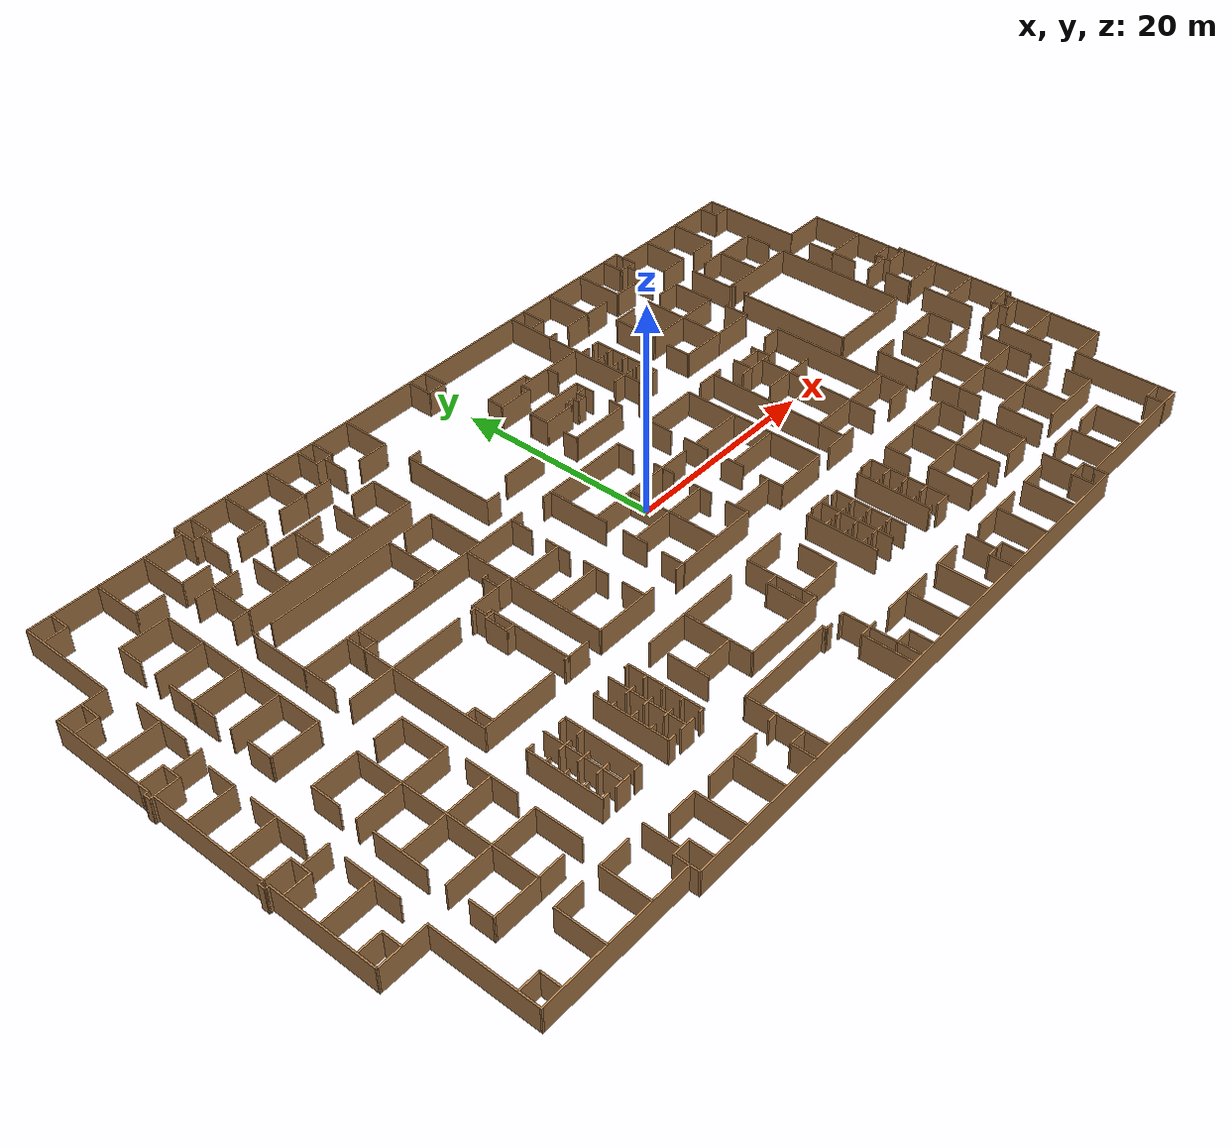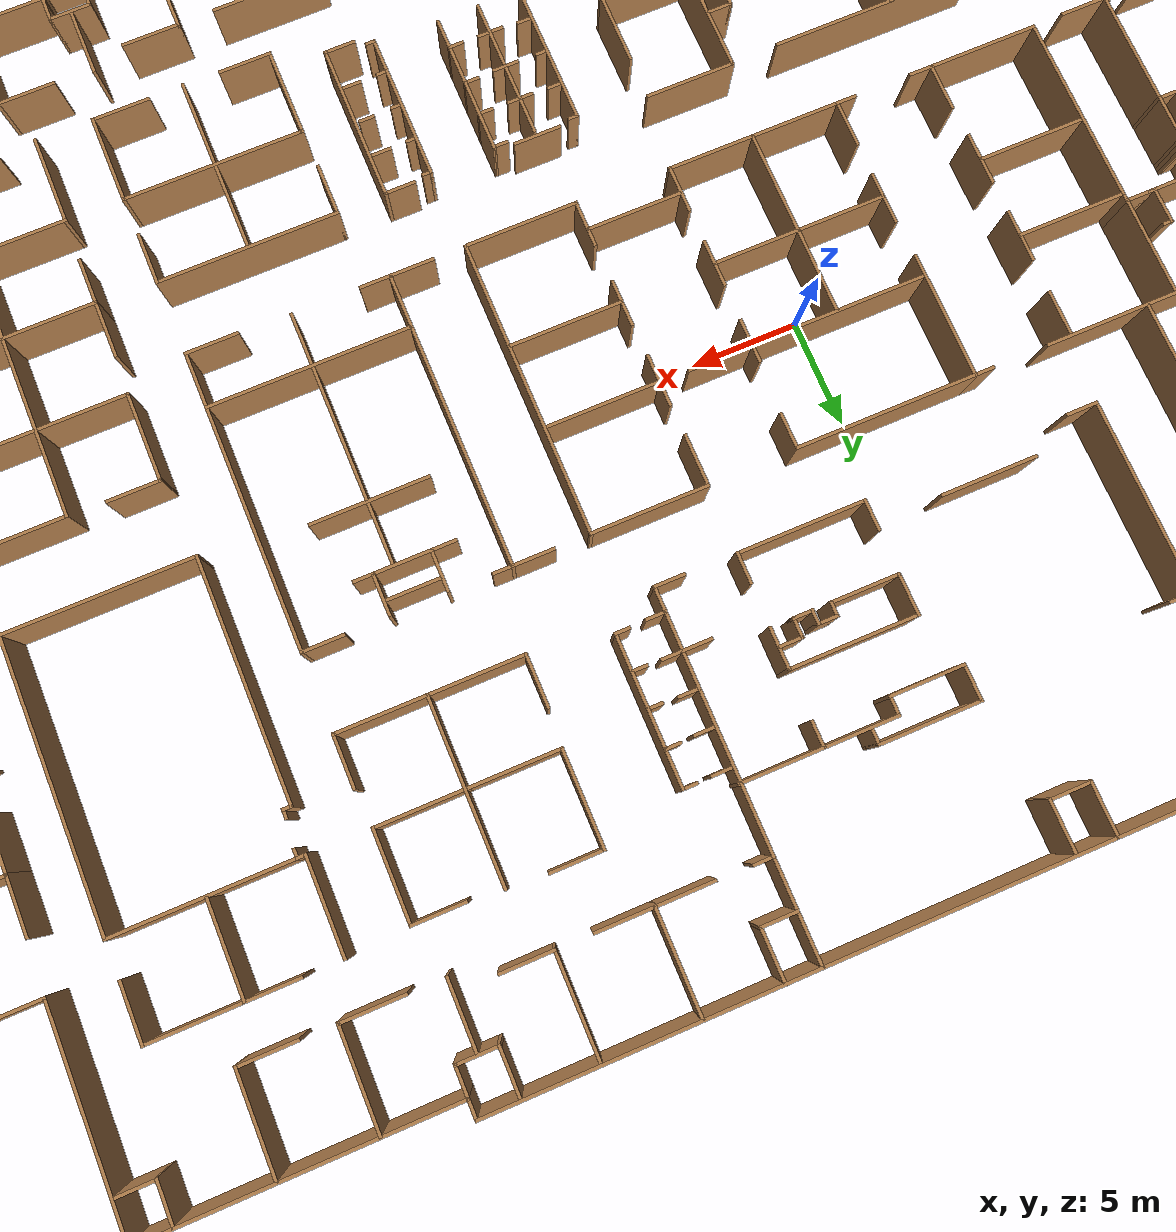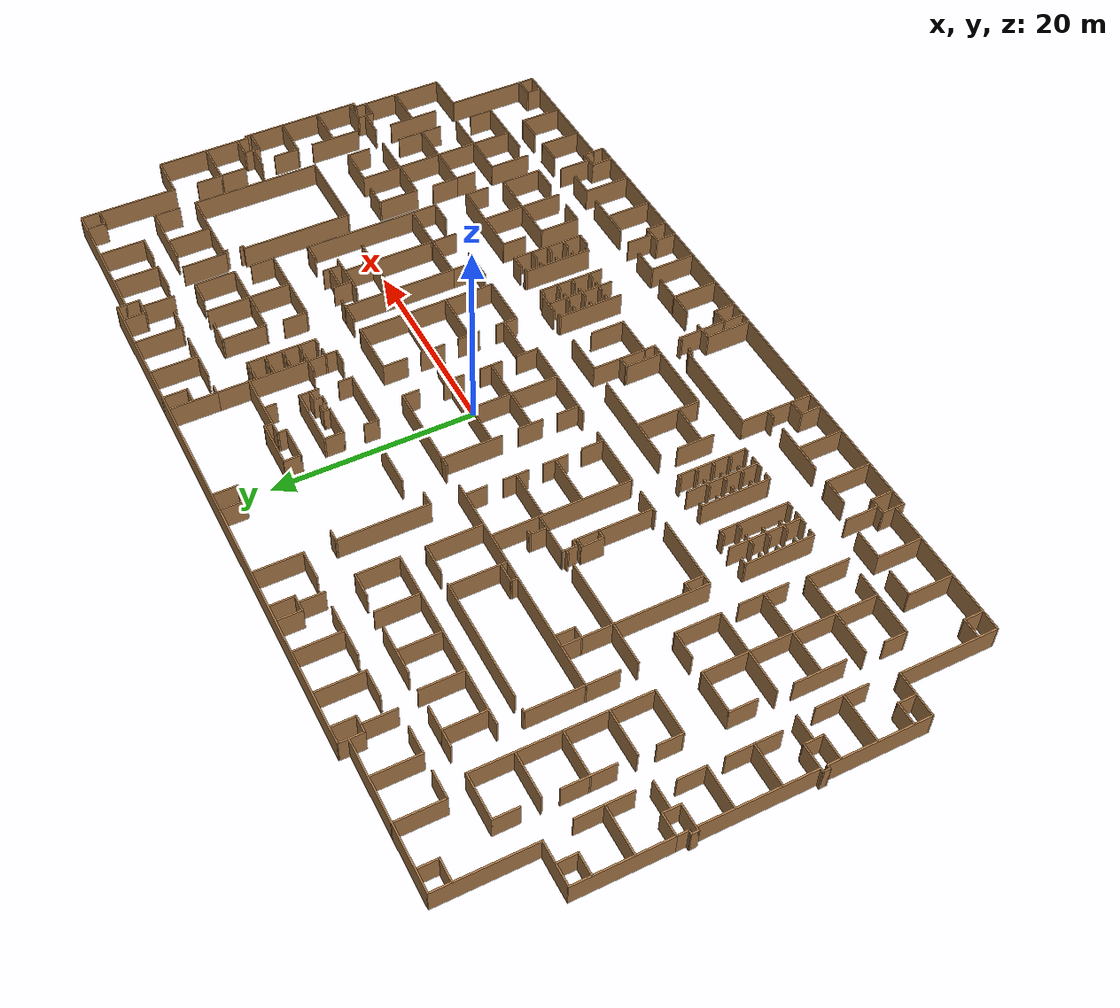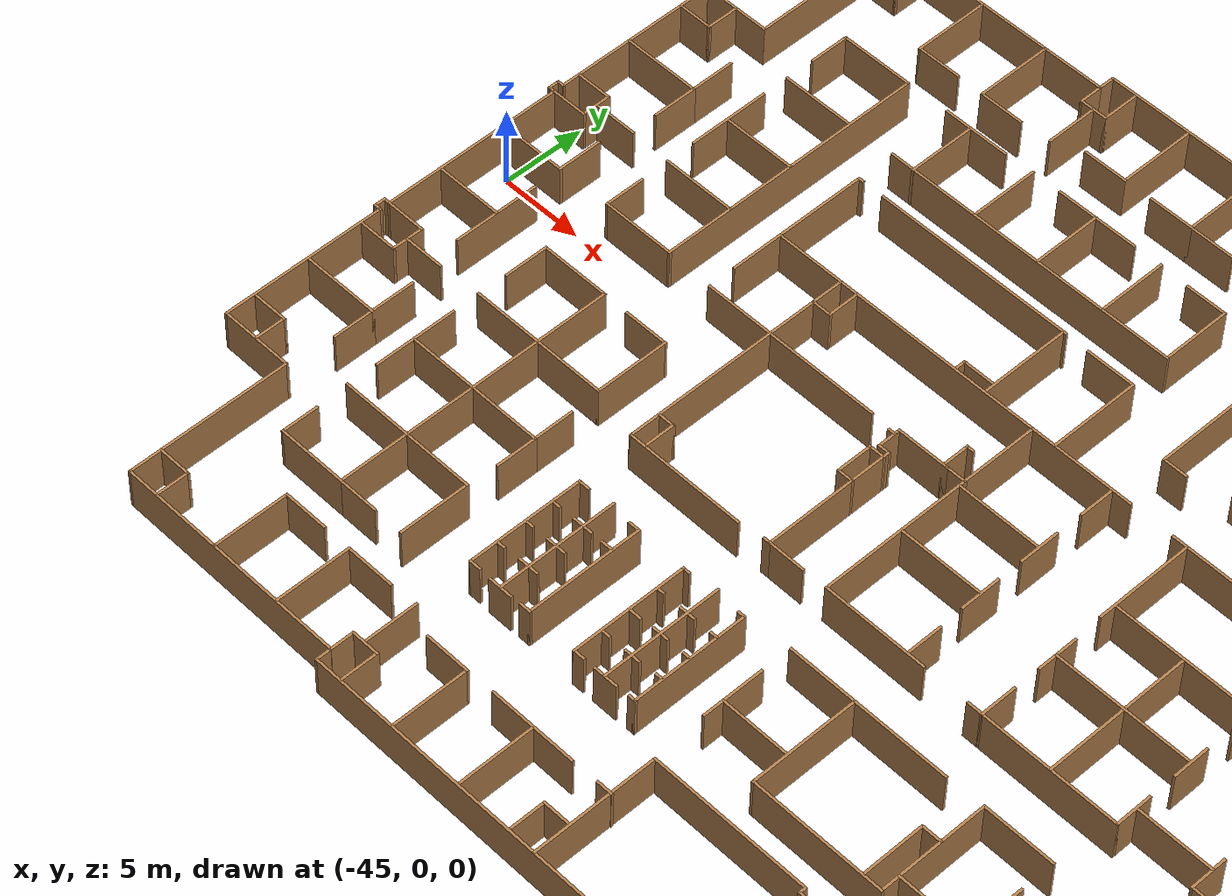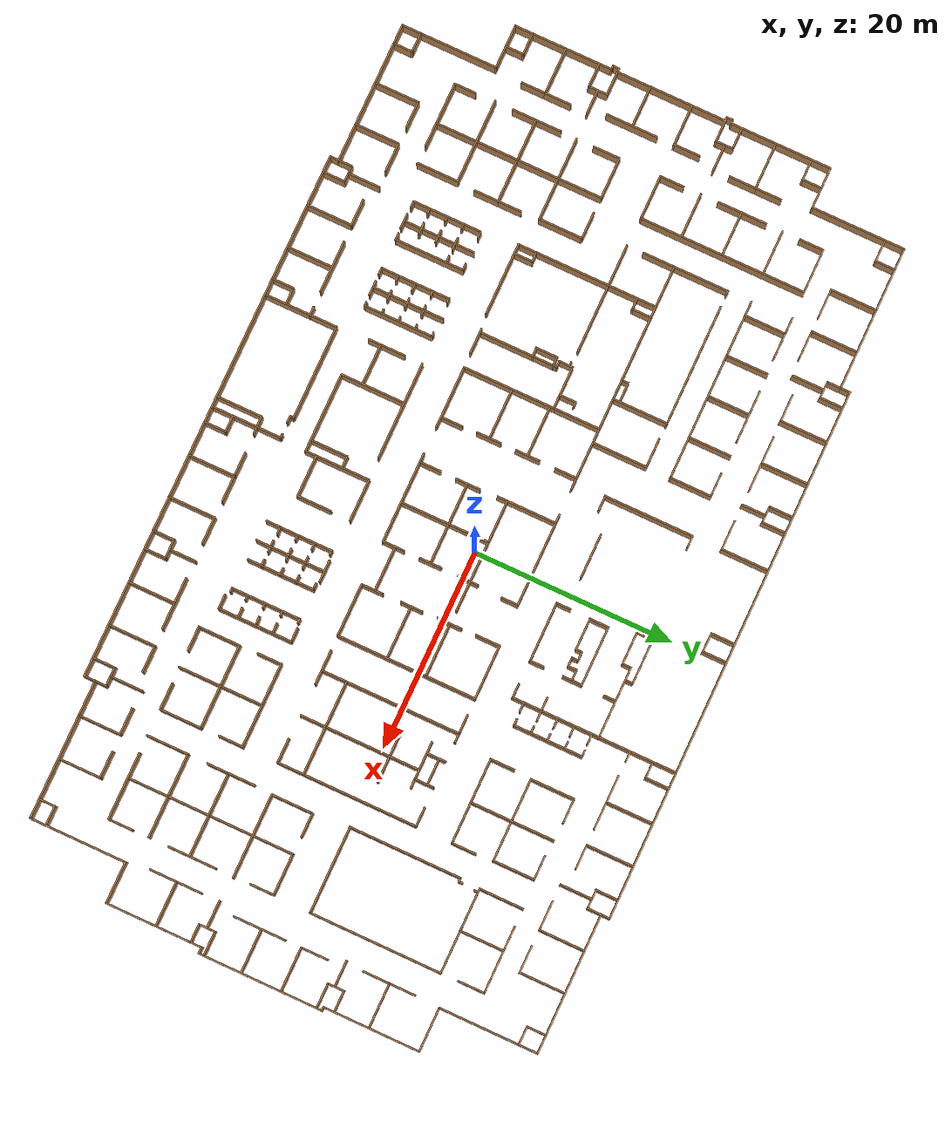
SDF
<?xml version='1.0'?>
<sdf version='1.6'>
  <model name='floor_plan'>
    <pose frame=''>-1.19231 -1.13475 0 0 -0 0</pose>
    <link name='Wall_10'>
      <collision name='Wall_10_Collision'>
        <geometry>
          <box>
            <size>10 0.15 2.5</size>
          </box>
        </geometry>
        <pose frame=''>0 0 1.25 0 -0 0</pose>
      </collision>
      <visual name='Wall_10_Visual'>
        <pose frame=''>0 0 1.25 0 -0 0</pose>
        <geometry>
          <box>
            <size>10 0.15 2.5</size>
          </box>
        </geometry>
        <material>
          <script>
            <uri>file://media/materials/scripts/gazebo.material</uri>
            <name>Gazebo/Wood</name>
          </script>
          <ambient>1 1 1 1</ambient>
        </material>
      </visual>
      <pose frame=''>40.65 20.6964 0 0 0 -1.5708</pose>
    </link>
    <link name='Wall_100'>
      <collision name='Wall_100_Collision'>
        <geometry>
          <box>
            <size>2.25 0.15 2.5</size>
          </box>
        </geometry>
        <pose frame=''>0 0 1.25 0 -0 0</pose>
      </collision>
      <visual name='Wall_100_Visual'>
        <pose frame=''>0 0 1.25 0 -0 0</pose>
        <geometry>
          <box>
            <size>2.25 0.15 2.5</size>
          </box>
        </geometry>
        <material>
          <script>
            <uri>file://media/materials/scripts/gazebo.material</uri>
            <name>Gazebo/Wood</name>
          </script>
          <ambient>1 1 1 1</ambient>
        </material>
      </visual>
      <pose frame=''>24.95 25.3214 0 0 -0 1.5708</pose>
    </link>
    <link name='Wall_102'>
      <collision name='Wall_102_Collision'>
        <geometry>
          <box>
            <size>3.25 0.15 2.5</size>
          </box>
        </geometry>
        <pose frame=''>0 0 1.25 0 -0 0</pose>
      </collision>
      <visual name='Wall_102_Visual'>
        <pose frame=''>0 0 1.25 0 -0 0</pose>
        <geometry>
          <box>
            <size>3.25 0.15 2.5</size>
          </box>
        </geometry>
        <material>
          <script>
            <uri>file://media/materials/scripts/gazebo.material</uri>
            <name>Gazebo/Wood</name>
          </script>
          <ambient>1 1 1 1</ambient>
        </material>
      </visual>
      <pose frame=''>25.8652 22.6731 0 0 0 -1.5708</pose>
    </link>
    <link name='Wall_104'>
      <collision name='Wall_104_Collision'>
        <geometry>
          <box>
            <size>3 0.15 2.5</size>
          </box>
        </geometry>
        <pose frame=''>0 0 1.25 0 -0 0</pose>
      </collision>
      <visual name='Wall_104_Visual'>
        <pose frame=''>0 0 1.25 0 -0 0</pose>
        <geometry>
          <box>
            <size>3 0.15 2.5</size>
          </box>
        </geometry>
        <material>
          <script>
            <uri>file://media/materials/scripts/gazebo.material</uri>
            <name>Gazebo/Wood</name>
          </script>
          <ambient>1 1 1 1</ambient>
        </material>
      </visual>
      <pose frame=''>28.998 21.0922 0 0 -0 0</pose>
    </link>
    <link name='Wall_105'>
      <collision name='Wall_105_Collision'>
        <geometry>
          <box>
            <size>4.65 0.15 2.5</size>
          </box>
        </geometry>
        <pose frame=''>0 0 1.25 0 -0 0</pose>
      </collision>
      <visual name='Wall_105_Visual'>
        <pose frame=''>0 0 1.25 0 -0 0</pose>
        <geometry>
          <box>
            <size>4.65 0.15 2.5</size>
          </box>
        </geometry>
        <material>
          <script>
            <uri>file://media/materials/scripts/gazebo.material</uri>
            <name>Gazebo/Wood</name>
          </script>
          <ambient>1 1 1 1</ambient>
        </material>
      </visual>
      <pose frame=''>30.423 23.3422 0 0 -0 1.5708</pose>
    </link>
    <link name='Wall_107'>
      <collision name='Wall_107_Collision'>
        <geometry>
          <box>
            <size>2.75 0.15 2.5</size>
          </box>
        </geometry>
        <pose frame=''>0 0 1.25 0 -0 0</pose>
      </collision>
      <visual name='Wall_107_Visual'>
        <pose frame=''>0 0 1.25 0 -0 0</pose>
        <geometry>
          <box>
            <size>2.75 0.15 2.5</size>
          </box>
        </geometry>
        <material>
          <script>
            <uri>file://media/materials/scripts/gazebo.material</uri>
            <name>Gazebo/Wood</name>
          </script>
          <ambient>1 1 1 1</ambient>
        </material>
      </visual>
      <pose frame=''>33.3717 21.0672 0 0 -0 0</pose>
    </link>
    <link name='Wall_108'>
      <collision name='Wall_108_Collision'>
        <geometry>
          <box>
            <size>4.65 0.15 2.5</size>
          </box>
        </geometry>
        <pose frame=''>0 0 1.25 0 -0 0</pose>
      </collision>
      <visual name='Wall_108_Visual'>
        <pose frame=''>0 0 1.25 0 -0 0</pose>
        <geometry>
          <box>
            <size>4.65 0.15 2.5</size>
          </box>
        </geometry>
        <material>
          <script>
            <uri>file://media/materials/scripts/gazebo.material</uri>
            <name>Gazebo/Wood</name>
          </script>
          <ambient>1 1 1 1</ambient>
        </material>
      </visual>
      <pose frame=''>34.6717 23.3172 0 0 -0 1.5708</pose>
    </link>
    <link name='Wall_11'>
      <collision name='Wall_11_Collision'>
        <geometry>
          <box>
            <size>4.5 0.15 2.5</size>
          </box>
        </geometry>
        <pose frame=''>0 0 1.25 0 -0 0</pose>
      </collision>
      <visual name='Wall_11_Visual'>
        <pose frame=''>0 0 1.25 0 -0 0</pose>
        <geometry>
          <box>
            <size>4.5 0.15 2.5</size>
          </box>
        </geometry>
        <material>
          <script>
            <uri>file://media/materials/scripts/gazebo.material</uri>
            <name>Gazebo/Wood</name>
          </script>
          <ambient>1 1 1 1</ambient>
        </material>
      </visual>
      <pose frame=''>42.825 15.7714 0 0 -0 0</pose>
    </link>
    <link name='Wall_110'>
      <collision name='Wall_110_Collision'>
        <geometry>
          <box>
            <size>2 0.15 2.5</size>
          </box>
        </geometry>
        <pose frame=''>0 0 1.25 0 -0 0</pose>
      </collision>
      <visual name='Wall_110_Visual'>
        <pose frame=''>0 0 1.25 0 -0 0</pose>
        <geometry>
          <box>
            <size>2 0.15 2.5</size>
          </box>
        </geometry>
        <material>
          <script>
            <uri>file://media/materials/scripts/gazebo.material</uri>
            <name>Gazebo/Wood</name>
          </script>
          <ambient>1 1 1 1</ambient>
        </material>
      </visual>
      <pose frame=''>38.8412 24.6589 0 0 0 -1.5708</pose>
    </link>
    <link name='Wall_111'>
      <collision name='Wall_111_Collision'>
        <geometry>
          <box>
            <size>1.9 0.15 2.5</size>
          </box>
        </geometry>
        <pose frame=''>0 0 1.25 0 -0 0</pose>
      </collision>
      <visual name='Wall_111_Visual'>
        <pose frame=''>0 0 1.25 0 -0 0</pose>
        <geometry>
          <box>
            <size>1.9 0.15 2.5</size>
          </box>
        </geometry>
        <material>
          <script>
            <uri>file://media/materials/scripts/gazebo.material</uri>
            <name>Gazebo/Wood</name>
          </script>
          <ambient>1 1 1 1</ambient>
        </material>
      </visual>
      <pose frame=''>39.7162 23.7339 0 0 -0 0</pose>
    </link>
    <link name='Wall_113'>
      <collision name='Wall_113_Collision'>
        <geometry>
          <box>
            <size>12 0.15 2.5</size>
          </box>
        </geometry>
        <pose frame=''>0 0 1.25 0 -0 0</pose>
      </collision>
      <visual name='Wall_113_Visual'>
        <pose frame=''>0 0 1.25 0 -0 0</pose>
        <geometry>
          <box>
            <size>12 0.15 2.5</size>
          </box>
        </geometry>
        <material>
          <script>
            <uri>file://media/materials/scripts/gazebo.material</uri>
            <name>Gazebo/Wood</name>
          </script>
          <ambient>1 1 1 1</ambient>
        </material>
      </visual>
      <pose frame=''>12.1534 15.9139 0 0 0 -1.5708</pose>
    </link>
    <link name='Wall_114'>
      <collision name='Wall_114_Collision'>
        <geometry>
          <box>
            <size>1.5 0.15 2.5</size>
          </box>
        </geometry>
        <pose frame=''>0 0 1.25 0 -0 0</pose>
      </collision>
      <visual name='Wall_114_Visual'>
        <pose frame=''>0 0 1.25 0 -0 0</pose>
        <geometry>
          <box>
            <size>1.5 0.15 2.5</size>
          </box>
        </geometry>
        <material>
          <script>
            <uri>file://media/materials/scripts/gazebo.material</uri>
            <name>Gazebo/Wood</name>
          </script>
          <ambient>1 1 1 1</ambient>
        </material>
      </visual>
      <pose frame=''>11.4784 9.98893 0 0 -0 3.14159</pose>
    </link>
    <link name='Wall_12'>
      <collision name='Wall_12_Collision'>
        <geometry>
          <box>
            <size>9.75 0.15 2.5</size>
          </box>
        </geometry>
        <pose frame=''>0 0 1.25 0 -0 0</pose>
      </collision>
      <visual name='Wall_12_Visual'>
        <pose frame=''>0 0 1.25 0 -0 0</pose>
        <geometry>
          <box>
            <size>9.75 0.15 2.5</size>
          </box>
        </geometry>
        <material>
          <script>
            <uri>file://media/materials/scripts/gazebo.material</uri>
            <name>Gazebo/Wood</name>
          </script>
          <ambient>1 1 1 1</ambient>
        </material>
      </visual>
      <pose frame=''>45 10.9714 0 0 0 -1.5708</pose>
    </link>
    <link name='Wall_120'>
      <collision name='Wall_120_Collision'>
        <geometry>
          <box>
            <size>1 0.15 2.5</size>
          </box>
        </geometry>
        <pose frame=''>0 0 1.25 0 -0 0</pose>
      </collision>
      <visual name='Wall_120_Visual'>
        <pose frame=''>0 0 1.25 0 -0 0</pose>
        <geometry>
          <box>
            <size>1 0.15 2.5</size>
          </box>
        </geometry>
        <material>
          <script>
            <uri>file://media/materials/scripts/gazebo.material</uri>
            <name>Gazebo/Wood</name>
          </script>
          <ambient>1 1 1 1</ambient>
        </material>
      </visual>
      <pose frame=''>12.6925 17.9951 0 0 -0 3.14159</pose>
    </link>
    <link name='Wall_124'>
      <collision name='Wall_124_Collision'>
        <geometry>
          <box>
            <size>1 0.15 2.5</size>
          </box>
        </geometry>
        <pose frame=''>0 0 1.25 0 -0 0</pose>
      </collision>
      <visual name='Wall_124_Visual'>
        <pose frame=''>0 0 1.25 0 -0 0</pose>
        <geometry>
          <box>
            <size>1 0.15 2.5</size>
          </box>
        </geometry>
        <material>
          <script>
            <uri>file://media/materials/scripts/gazebo.material</uri>
            <name>Gazebo/Wood</name>
          </script>
          <ambient>1 1 1 1</ambient>
        </material>
      </visual>
      <pose frame=''>12.669 16.2306 0 0 -0 3.14159</pose>
    </link>
    <link name='Wall_126'>
      <collision name='Wall_126_Collision'>
        <geometry>
          <box>
            <size>1 0.15 2.5</size>
          </box>
        </geometry>
        <pose frame=''>0 0 1.25 0 -0 0</pose>
      </collision>
      <visual name='Wall_126_Visual'>
        <pose frame=''>0 0 1.25 0 -0 0</pose>
        <geometry>
          <box>
            <size>1 0.15 2.5</size>
          </box>
        </geometry>
        <material>
          <script>
            <uri>file://media/materials/scripts/gazebo.material</uri>
            <name>Gazebo/Wood</name>
          </script>
          <ambient>1 1 1 1</ambient>
        </material>
      </visual>
      <pose frame=''>12.6219 14.5602 0 0 -0 3.14159</pose>
    </link>
    <link name='Wall_128'>
      <collision name='Wall_128_Collision'>
        <geometry>
          <box>
            <size>1 0.15 2.5</size>
          </box>
        </geometry>
        <pose frame=''>0 0 1.25 0 -0 0</pose>
      </collision>
      <visual name='Wall_128_Visual'>
        <pose frame=''>0 0 1.25 0 -0 0</pose>
        <geometry>
          <box>
            <size>1 0.15 2.5</size>
          </box>
        </geometry>
        <material>
          <script>
            <uri>file://media/materials/scripts/gazebo.material</uri>
            <name>Gazebo/Wood</name>
          </script>
          <ambient>1 1 1 1</ambient>
        </material>
      </visual>
      <pose frame=''>12.6454 12.8898 0 0 -0 3.14159</pose>
    </link>
    <link name='Wall_13'>
      <collision name='Wall_13_Collision'>
        <geometry>
          <box>
            <size>0.5 0.15 2.5</size>
          </box>
        </geometry>
        <pose frame=''>0 0 1.25 0 -0 0</pose>
      </collision>
      <visual name='Wall_13_Visual'>
        <pose frame=''>0 0 1.25 0 -0 0</pose>
        <geometry>
          <box>
            <size>0.5 0.15 2.5</size>
          </box>
        </geometry>
        <material>
          <script>
            <uri>file://media/materials/scripts/gazebo.material</uri>
            <name>Gazebo/Wood</name>
          </script>
          <ambient>1 1 1 1</ambient>
        </material>
      </visual>
      <pose frame=''>45.175 6.1714 0 0 -0 0</pose>
    </link>
    <link name='Wall_130'>
      <collision name='Wall_130_Collision'>
        <geometry>
          <box>
            <size>1 0.15 2.5</size>
          </box>
        </geometry>
        <pose frame=''>0 0 1.25 0 -0 0</pose>
      </collision>
      <visual name='Wall_130_Visual'>
        <pose frame=''>0 0 1.25 0 -0 0</pose>
        <geometry>
          <box>
            <size>1 0.15 2.5</size>
          </box>
        </geometry>
        <material>
          <script>
            <uri>file://media/materials/scripts/gazebo.material</uri>
            <name>Gazebo/Wood</name>
          </script>
          <ambient>1 1 1 1</ambient>
        </material>
      </visual>
      <pose frame=''>12.5749 11.1253 0 0 -0 3.14159</pose>
    </link>
    <link name='Wall_132'>
      <collision name='Wall_132_Collision'>
        <geometry>
          <box>
            <size>1.5 0.15 2.5</size>
          </box>
        </geometry>
        <pose frame=''>0 0 1.25 0 -0 0</pose>
      </collision>
      <visual name='Wall_132_Visual'>
        <pose frame=''>0 0 1.25 0 -0 0</pose>
        <geometry>
          <box>
            <size>1.5 0.15 2.5</size>
          </box>
        </geometry>
        <material>
          <script>
            <uri>file://media/materials/scripts/gazebo.material</uri>
            <name>Gazebo/Wood</name>
          </script>
          <ambient>1 1 1 1</ambient>
        </material>
      </visual>
      <pose frame=''>2.5583 10.705 0 0 0 -1.5708</pose>
    </link>
    <link name='Wall_133'>
      <collision name='Wall_133_Collision'>
        <geometry>
          <box>
            <size>6 0.15 2.5</size>
          </box>
        </geometry>
        <pose frame=''>0 0 1.25 0 -0 0</pose>
      </collision>
      <visual name='Wall_133_Visual'>
        <pose frame=''>0 0 1.25 0 -0 0</pose>
        <geometry>
          <box>
            <size>6 0.15 2.5</size>
          </box>
        </geometry>
        <material>
          <script>
            <uri>file://media/materials/scripts/gazebo.material</uri>
            <name>Gazebo/Wood</name>
          </script>
          <ambient>1 1 1 1</ambient>
        </material>
      </visual>
      <pose frame=''>5.4833 10.03 0 0 -0 0</pose>
    </link>
    <link name='Wall_134'>
      <collision name='Wall_134_Collision'>
        <geometry>
          <box>
            <size>1.5 0.15 2.5</size>
          </box>
        </geometry>
        <pose frame=''>0 0 1.25 0 -0 0</pose>
      </collision>
      <visual name='Wall_134_Visual'>
        <pose frame=''>0 0 1.25 0 -0 0</pose>
        <geometry>
          <box>
            <size>1.5 0.15 2.5</size>
          </box>
        </geometry>
        <material>
          <script>
            <uri>file://media/materials/scripts/gazebo.material</uri>
            <name>Gazebo/Wood</name>
          </script>
          <ambient>1 1 1 1</ambient>
        </material>
      </visual>
      <pose frame=''>8.4083 10.705 0 0 -0 1.5708</pose>
    </link>
    <link name='Wall_136'>
      <collision name='Wall_136_Collision'>
        <geometry>
          <box>
            <size>4.5 0.15 2.5</size>
          </box>
        </geometry>
        <pose frame=''>0 0 1.25 0 -0 0</pose>
      </collision>
      <visual name='Wall_136_Visual'>
        <pose frame=''>0 0 1.25 0 -0 0</pose>
        <geometry>
          <box>
            <size>4.5 0.15 2.5</size>
          </box>
        </geometry>
        <material>
          <script>
            <uri>file://media/materials/scripts/gazebo.material</uri>
            <name>Gazebo/Wood</name>
          </script>
          <ambient>1 1 1 1</ambient>
        </material>
      </visual>
      <pose frame=''>-2.72059 11.0775 0 0 -0 0</pose>
    </link>
    <link name='Wall_138'>
      <collision name='Wall_138_Collision'>
        <geometry>
          <box>
            <size>1.25 0.15 2.5</size>
          </box>
        </geometry>
        <pose frame=''>0 0 1.25 0 -0 0</pose>
      </collision>
      <visual name='Wall_138_Visual'>
        <pose frame=''>0 0 1.25 0 -0 0</pose>
        <geometry>
          <box>
            <size>1.25 0.15 2.5</size>
          </box>
        </geometry>
        <material>
          <script>
            <uri>file://media/materials/scripts/gazebo.material</uri>
            <name>Gazebo/Wood</name>
          </script>
          <ambient>1 1 1 1</ambient>
        </material>
      </visual>
      <pose frame=''>-7.75979 18.8072 0 0 -0 3.14159</pose>
    </link>
    <link name='Wall_139'>
      <collision name='Wall_139_Collision'>
        <geometry>
          <box>
            <size>9 0.15 2.5</size>
          </box>
        </geometry>
        <pose frame=''>0 0 1.25 0 -0 0</pose>
      </collision>
      <visual name='Wall_139_Visual'>
        <pose frame=''>0 0 1.25 0 -0 0</pose>
        <geometry>
          <box>
            <size>9 0.15 2.5</size>
          </box>
        </geometry>
        <material>
          <script>
            <uri>file://media/materials/scripts/gazebo.material</uri>
            <name>Gazebo/Wood</name>
          </script>
          <ambient>1 1 1 1</ambient>
        </material>
      </visual>
      <pose frame=''>-8.30979 14.3822 0 0 0 -1.5708</pose>
    </link>
    <link name='Wall_14'>
      <collision name='Wall_14_Collision'>
        <geometry>
          <box>
            <size>12.5 0.15 2.5</size>
          </box>
        </geometry>
        <pose frame=''>0 0 1.25 0 -0 0</pose>
      </collision>
      <visual name='Wall_14_Visual'>
        <pose frame=''>0 0 1.25 0 -0 0</pose>
        <geometry>
          <box>
            <size>12.5 0.15 2.5</size>
          </box>
        </geometry>
        <material>
          <script>
            <uri>file://media/materials/scripts/gazebo.material</uri>
            <name>Gazebo/Wood</name>
          </script>
          <ambient>1 1 1 1</ambient>
        </material>
      </visual>
      <pose frame=''>45.35 -0.003604 0 0 0 -1.5708</pose>
    </link>
    <link name='Wall_140'>
      <collision name='Wall_140_Collision'>
        <geometry>
          <box>
            <size>1.5 0.15 2.5</size>
          </box>
        </geometry>
        <pose frame=''>0 0 1.25 0 -0 0</pose>
      </collision>
      <visual name='Wall_140_Visual'>
        <pose frame=''>0 0 1.25 0 -0 0</pose>
        <geometry>
          <box>
            <size>1.5 0.15 2.5</size>
          </box>
        </geometry>
        <material>
          <script>
            <uri>file://media/materials/scripts/gazebo.material</uri>
            <name>Gazebo/Wood</name>
          </script>
          <ambient>1 1 1 1</ambient>
        </material>
      </visual>
      <pose frame=''>-7.63479 9.95716 0 0 -0 0</pose>
    </link>
    <link name='Wall_142'>
      <collision name='Wall_142_Collision'>
        <geometry>
          <box>
            <size>0.75 0.15 2.5</size>
          </box>
        </geometry>
        <pose frame=''>0 0 1.25 0 -0 0</pose>
      </collision>
      <visual name='Wall_142_Visual'>
        <pose frame=''>0 0 1.25 0 -0 0</pose>
        <geometry>
          <box>
            <size>0.75 0.15 2.5</size>
          </box>
        </geometry>
        <material>
          <script>
            <uri>file://media/materials/scripts/gazebo.material</uri>
            <name>Gazebo/Wood</name>
          </script>
          <ambient>1 1 1 1</ambient>
        </material>
      </visual>
      <pose frame=''>14.1127 18.0225 0 0 -0 0</pose>
    </link>
    <link name='Wall_143'>
      <collision name='Wall_143_Collision'>
        <geometry>
          <box>
            <size>7 0.15 2.5</size>
          </box>
        </geometry>
        <pose frame=''>0 0 1.25 0 -0 0</pose>
      </collision>
      <visual name='Wall_143_Visual'>
        <pose frame=''>0 0 1.25 0 -0 0</pose>
        <geometry>
          <box>
            <size>7 0.15 2.5</size>
          </box>
        </geometry>
        <material>
          <script>
            <uri>file://media/materials/scripts/gazebo.material</uri>
            <name>Gazebo/Wood</name>
          </script>
          <ambient>1 1 1 1</ambient>
        </material>
      </visual>
      <pose frame=''>14.4127 14.5975 0 0 0 -1.5708</pose>
    </link>
    <link name='Wall_144'>
      <collision name='Wall_144_Collision'>
        <geometry>
          <box>
            <size>0.75 0.15 2.5</size>
          </box>
        </geometry>
        <pose frame=''>0 0 1.25 0 -0 0</pose>
      </collision>
      <visual name='Wall_144_Visual'>
        <pose frame=''>0 0 1.25 0 -0 0</pose>
        <geometry>
          <box>
            <size>0.75 0.15 2.5</size>
          </box>
        </geometry>
        <material>
          <script>
            <uri>file://media/materials/scripts/gazebo.material</uri>
            <name>Gazebo/Wood</name>
          </script>
          <ambient>1 1 1 1</ambient>
        </material>
      </visual>
      <pose frame=''>14.1127 11.1725 0 0 -0 3.14159</pose>
    </link>
    <link name='Wall_148'>
      <collision name='Wall_148_Collision'>
        <geometry>
          <box>
            <size>0.75 0.15 2.5</size>
          </box>
        </geometry>
        <pose frame=''>0 0 1.25 0 -0 0</pose>
      </collision>
      <visual name='Wall_148_Visual'>
        <pose frame=''>0 0 1.25 0 -0 0</pose>
        <geometry>
          <box>
            <size>0.75 0.15 2.5</size>
          </box>
        </geometry>
        <material>
          <script>
            <uri>file://media/materials/scripts/gazebo.material</uri>
            <name>Gazebo/Wood</name>
          </script>
          <ambient>1 1 1 1</ambient>
        </material>
      </visual>
      <pose frame=''>14.0607 16.2859 0 0 -0 3.14159</pose>
    </link>
    <link name='Wall_15'>
      <collision name='Wall_15_Collision'>
        <geometry>
          <box>
            <size>0.75 0.15 2.5</size>
          </box>
        </geometry>
        <pose frame=''>0 0 1.25 0 -0 0</pose>
      </collision>
      <visual name='Wall_15_Visual'>
        <pose frame=''>0 0 1.25 0 -0 0</pose>
        <geometry>
          <box>
            <size>0.75 0.15 2.5</size>
          </box>
        </geometry>
        <material>
          <script>
            <uri>file://media/materials/scripts/gazebo.material</uri>
            <name>Gazebo/Wood</name>
          </script>
          <ambient>1 1 1 1</ambient>
        </material>
      </visual>
      <pose frame=''>45.05 -6.1786 0 0 -0 3.14159</pose>
    </link>
    <link name='Wall_150'>
      <collision name='Wall_150_Collision'>
        <geometry>
          <box>
            <size>0.75 0.15 2.5</size>
          </box>
        </geometry>
        <pose frame=''>0 0 1.25 0 -0 0</pose>
      </collision>
      <visual name='Wall_150_Visual'>
        <pose frame=''>0 0 1.25 0 -0 0</pose>
        <geometry>
          <box>
            <size>0.75 0.15 2.5</size>
          </box>
        </geometry>
        <material>
          <script>
            <uri>file://media/materials/scripts/gazebo.material</uri>
            <name>Gazebo/Wood</name>
          </script>
          <ambient>1 1 1 1</ambient>
        </material>
      </visual>
      <pose frame=''>14.1016 14.5265 0 0 -0 3.14159</pose>
    </link>
    <link name='Wall_152'>
      <collision name='Wall_152_Collision'>
        <geometry>
          <box>
            <size>0.75 0.15 2.5</size>
          </box>
        </geometry>
        <pose frame=''>0 0 1.25 0 -0 0</pose>
      </collision>
      <visual name='Wall_152_Visual'>
        <pose frame=''>0 0 1.25 0 -0 0</pose>
        <geometry>
          <box>
            <size>0.75 0.15 2.5</size>
          </box>
        </geometry>
        <material>
          <script>
            <uri>file://media/materials/scripts/gazebo.material</uri>
            <name>Gazebo/Wood</name>
          </script>
          <ambient>1 1 1 1</ambient>
        </material>
      </visual>
      <pose frame=''>14.0607 12.8694 0 0 -0 3.14159</pose>
    </link>
    <link name='Wall_16'>
      <collision name='Wall_16_Collision'>
        <geometry>
          <box>
            <size>9.75 0.15 2.5</size>
          </box>
        </geometry>
        <pose frame=''>0 0 1.25 0 -0 0</pose>
      </collision>
      <visual name='Wall_16_Visual'>
        <pose frame=''>0 0 1.25 0 -0 0</pose>
        <geometry>
          <box>
            <size>9.75 0.15 2.5</size>
          </box>
        </geometry>
        <material>
          <script>
            <uri>file://media/materials/scripts/gazebo.material</uri>
            <name>Gazebo/Wood</name>
          </script>
          <ambient>1 1 1 1</ambient>
        </material>
      </visual>
      <pose frame=''>44.75 -10.9786 0 0 0 -1.5708</pose>
    </link>
    <link name='Wall_17'>
      <collision name='Wall_17_Collision'>
        <geometry>
          <box>
            <size>4.25 0.15 2.5</size>
          </box>
        </geometry>
        <pose frame=''>0 0 1.25 0 -0 0</pose>
      </collision>
      <visual name='Wall_17_Visual'>
        <pose frame=''>0 0 1.25 0 -0 0</pose>
        <geometry>
          <box>
            <size>4.25 0.15 2.5</size>
          </box>
        </geometry>
        <material>
          <script>
            <uri>file://media/materials/scripts/gazebo.material</uri>
            <name>Gazebo/Wood</name>
          </script>
          <ambient>1 1 1 1</ambient>
        </material>
      </visual>
      <pose frame=''>42.7 -15.7786 0 0 -0 3.14159</pose>
    </link>
    <link name='Wall_171'>
      <collision name='Wall_171_Collision'>
        <geometry>
          <box>
            <size>8.5 0.15 2.5</size>
          </box>
        </geometry>
        <pose frame=''>0 0 1.25 0 -0 0</pose>
      </collision>
      <visual name='Wall_171_Visual'>
        <pose frame=''>0 0 1.25 0 -0 0</pose>
        <geometry>
          <box>
            <size>8.5 0.15 2.5</size>
          </box>
        </geometry>
        <material>
          <script>
            <uri>file://media/materials/scripts/gazebo.material</uri>
            <name>Gazebo/Wood</name>
          </script>
          <ambient>1 1 1 1</ambient>
        </material>
      </visual>
      <pose frame=''>22.4756 14.7101 0 0 0 -1.5708</pose>
    </link>
    <link name='Wall_172'>
      <collision name='Wall_172_Collision'>
        <geometry>
          <box>
            <size>4.5 0.15 2.5</size>
          </box>
        </geometry>
        <pose frame=''>0 0 1.25 0 -0 0</pose>
      </collision>
      <visual name='Wall_172_Visual'>
        <pose frame=''>0 0 1.25 0 -0 0</pose>
        <geometry>
          <box>
            <size>4.5 0.15 2.5</size>
          </box>
        </geometry>
        <material>
          <script>
            <uri>file://media/materials/scripts/gazebo.material</uri>
            <name>Gazebo/Wood</name>
          </script>
          <ambient>1 1 1 1</ambient>
        </material>
      </visual>
      <pose frame=''>20.3006 10.5351 0 0 -0 3.14159</pose>
    </link>
    <link name='Wall_173'>
      <collision name='Wall_173_Collision'>
        <geometry>
          <box>
            <size>2.5 0.15 2.5</size>
          </box>
        </geometry>
        <pose frame=''>0 0 1.25 0 -0 0</pose>
      </collision>
      <visual name='Wall_173_Visual'>
        <pose frame=''>0 0 1.25 0 -0 0</pose>
        <geometry>
          <box>
            <size>2.5 0.15 2.5</size>
          </box>
        </geometry>
        <material>
          <script>
            <uri>file://media/materials/scripts/gazebo.material</uri>
            <name>Gazebo/Wood</name>
          </script>
          <ambient>1 1 1 1</ambient>
        </material>
      </visual>
      <pose frame=''>18.1256 11.7101 0 0 -0 1.5708</pose>
    </link>
    <link name='Wall_175'>
      <collision name='Wall_175_Collision'>
        <geometry>
          <box>
            <size>4.25 0.15 2.5</size>
          </box>
        </geometry>
        <pose frame=''>0 0 1.25 0 -0 0</pose>
      </collision>
      <visual name='Wall_175_Visual'>
        <pose frame=''>0 0 1.25 0 -0 0</pose>
        <geometry>
          <box>
            <size>4.25 0.15 2.5</size>
          </box>
        </geometry>
        <material>
          <script>
            <uri>file://media/materials/scripts/gazebo.material</uri>
            <name>Gazebo/Wood</name>
          </script>
          <ambient>1 1 1 1</ambient>
        </material>
      </visual>
      <pose frame=''>20.3031 14.6405 0 0 -0 3.14159</pose>
    </link>
    <link name='Wall_176'>
      <collision name='Wall_176_Collision'>
        <geometry>
          <box>
            <size>4.5 0.15 2.5</size>
          </box>
        </geometry>
        <pose frame=''>0 0 1.25 0 -0 0</pose>
      </collision>
      <visual name='Wall_176_Visual'>
        <pose frame=''>0 0 1.25 0 -0 0</pose>
        <geometry>
          <box>
            <size>4.5 0.15 2.5</size>
          </box>
        </geometry>
        <material>
          <script>
            <uri>file://media/materials/scripts/gazebo.material</uri>
            <name>Gazebo/Wood</name>
          </script>
          <ambient>1 1 1 1</ambient>
        </material>
      </visual>
      <pose frame=''>18.2532 16.8155 0 0 -0 1.5708</pose>
    </link>
    <link name='Wall_178'>
      <collision name='Wall_178_Collision'>
        <geometry>
          <box>
            <size>4.25 0.15 2.5</size>
          </box>
        </geometry>
        <pose frame=''>0 0 1.25 0 -0 0</pose>
      </collision>
      <visual name='Wall_178_Visual'>
        <pose frame=''>0 0 1.25 0 -0 0</pose>
        <geometry>
          <box>
            <size>4.25 0.15 2.5</size>
          </box>
        </geometry>
        <material>
          <script>
            <uri>file://media/materials/scripts/gazebo.material</uri>
            <name>Gazebo/Wood</name>
          </script>
          <ambient>1 1 1 1</ambient>
        </material>
      </visual>
      <pose frame=''>24.5256 10.5351 0 0 -0 0</pose>
    </link>
    <link name='Wall_179'>
      <collision name='Wall_179_Collision'>
        <geometry>
          <box>
            <size>2.5 0.15 2.5</size>
          </box>
        </geometry>
        <pose frame=''>0 0 1.25 0 -0 0</pose>
      </collision>
      <visual name='Wall_179_Visual'>
        <pose frame=''>0 0 1.25 0 -0 0</pose>
        <geometry>
          <box>
            <size>2.5 0.15 2.5</size>
          </box>
        </geometry>
        <material>
          <script>
            <uri>file://media/materials/scripts/gazebo.material</uri>
            <name>Gazebo/Wood</name>
          </script>
          <ambient>1 1 1 1</ambient>
        </material>
      </visual>
      <pose frame=''>26.5756 11.7101 0 0 -0 1.5708</pose>
    </link>
    <link name='Wall_18'>
      <collision name='Wall_18_Collision'>
        <geometry>
          <box>
            <size>9.75 0.15 2.5</size>
          </box>
        </geometry>
        <pose frame=''>0 0 1.25 0 -0 0</pose>
      </collision>
      <visual name='Wall_18_Visual'>
        <pose frame=''>0 0 1.25 0 -0 0</pose>
        <geometry>
          <box>
            <size>9.75 0.15 2.5</size>
          </box>
        </geometry>
        <material>
          <script>
            <uri>file://media/materials/scripts/gazebo.material</uri>
            <name>Gazebo/Wood</name>
          </script>
          <ambient>1 1 1 1</ambient>
        </material>
      </visual>
      <pose frame=''>40.65 -20.5786 0 0 0 -1.5708</pose>
    </link>
    <link name='Wall_181'>
      <collision name='Wall_181_Collision'>
        <geometry>
          <box>
            <size>4.25 0.15 2.5</size>
          </box>
        </geometry>
        <pose frame=''>0 0 1.25 0 -0 0</pose>
      </collision>
      <visual name='Wall_181_Visual'>
        <pose frame=''>0 0 1.25 0 -0 0</pose>
        <geometry>
          <box>
            <size>4.25 0.15 2.5</size>
          </box>
        </geometry>
        <material>
          <script>
            <uri>file://media/materials/scripts/gazebo.material</uri>
            <name>Gazebo/Wood</name>
          </script>
          <ambient>1 1 1 1</ambient>
        </material>
      </visual>
      <pose frame=''>24.4032 14.6405 0 0 -0 0</pose>
    </link>
    <link name='Wall_182'>
      <collision name='Wall_182_Collision'>
        <geometry>
          <box>
            <size>4.25 0.15 2.5</size>
          </box>
        </geometry>
        <pose frame=''>0 0 1.25 0 -0 0</pose>
      </collision>
      <visual name='Wall_182_Visual'>
        <pose frame=''>0 0 1.25 0 -0 0</pose>
        <geometry>
          <box>
            <size>4.25 0.15 2.5</size>
          </box>
        </geometry>
        <material>
          <script>
            <uri>file://media/materials/scripts/gazebo.material</uri>
            <name>Gazebo/Wood</name>
          </script>
          <ambient>1 1 1 1</ambient>
        </material>
      </visual>
      <pose frame=''>26.4532 16.6905 0 0 -0 1.5708</pose>
    </link>
    <link name='Wall_183'>
      <collision name='Wall_183_Collision'>
        <geometry>
          <box>
            <size>2.5 0.15 2.5</size>
          </box>
        </geometry>
        <pose frame=''>0 0 1.25 0 -0 0</pose>
      </collision>
      <visual name='Wall_183_Visual'>
        <pose frame=''>0 0 1.25 0 -0 0</pose>
        <geometry>
          <box>
            <size>2.5 0.15 2.5</size>
          </box>
        </geometry>
        <material>
          <script>
            <uri>file://media/materials/scripts/gazebo.material</uri>
            <name>Gazebo/Wood</name>
          </script>
          <ambient>1 1 1 1</ambient>
        </material>
      </visual>
      <pose frame=''>25.2782 18.7405 0 0 -0 3.14159</pose>
    </link>
    <link name='Wall_185'>
      <collision name='Wall_185_Collision'>
        <geometry>
          <box>
            <size>2.5 0.15 2.5</size>
          </box>
        </geometry>
        <pose frame=''>0 0 1.25 0 -0 0</pose>
      </collision>
      <visual name='Wall_185_Visual'>
        <pose frame=''>0 0 1.25 0 -0 0</pose>
        <geometry>
          <box>
            <size>2.5 0.15 2.5</size>
          </box>
        </geometry>
        <material>
          <script>
            <uri>file://media/materials/scripts/gazebo.material</uri>
            <name>Gazebo/Wood</name>
          </script>
          <ambient>1 1 1 1</ambient>
        </material>
      </visual>
      <pose frame=''>19.4281 18.9905 0 0 -0 0</pose>
    </link>
    <link name='Wall_187'>
      <collision name='Wall_187_Collision'>
        <geometry>
          <box>
            <size>4.5 0.15 2.5</size>
          </box>
        </geometry>
        <pose frame=''>0 0 1.25 0 -0 0</pose>
      </collision>
      <visual name='Wall_187_Visual'>
        <pose frame=''>0 0 1.25 0 -0 0</pose>
        <geometry>
          <box>
            <size>4.5 0.15 2.5</size>
          </box>
        </geometry>
        <material>
          <script>
            <uri>file://media/materials/scripts/gazebo.material</uri>
            <name>Gazebo/Wood</name>
          </script>
          <ambient>1 1 1 1</ambient>
        </material>
      </visual>
      <pose frame=''>29.3003 16.7441 0 0 0 -1.5708</pose>
    </link>
    <link name='Wall_19'>
      <collision name='Wall_19_Collision'>
        <geometry>
          <box>
            <size>14 0.15 2.5</size>
          </box>
        </geometry>
        <pose frame=''>0 0 1.25 0 -0 0</pose>
      </collision>
      <visual name='Wall_19_Visual'>
        <pose frame=''>0 0 1.25 0 -0 0</pose>
        <geometry>
          <box>
            <size>14 0.15 2.5</size>
          </box>
        </geometry>
        <material>
          <script>
            <uri>file://media/materials/scripts/gazebo.material</uri>
            <name>Gazebo/Wood</name>
          </script>
          <ambient>1 1 1 1</ambient>
        </material>
      </visual>
      <pose frame=''>33.725 -25.3786 0 0 -0 3.14159</pose>
    </link>
    <link name='Wall_190'>
      <collision name='Wall_190_Collision'>
        <geometry>
          <box>
            <size>0.5 0.15 2.5</size>
          </box>
        </geometry>
        <pose frame=''>0 0 1.25 0 -0 0</pose>
      </collision>
      <visual name='Wall_190_Visual'>
        <pose frame=''>0 0 1.25 0 -0 0</pose>
        <geometry>
          <box>
            <size>0.5 0.15 2.5</size>
          </box>
        </geometry>
        <material>
          <script>
            <uri>file://media/materials/scripts/gazebo.material</uri>
            <name>Gazebo/Wood</name>
          </script>
          <ambient>1 1 1 1</ambient>
        </material>
      </visual>
      <pose frame=''>29.4753 14.5691 0 0 -0 0</pose>
    </link>
    <link name='Wall_191'>
      <collision name='Wall_191_Collision'>
        <geometry>
          <box>
            <size>0.5 0.15 2.5</size>
          </box>
        </geometry>
        <pose frame=''>0 0 1.25 0 -0 0</pose>
      </collision>
      <visual name='Wall_191_Visual'>
        <pose frame=''>0 0 1.25 0 -0 0</pose>
        <geometry>
          <box>
            <size>0.5 0.15 2.5</size>
          </box>
        </geometry>
        <material>
          <script>
            <uri>file://media/materials/scripts/gazebo.material</uri>
            <name>Gazebo/Wood</name>
          </script>
          <ambient>1 1 1 1</ambient>
        </material>
      </visual>
      <pose frame=''>29.6503 14.3941 0 0 0 -1.5708</pose>
    </link>
    <link name='Wall_193'>
      <collision name='Wall_193_Collision'>
        <geometry>
          <box>
            <size>6.75 0.15 2.5</size>
          </box>
        </geometry>
        <pose frame=''>0 0 1.25 0 -0 0</pose>
      </collision>
      <visual name='Wall_193_Visual'>
        <pose frame=''>0 0 1.25 0 -0 0</pose>
        <geometry>
          <box>
            <size>6.75 0.15 2.5</size>
          </box>
        </geometry>
        <material>
          <script>
            <uri>file://media/materials/scripts/gazebo.material</uri>
            <name>Gazebo/Wood</name>
          </script>
          <ambient>1 1 1 1</ambient>
        </material>
      </visual>
      <pose frame=''>34.4228 18.9244 0 0 -0 0</pose>
    </link>
    <link name='Wall_194'>
      <collision name='Wall_194_Collision'>
        <geometry>
          <box>
            <size>2.75 0.15 2.5</size>
          </box>
        </geometry>
        <pose frame=''>0 0 1.25 0 -0 0</pose>
      </collision>
      <visual name='Wall_194_Visual'>
        <pose frame=''>0 0 1.25 0 -0 0</pose>
        <geometry>
          <box>
            <size>2.75 0.15 2.5</size>
          </box>
        </geometry>
        <material>
          <script>
            <uri>file://media/materials/scripts/gazebo.material</uri>
            <name>Gazebo/Wood</name>
          </script>
          <ambient>1 1 1 1</ambient>
        </material>
      </visual>
      <pose frame=''>37.7228 17.6244 0 0 0 -1.5708</pose>
    </link>
    <link name='Wall_196'>
      <collision name='Wall_196_Collision'>
        <geometry>
          <box>
            <size>8.25 0.15 2.5</size>
          </box>
        </geometry>
        <pose frame=''>0 0 1.25 0 -0 0</pose>
      </collision>
      <visual name='Wall_196_Visual'>
        <pose frame=''>0 0 1.25 0 -0 0</pose>
        <geometry>
          <box>
            <size>8.25 0.15 2.5</size>
          </box>
        </geometry>
        <material>
          <script>
            <uri>file://media/materials/scripts/gazebo.material</uri>
            <name>Gazebo/Wood</name>
          </script>
          <ambient>1 1 1 1</ambient>
        </material>
      </visual>
      <pose frame=''>33.7003 14.5691 0 0 -0 0</pose>
    </link>
    <link name='Wall_197'>
      <collision name='Wall_197_Collision'>
        <geometry>
          <box>
            <size>13.25 0.15 2.5</size>
          </box>
        </geometry>
        <pose frame=''>0 0 1.25 0 -0 0</pose>
      </collision>
      <visual name='Wall_197_Visual'>
        <pose frame=''>0 0 1.25 0 -0 0</pose>
        <geometry>
          <box>
            <size>13.25 0.15 2.5</size>
          </box>
        </geometry>
        <material>
          <script>
            <uri>file://media/materials/scripts/gazebo.material</uri>
            <name>Gazebo/Wood</name>
          </script>
          <ambient>1 1 1 1</ambient>
        </material>
      </visual>
      <pose frame=''>37.7503 8.01909 0 0 0 -1.5708</pose>
    </link>
    <link name='Wall_198'>
      <collision name='Wall_198_Collision'>
        <geometry>
          <box>
            <size>8.75 0.15 2.5</size>
          </box>
        </geometry>
        <pose frame=''>0 0 1.25 0 -0 0</pose>
      </collision>
      <visual name='Wall_198_Visual'>
        <pose frame=''>0 0 1.25 0 -0 0</pose>
        <geometry>
          <box>
            <size>8.75 0.15 2.5</size>
          </box>
        </geometry>
        <material>
          <script>
            <uri>file://media/materials/scripts/gazebo.material</uri>
            <name>Gazebo/Wood</name>
          </script>
          <ambient>1 1 1 1</ambient>
        </material>
      </visual>
      <pose frame=''>33.4503 1.46909 0 0 -0 3.14159</pose>
    </link>
    <link name='Wall_199'>
      <collision name='Wall_199_Collision'>
        <geometry>
          <box>
            <size>11.25 0.15 2.5</size>
          </box>
        </geometry>
        <pose frame=''>0 0 1.25 0 -0 0</pose>
      </collision>
      <visual name='Wall_199_Visual'>
        <pose frame=''>0 0 1.25 0 -0 0</pose>
        <geometry>
          <box>
            <size>11.25 0.15 2.5</size>
          </box>
        </geometry>
        <material>
          <script>
            <uri>file://media/materials/scripts/gazebo.material</uri>
            <name>Gazebo/Wood</name>
          </script>
          <ambient>1 1 1 1</ambient>
        </material>
      </visual>
      <pose frame=''>29.1503 7.01909 0 0 -0 1.5708</pose>
    </link>
    <link name='Wall_20'>
      <collision name='Wall_20_Collision'>
        <geometry>
          <box>
            <size>1.25 0.15 2.5</size>
          </box>
        </geometry>
        <pose frame=''>0 0 1.25 0 -0 0</pose>
      </collision>
      <visual name='Wall_20_Visual'>
        <pose frame=''>0 0 1.25 0 -0 0</pose>
        <geometry>
          <box>
            <size>1.25 0.15 2.5</size>
          </box>
        </geometry>
        <material>
          <script>
            <uri>file://media/materials/scripts/gazebo.material</uri>
            <name>Gazebo/Wood</name>
          </script>
          <ambient>1 1 1 1</ambient>
        </material>
      </visual>
      <pose frame=''>26.8 -25.9286 0 0 0 -1.5708</pose>
    </link>
    <link name='Wall_200'>
      <collision name='Wall_200_Collision'>
        <geometry>
          <box>
            <size>0.5 0.15 2.5</size>
          </box>
        </geometry>
        <pose frame=''>0 0 1.25 0 -0 0</pose>
      </collision>
      <visual name='Wall_200_Visual'>
        <pose frame=''>0 0 1.25 0 -0 0</pose>
        <geometry>
          <box>
            <size>0.5 0.15 2.5</size>
          </box>
        </geometry>
        <material>
          <script>
            <uri>file://media/materials/scripts/gazebo.material</uri>
            <name>Gazebo/Wood</name>
          </script>
          <ambient>1 1 1 1</ambient>
        </material>
      </visual>
      <pose frame=''>29.3253 12.5691 0 0 -0 0</pose>
    </link>
    <link name='Wall_201'>
      <collision name='Wall_201_Collision'>
        <geometry>
          <box>
            <size>0.5 0.15 2.5</size>
          </box>
        </geometry>
        <pose frame=''>0 0 1.25 0 -0 0</pose>
      </collision>
      <visual name='Wall_201_Visual'>
        <pose frame=''>0 0 1.25 0 -0 0</pose>
        <geometry>
          <box>
            <size>0.5 0.15 2.5</size>
          </box>
        </geometry>
        <material>
          <script>
            <uri>file://media/materials/scripts/gazebo.material</uri>
            <name>Gazebo/Wood</name>
          </script>
          <ambient>1 1 1 1</ambient>
        </material>
      </visual>
      <pose frame=''>29.5003 12.7441 0 0 -0 1.5708</pose>
    </link>
    <link name='Wall_203'>
      <collision name='Wall_203_Collision'>
        <geometry>
          <box>
            <size>4.4 0.15 2.5</size>
          </box>
        </geometry>
        <pose frame=''>0 0 1.25 0 -0 0</pose>
      </collision>
      <visual name='Wall_203_Visual'>
        <pose frame=''>0 0 1.25 0 -0 0</pose>
        <geometry>
          <box>
            <size>4.4 0.15 2.5</size>
          </box>
        </geometry>
        <material>
          <script>
            <uri>file://media/materials/scripts/gazebo.material</uri>
            <name>Gazebo/Wood</name>
          </script>
          <ambient>1 1 1 1</ambient>
        </material>
      </visual>
      <pose frame=''>33.5048 16.7647 0 0 0 -1.5708</pose>
    </link>
    <link name='Wall_205'>
      <collision name='Wall_205_Collision'>
        <geometry>
          <box>
            <size>2.75 0.15 2.5</size>
          </box>
        </geometry>
        <pose frame=''>0 0 1.25 0 -0 0</pose>
      </collision>
      <visual name='Wall_205_Visual'>
        <pose frame=''>0 0 1.25 0 -0 0</pose>
        <geometry>
          <box>
            <size>2.75 0.15 2.5</size>
          </box>
        </geometry>
        <material>
          <script>
            <uri>file://media/materials/scripts/gazebo.material</uri>
            <name>Gazebo/Wood</name>
          </script>
          <ambient>1 1 1 1</ambient>
        </material>
      </visual>
      <pose frame=''>40.5462 12.0266 0 0 0 -1.5708</pose>
    </link>
    <link name='Wall_206'>
      <collision name='Wall_206_Collision'>
        <geometry>
          <box>
            <size>4.5 0.15 2.5</size>
          </box>
        </geometry>
        <pose frame=''>0 0 1.25 0 -0 0</pose>
      </collision>
      <visual name='Wall_206_Visual'>
        <pose frame=''>0 0 1.25 0 -0 0</pose>
        <geometry>
          <box>
            <size>4.5 0.15 2.5</size>
          </box>
        </geometry>
        <material>
          <script>
            <uri>file://media/materials/scripts/gazebo.material</uri>
            <name>Gazebo/Wood</name>
          </script>
          <ambient>1 1 1 1</ambient>
        </material>
      </visual>
      <pose frame=''>42.7212 10.7266 0 0 -0 0</pose>
    </link>
    <link name='Wall_208'>
      <collision name='Wall_208_Collision'>
        <geometry>
          <box>
            <size>2.75 0.15 2.5</size>
          </box>
        </geometry>
        <pose frame=''>0 0 1.25 0 -0 0</pose>
      </collision>
      <visual name='Wall_208_Visual'>
        <pose frame=''>0 0 1.25 0 -0 0</pose>
        <geometry>
          <box>
            <size>2.75 0.15 2.5</size>
          </box>
        </geometry>
        <material>
          <script>
            <uri>file://media/materials/scripts/gazebo.material</uri>
            <name>Gazebo/Wood</name>
          </script>
          <ambient>1 1 1 1</ambient>
        </material>
      </visual>
      <pose frame=''>40.5462 9.42658 0 0 0 -1.5708</pose>
    </link>
    <link name='Wall_21'>
      <collision name='Wall_21_Collision'>
        <geometry>
          <box>
            <size>53.5 0.15 2.5</size>
          </box>
        </geometry>
        <pose frame=''>0 0 1.25 0 -0 0</pose>
      </collision>
      <visual name='Wall_21_Visual'>
        <pose frame=''>0 0 1.25 0 -0 0</pose>
        <geometry>
          <box>
            <size>53.5 0.15 2.5</size>
          </box>
        </geometry>
        <material>
          <script>
            <uri>file://media/materials/scripts/gazebo.material</uri>
            <name>Gazebo/Wood</name>
          </script>
          <ambient>1 1 1 1</ambient>
        </material>
      </visual>
      <pose frame=''>0.125 -26.4786 0 0 -0 3.14159</pose>
    </link>
    <link name='Wall_210'>
      <collision name='Wall_210_Collision'>
        <geometry>
          <box>
            <size>2.25 0.15 2.5</size>
          </box>
        </geometry>
        <pose frame=''>0 0 1.25 0 -0 0</pose>
      </collision>
      <visual name='Wall_210_Visual'>
        <pose frame=''>0 0 1.25 0 -0 0</pose>
        <geometry>
          <box>
            <size>2.25 0.15 2.5</size>
          </box>
        </geometry>
        <material>
          <script>
            <uri>file://media/materials/scripts/gazebo.material</uri>
            <name>Gazebo/Wood</name>
          </script>
          <ambient>1 1 1 1</ambient>
        </material>
      </visual>
      <pose frame=''>43.9506 7.25134 0 0 -0 3.14159</pose>
    </link>
    <link name='Wall_211'>
      <collision name='Wall_211_Collision'>
        <geometry>
          <box>
            <size>1.75 0.15 2.5</size>
          </box>
        </geometry>
        <pose frame=''>0 0 1.25 0 -0 0</pose>
      </collision>
      <visual name='Wall_211_Visual'>
        <pose frame=''>0 0 1.25 0 -0 0</pose>
        <geometry>
          <box>
            <size>1.75 0.15 2.5</size>
          </box>
        </geometry>
        <material>
          <script>
            <uri>file://media/materials/scripts/gazebo.material</uri>
            <name>Gazebo/Wood</name>
          </script>
          <ambient>1 1 1 1</ambient>
        </material>
      </visual>
      <pose frame=''>42.9006 6.45134 0 0 0 -1.5708</pose>
    </link>
    <link name='Wall_212'>
      <collision name='Wall_212_Collision'>
        <geometry>
          <box>
            <size>2.5 0.15 2.5</size>
          </box>
        </geometry>
        <pose frame=''>0 0 1.25 0 -0 0</pose>
      </collision>
      <visual name='Wall_212_Visual'>
        <pose frame=''>0 0 1.25 0 -0 0</pose>
        <geometry>
          <box>
            <size>2.5 0.15 2.5</size>
          </box>
        </geometry>
        <material>
          <script>
            <uri>file://media/materials/scripts/gazebo.material</uri>
            <name>Gazebo/Wood</name>
          </script>
          <ambient>1 1 1 1</ambient>
        </material>
      </visual>
      <pose frame=''>44.0756 5.65134 0 0 -0 0</pose>
    </link>
    <link name='Wall_215'>
      <collision name='Wall_215_Collision'>
        <geometry>
          <box>
            <size>2.65 0.15 2.5</size>
          </box>
        </geometry>
        <pose frame=''>0 0 1.25 0 -0 0</pose>
      </collision>
      <visual name='Wall_215_Visual'>
        <pose frame=''>0 0 1.25 0 -0 0</pose>
        <geometry>
          <box>
            <size>2.65 0.15 2.5</size>
          </box>
        </geometry>
        <material>
          <script>
            <uri>file://media/materials/scripts/gazebo.material</uri>
            <name>Gazebo/Wood</name>
          </script>
          <ambient>1 1 1 1</ambient>
        </material>
      </visual>
      <pose frame=''>41.5966 6.31954 0 0 -0 3.14159</pose>
    </link>
    <link name='Wall_218'>
      <collision name='Wall_218_Collision'>
        <geometry>
          <box>
            <size>4.5 0.15 2.5</size>
          </box>
        </geometry>
        <pose frame=''>0 0 1.25 0 -0 0</pose>
      </collision>
      <visual name='Wall_218_Visual'>
        <pose frame=''>0 0 1.25 0 -0 0</pose>
        <geometry>
          <box>
            <size>4.5 0.15 2.5</size>
          </box>
        </geometry>
        <material>
          <script>
            <uri>file://media/materials/scripts/gazebo.material</uri>
            <name>Gazebo/Wood</name>
          </script>
          <ambient>1 1 1 1</ambient>
        </material>
      </visual>
      <pose frame=''>43.1299 2.06258 0 0 -0 3.14159</pose>
    </link>
    <link name='Wall_219'>
      <collision name='Wall_219_Collision'>
        <geometry>
          <box>
            <size>2.75 0.15 2.5</size>
          </box>
        </geometry>
        <pose frame=''>0 0 1.25 0 -0 0</pose>
      </collision>
      <visual name='Wall_219_Visual'>
        <pose frame=''>0 0 1.25 0 -0 0</pose>
        <geometry>
          <box>
            <size>2.75 0.15 2.5</size>
          </box>
        </geometry>
        <material>
          <script>
            <uri>file://media/materials/scripts/gazebo.material</uri>
            <name>Gazebo/Wood</name>
          </script>
          <ambient>1 1 1 1</ambient>
        </material>
      </visual>
      <pose frame=''>40.9549 3.36258 0 0 -0 1.5708</pose>
    </link>
    <link name='Wall_22'>
      <collision name='Wall_22_Collision'>
        <geometry>
          <box>
            <size>1 0.15 2.5</size>
          </box>
        </geometry>
        <pose frame=''>0 0 1.25 0 -0 0</pose>
      </collision>
      <visual name='Wall_22_Visual'>
        <pose frame=''>0 0 1.25 0 -0 0</pose>
        <geometry>
          <box>
            <size>1 0.15 2.5</size>
          </box>
        </geometry>
        <material>
          <script>
            <uri>file://media/materials/scripts/gazebo.material</uri>
            <name>Gazebo/Wood</name>
          </script>
          <ambient>1 1 1 1</ambient>
        </material>
      </visual>
      <pose frame=''>-26.55 -26.0536 0 0 -0 1.5708</pose>
    </link>
    <link name='Wall_221'>
      <collision name='Wall_221_Collision'>
        <geometry>
          <box>
            <size>5.25 0.15 2.5</size>
          </box>
        </geometry>
        <pose frame=''>0 0 1.25 0 -0 0</pose>
      </collision>
      <visual name='Wall_221_Visual'>
        <pose frame=''>0 0 1.25 0 -0 0</pose>
        <geometry>
          <box>
            <size>5.25 0.15 2.5</size>
          </box>
        </geometry>
        <material>
          <script>
            <uri>file://media/materials/scripts/gazebo.material</uri>
            <name>Gazebo/Wood</name>
          </script>
          <ambient>1 1 1 1</ambient>
        </material>
      </visual>
      <pose frame=''>40.9639 -2.14991 0 0 0 -1.5708</pose>
    </link>
    <link name='Wall_223'>
      <collision name='Wall_223_Collision'>
        <geometry>
          <box>
            <size>4.4 0.15 2.5</size>
          </box>
        </geometry>
        <pose frame=''>0 0 1.25 0 -0 0</pose>
      </collision>
      <visual name='Wall_223_Visual'>
        <pose frame=''>0 0 1.25 0 -0 0</pose>
        <geometry>
          <box>
            <size>4.4 0.15 2.5</size>
          </box>
        </geometry>
        <material>
          <script>
            <uri>file://media/materials/scripts/gazebo.material</uri>
            <name>Gazebo/Wood</name>
          </script>
          <ambient>1 1 1 1</ambient>
        </material>
      </visual>
      <pose frame=''>43.2195 -1.93728 0 0 -0 3.14159</pose>
    </link>
    <link name='Wall_228'>
      <collision name='Wall_228_Collision'>
        <geometry>
          <box>
            <size>2.5 0.15 2.5</size>
          </box>
        </geometry>
        <pose frame=''>0 0 1.25 0 -0 0</pose>
      </collision>
      <visual name='Wall_228_Visual'>
        <pose frame=''>0 0 1.25 0 -0 0</pose>
        <geometry>
          <box>
            <size>2.5 0.15 2.5</size>
          </box>
        </geometry>
        <material>
          <script>
            <uri>file://media/materials/scripts/gazebo.material</uri>
            <name>Gazebo/Wood</name>
          </script>
          <ambient>1 1 1 1</ambient>
        </material>
      </visual>
      <pose frame=''>44.1176 -5.67636 0 0 -0 3.14159</pose>
    </link>
    <link name='Wall_229'>
      <collision name='Wall_229_Collision'>
        <geometry>
          <box>
            <size>1.75 0.15 2.5</size>
          </box>
        </geometry>
        <pose frame=''>0 0 1.25 0 -0 0</pose>
      </collision>
      <visual name='Wall_229_Visual'>
        <pose frame=''>0 0 1.25 0 -0 0</pose>
        <geometry>
          <box>
            <size>1.75 0.15 2.5</size>
          </box>
        </geometry>
        <material>
          <script>
            <uri>file://media/materials/scripts/gazebo.material</uri>
            <name>Gazebo/Wood</name>
          </script>
          <ambient>1 1 1 1</ambient>
        </material>
      </visual>
      <pose frame=''>42.9426 -6.47636 0 0 0 -1.5708</pose>
    </link>
    <link name='Wall_23'>
      <collision name='Wall_23_Collision'>
        <geometry>
          <box>
            <size>14.25 0.15 2.5</size>
          </box>
        </geometry>
        <pose frame=''>0 0 1.25 0 -0 0</pose>
      </collision>
      <visual name='Wall_23_Visual'>
        <pose frame=''>0 0 1.25 0 -0 0</pose>
        <geometry>
          <box>
            <size>14.25 0.15 2.5</size>
          </box>
        </geometry>
        <material>
          <script>
            <uri>file://media/materials/scripts/gazebo.material</uri>
            <name>Gazebo/Wood</name>
          </script>
          <ambient>1 1 1 1</ambient>
        </material>
      </visual>
      <pose frame=''>-33.6 -25.6286 0 0 -0 3.14159</pose>
    </link>
    <link name='Wall_230'>
      <collision name='Wall_230_Collision'>
        <geometry>
          <box>
            <size>1.9 0.15 2.5</size>
          </box>
        </geometry>
        <pose frame=''>0 0 1.25 0 -0 0</pose>
      </collision>
      <visual name='Wall_230_Visual'>
        <pose frame=''>0 0 1.25 0 -0 0</pose>
        <geometry>
          <box>
            <size>1.9 0.15 2.5</size>
          </box>
        </geometry>
        <material>
          <script>
            <uri>file://media/materials/scripts/gazebo.material</uri>
            <name>Gazebo/Wood</name>
          </script>
          <ambient>1 1 1 1</ambient>
        </material>
      </visual>
      <pose frame=''>43.8176 -7.27636 0 0 -0 0</pose>
    </link>
    <link name='Wall_232'>
      <collision name='Wall_232_Collision'>
        <geometry>
          <box>
            <size>2.75 0.15 2.5</size>
          </box>
        </geometry>
        <pose frame=''>0 0 1.25 0 -0 0</pose>
      </collision>
      <visual name='Wall_232_Visual'>
        <pose frame=''>0 0 1.25 0 -0 0</pose>
        <geometry>
          <box>
            <size>2.75 0.15 2.5</size>
          </box>
        </geometry>
        <material>
          <script>
            <uri>file://media/materials/scripts/gazebo.material</uri>
            <name>Gazebo/Wood</name>
          </script>
          <ambient>1 1 1 1</ambient>
        </material>
      </visual>
      <pose frame=''>41.5582 -6.4904 0 0 -0 3.14159</pose>
    </link>
    <link name='Wall_234'>
      <collision name='Wall_234_Collision'>
        <geometry>
          <box>
            <size>5.25 0.15 2.5</size>
          </box>
        </geometry>
        <pose frame=''>0 0 1.25 0 -0 0</pose>
      </collision>
      <visual name='Wall_234_Visual'>
        <pose frame=''>0 0 1.25 0 -0 0</pose>
        <geometry>
          <box>
            <size>5.25 0.15 2.5</size>
          </box>
        </geometry>
        <material>
          <script>
            <uri>file://media/materials/scripts/gazebo.material</uri>
            <name>Gazebo/Wood</name>
          </script>
          <ambient>1 1 1 1</ambient>
        </material>
      </visual>
      <pose frame=''>40.2991 -10.8994 0 0 0 -1.5708</pose>
    </link>
    <link name='Wall_236'>
      <collision name='Wall_236_Collision'>
        <geometry>
          <box>
            <size>4.5 0.15 2.5</size>
          </box>
        </geometry>
        <pose frame=''>0 0 1.25 0 -0 0</pose>
      </collision>
      <visual name='Wall_236_Visual'>
        <pose frame=''>0 0 1.25 0 -0 0</pose>
        <geometry>
          <box>
            <size>4.5 0.15 2.5</size>
          </box>
        </geometry>
        <material>
          <script>
            <uri>file://media/materials/scripts/gazebo.material</uri>
            <name>Gazebo/Wood</name>
          </script>
          <ambient>1 1 1 1</ambient>
        </material>
      </visual>
      <pose frame=''>42.5224 -10.7998 0 0 -0 0</pose>
    </link>
    <link name='Wall_238'>
      <collision name='Wall_238_Collision'>
        <geometry>
          <box>
            <size>2 0.15 2.5</size>
          </box>
        </geometry>
        <pose frame=''>0 0 1.25 0 -0 0</pose>
      </collision>
      <visual name='Wall_238_Visual'>
        <pose frame=''>0 0 1.25 0 -0 0</pose>
        <geometry>
          <box>
            <size>2 0.15 2.5</size>
          </box>
        </geometry>
        <material>
          <script>
            <uri>file://media/materials/scripts/gazebo.material</uri>
            <name>Gazebo/Wood</name>
          </script>
          <ambient>1 1 1 1</ambient>
        </material>
      </visual>
      <pose frame=''>39.6556 -23.8032 0 0 -0 3.14159</pose>
    </link>
    <link name='Wall_239'>
      <collision name='Wall_239_Collision'>
        <geometry>
          <box>
            <size>1.75 0.15 2.5</size>
          </box>
        </geometry>
        <pose frame=''>0 0 1.25 0 -0 0</pose>
      </collision>
      <visual name='Wall_239_Visual'>
        <pose frame=''>0 0 1.25 0 -0 0</pose>
        <geometry>
          <box>
            <size>1.75 0.15 2.5</size>
          </box>
        </geometry>
        <material>
          <script>
            <uri>file://media/materials/scripts/gazebo.material</uri>
            <name>Gazebo/Wood</name>
          </script>
          <ambient>1 1 1 1</ambient>
        </material>
      </visual>
      <pose frame=''>38.7306 -24.6032 0 0 0 -1.5708</pose>
    </link>
    <link name='Wall_24'>
      <collision name='Wall_24_Collision'>
        <geometry>
          <box>
            <size>9.75 0.15 2.5</size>
          </box>
        </geometry>
        <pose frame=''>0 0 1.25 0 -0 0</pose>
      </collision>
      <visual name='Wall_24_Visual'>
        <pose frame=''>0 0 1.25 0 -0 0</pose>
        <geometry>
          <box>
            <size>9.75 0.15 2.5</size>
          </box>
        </geometry>
        <material>
          <script>
            <uri>file://media/materials/scripts/gazebo.material</uri>
            <name>Gazebo/Wood</name>
          </script>
          <ambient>1 1 1 1</ambient>
        </material>
      </visual>
      <pose frame=''>-40.65 -20.8286 0 0 -0 1.5708</pose>
    </link>
    <link name='Wall_241'>
      <collision name='Wall_241_Collision'>
        <geometry>
          <box>
            <size>2.5 0.15 2.5</size>
          </box>
        </geometry>
        <pose frame=''>0 0 1.25 0 -0 0</pose>
      </collision>
      <visual name='Wall_241_Visual'>
        <pose frame=''>0 0 1.25 0 -0 0</pose>
        <geometry>
          <box>
            <size>2.5 0.15 2.5</size>
          </box>
        </geometry>
        <material>
          <script>
            <uri>file://media/materials/scripts/gazebo.material</uri>
            <name>Gazebo/Wood</name>
          </script>
          <ambient>1 1 1 1</ambient>
        </material>
      </visual>
      <pose frame=''>37.7304 -17.6945 0 0 0 -1.5708</pose>
    </link>
    <link name='Wall_242'>
      <collision name='Wall_242_Collision'>
        <geometry>
          <box>
            <size>6.75 0.15 2.5</size>
          </box>
        </geometry>
        <pose frame=''>0 0 1.25 0 -0 0</pose>
      </collision>
      <visual name='Wall_242_Visual'>
        <pose frame=''>0 0 1.25 0 -0 0</pose>
        <geometry>
          <box>
            <size>6.75 0.15 2.5</size>
          </box>
        </geometry>
        <material>
          <script>
            <uri>file://media/materials/scripts/gazebo.material</uri>
            <name>Gazebo/Wood</name>
          </script>
          <ambient>1 1 1 1</ambient>
        </material>
      </visual>
      <pose frame=''>34.4304 -18.8695 0 0 -0 3.14159</pose>
    </link>
    <link name='Wall_244'>
      <collision name='Wall_244_Collision'>
        <geometry>
          <box>
            <size>4.25 0.15 2.5</size>
          </box>
        </geometry>
        <pose frame=''>0 0 1.25 0 -0 0</pose>
      </collision>
      <visual name='Wall_244_Visual'>
        <pose frame=''>0 0 1.25 0 -0 0</pose>
        <geometry>
          <box>
            <size>4.25 0.15 2.5</size>
          </box>
        </geometry>
        <material>
          <script>
            <uri>file://media/materials/scripts/gazebo.material</uri>
            <name>Gazebo/Wood</name>
          </script>
          <ambient>1 1 1 1</ambient>
        </material>
      </visual>
      <pose frame=''>29.3262 -16.8568 0 0 -0 1.5708</pose>
    </link>
    <link name='Wall_245'>
      <collision name='Wall_245_Collision'>
        <geometry>
          <box>
            <size>8.5 0.15 2.5</size>
          </box>
        </geometry>
        <pose frame=''>0 0 1.25 0 -0 0</pose>
      </collision>
      <visual name='Wall_245_Visual'>
        <pose frame=''>0 0 1.25 0 -0 0</pose>
        <geometry>
          <box>
            <size>8.5 0.15 2.5</size>
          </box>
        </geometry>
        <material>
          <script>
            <uri>file://media/materials/scripts/gazebo.material</uri>
            <name>Gazebo/Wood</name>
          </script>
          <ambient>1 1 1 1</ambient>
        </material>
      </visual>
      <pose frame=''>33.5012 -14.8068 0 0 -0 0</pose>
    </link>
    <link name='Wall_247'>
      <collision name='Wall_247_Collision'>
        <geometry>
          <box>
            <size>16.75 0.15 2.5</size>
          </box>
        </geometry>
        <pose frame=''>0 0 1.25 0 -0 0</pose>
      </collision>
      <visual name='Wall_247_Visual'>
        <pose frame=''>0 0 1.25 0 -0 0</pose>
        <geometry>
          <box>
            <size>16.75 0.15 2.5</size>
          </box>
        </geometry>
        <material>
          <script>
            <uri>file://media/materials/scripts/gazebo.material</uri>
            <name>Gazebo/Wood</name>
          </script>
          <ambient>1 1 1 1</ambient>
        </material>
      </visual>
      <pose frame=''>33.575 -10.534 0 0 -0 1.5708</pose>
    </link>
    <link name='Wall_249'>
      <collision name='Wall_249_Collision'>
        <geometry>
          <box>
            <size>2.5 0.15 2.5</size>
          </box>
        </geometry>
        <pose frame=''>0 0 1.25 0 -0 0</pose>
      </collision>
      <visual name='Wall_249_Visual'>
        <pose frame=''>0 0 1.25 0 -0 0</pose>
        <geometry>
          <box>
            <size>2.5 0.15 2.5</size>
          </box>
        </geometry>
        <material>
          <script>
            <uri>file://media/materials/scripts/gazebo.material</uri>
            <name>Gazebo/Wood</name>
          </script>
          <ambient>1 1 1 1</ambient>
        </material>
      </visual>
      <pose frame=''>30.631 -2.1715 0 0 -0 3.14159</pose>
    </link>
    <link name='Wall_25'>
      <collision name='Wall_25_Collision'>
        <geometry>
          <box>
            <size>4.5 0.15 2.5</size>
          </box>
        </geometry>
        <pose frame=''>0 0 1.25 0 -0 0</pose>
      </collision>
      <visual name='Wall_25_Visual'>
        <pose frame=''>0 0 1.25 0 -0 0</pose>
        <geometry>
          <box>
            <size>4.5 0.15 2.5</size>
          </box>
        </geometry>
        <material>
          <script>
            <uri>file://media/materials/scripts/gazebo.material</uri>
            <name>Gazebo/Wood</name>
          </script>
          <ambient>1 1 1 1</ambient>
        </material>
      </visual>
      <pose frame=''>-42.825 -16.0286 0 0 -0 3.14159</pose>
    </link>
    <link name='Wall_250'>
      <collision name='Wall_250_Collision'>
        <geometry>
          <box>
            <size>4.25 0.15 2.5</size>
          </box>
        </geometry>
        <pose frame=''>0 0 1.25 0 -0 0</pose>
      </collision>
      <visual name='Wall_250_Visual'>
        <pose frame=''>0 0 1.25 0 -0 0</pose>
        <geometry>
          <box>
            <size>4.25 0.15 2.5</size>
          </box>
        </geometry>
        <material>
          <script>
            <uri>file://media/materials/scripts/gazebo.material</uri>
            <name>Gazebo/Wood</name>
          </script>
          <ambient>1 1 1 1</ambient>
        </material>
      </visual>
      <pose frame=''>29.456 -4.2215 0 0 0 -1.5708</pose>
    </link>
    <link name='Wall_251'>
      <collision name='Wall_251_Collision'>
        <geometry>
          <box>
            <size>8.5 0.15 2.5</size>
          </box>
        </geometry>
        <pose frame=''>0 0 1.25 0 -0 0</pose>
      </collision>
      <visual name='Wall_251_Visual'>
        <pose frame=''>0 0 1.25 0 -0 0</pose>
        <geometry>
          <box>
            <size>8.5 0.15 2.5</size>
          </box>
        </geometry>
        <material>
          <script>
            <uri>file://media/materials/scripts/gazebo.material</uri>
            <name>Gazebo/Wood</name>
          </script>
          <ambient>1 1 1 1</ambient>
        </material>
      </visual>
      <pose frame=''>33.631 -6.2715 0 0 -0 0</pose>
    </link>
    <link name='Wall_253'>
      <collision name='Wall_253_Collision'>
        <geometry>
          <box>
            <size>4.25 0.15 2.5</size>
          </box>
        </geometry>
        <pose frame=''>0 0 1.25 0 -0 0</pose>
      </collision>
      <visual name='Wall_253_Visual'>
        <pose frame=''>0 0 1.25 0 -0 0</pose>
        <geometry>
          <box>
            <size>4.25 0.15 2.5</size>
          </box>
        </geometry>
        <material>
          <script>
            <uri>file://media/materials/scripts/gazebo.material</uri>
            <name>Gazebo/Wood</name>
          </script>
          <ambient>1 1 1 1</ambient>
        </material>
      </visual>
      <pose frame=''>35.6251 -2.23396 0 0 -0 0</pose>
    </link>
    <link name='Wall_254'>
      <collision name='Wall_254_Collision'>
        <geometry>
          <box>
            <size>2.5 0.15 2.5</size>
          </box>
        </geometry>
        <pose frame=''>0 0 1.25 0 -0 0</pose>
      </collision>
      <visual name='Wall_254_Visual'>
        <pose frame=''>0 0 1.25 0 -0 0</pose>
        <geometry>
          <box>
            <size>2.5 0.15 2.5</size>
          </box>
        </geometry>
        <material>
          <script>
            <uri>file://media/materials/scripts/gazebo.material</uri>
            <name>Gazebo/Wood</name>
          </script>
          <ambient>1 1 1 1</ambient>
        </material>
      </visual>
      <pose frame=''>37.675 -3.40896 0 0 0 -1.5708</pose>
    </link>
    <link name='Wall_256'>
      <collision name='Wall_256_Collision'>
        <geometry>
          <box>
            <size>2.75 0.15 2.5</size>
          </box>
        </geometry>
        <pose frame=''>0 0 1.25 0 -0 0</pose>
      </collision>
      <visual name='Wall_256_Visual'>
        <pose frame=''>0 0 1.25 0 -0 0</pose>
        <geometry>
          <box>
            <size>2.75 0.15 2.5</size>
          </box>
        </geometry>
        <material>
          <script>
            <uri>file://media/materials/scripts/gazebo.material</uri>
            <name>Gazebo/Wood</name>
          </script>
          <ambient>1 1 1 1</ambient>
        </material>
      </visual>
      <pose frame=''>29.357 -9.40409 0 0 0 -1.5708</pose>
    </link>
    <link name='Wall_257'>
      <collision name='Wall_257_Collision'>
        <geometry>
          <box>
            <size>8.5 0.15 2.5</size>
          </box>
        </geometry>
        <pose frame=''>0 0 1.25 0 -0 0</pose>
      </collision>
      <visual name='Wall_257_Visual'>
        <pose frame=''>0 0 1.25 0 -0 0</pose>
        <geometry>
          <box>
            <size>8.5 0.15 2.5</size>
          </box>
        </geometry>
        <material>
          <script>
            <uri>file://media/materials/scripts/gazebo.material</uri>
            <name>Gazebo/Wood</name>
          </script>
          <ambient>1 1 1 1</ambient>
        </material>
      </visual>
      <pose frame=''>33.532 -10.7041 0 0 -0 0</pose>
    </link>
    <link name='Wall_258'>
      <collision name='Wall_258_Collision'>
        <geometry>
          <box>
            <size>2.75 0.15 2.5</size>
          </box>
        </geometry>
        <pose frame=''>0 0 1.25 0 -0 0</pose>
      </collision>
      <visual name='Wall_258_Visual'>
        <pose frame=''>0 0 1.25 0 -0 0</pose>
        <geometry>
          <box>
            <size>2.75 0.15 2.5</size>
          </box>
        </geometry>
        <material>
          <script>
            <uri>file://media/materials/scripts/gazebo.material</uri>
            <name>Gazebo/Wood</name>
          </script>
          <ambient>1 1 1 1</ambient>
        </material>
      </visual>
      <pose frame=''>37.707 -9.40409 0 0 -0 1.5708</pose>
    </link>
    <link name='Wall_26'>
      <collision name='Wall_26_Collision'>
        <geometry>
          <box>
            <size>10 0.15 2.5</size>
          </box>
        </geometry>
        <pose frame=''>0 0 1.25 0 -0 0</pose>
      </collision>
      <visual name='Wall_26_Visual'>
        <pose frame=''>0 0 1.25 0 -0 0</pose>
        <geometry>
          <box>
            <size>10 0.15 2.5</size>
          </box>
        </geometry>
        <material>
          <script>
            <uri>file://media/materials/scripts/gazebo.material</uri>
            <name>Gazebo/Wood</name>
          </script>
          <ambient>1 1 1 1</ambient>
        </material>
      </visual>
      <pose frame=''>-45 -11.1036 0 0 -0 1.5708</pose>
    </link>
    <link name='Wall_260'>
      <collision name='Wall_260_Collision'>
        <geometry>
          <box>
            <size>2.25 0.15 2.5</size>
          </box>
        </geometry>
        <pose frame=''>0 0 1.25 0 -0 0</pose>
      </collision>
      <visual name='Wall_260_Visual'>
        <pose frame=''>0 0 1.25 0 -0 0</pose>
        <geometry>
          <box>
            <size>2.25 0.15 2.5</size>
          </box>
        </geometry>
        <material>
          <script>
            <uri>file://media/materials/scripts/gazebo.material</uri>
            <name>Gazebo/Wood</name>
          </script>
          <ambient>1 1 1 1</ambient>
        </material>
      </visual>
      <pose frame=''>37.707 -11.7541 0 0 0 -1.5708</pose>
    </link>
    <link name='Wall_262'>
      <collision name='Wall_262_Collision'>
        <geometry>
          <box>
            <size>2.25 0.15 2.5</size>
          </box>
        </geometry>
        <pose frame=''>0 0 1.25 0 -0 0</pose>
      </collision>
      <visual name='Wall_262_Visual'>
        <pose frame=''>0 0 1.25 0 -0 0</pose>
        <geometry>
          <box>
            <size>2.25 0.15 2.5</size>
          </box>
        </geometry>
        <material>
          <script>
            <uri>file://media/materials/scripts/gazebo.material</uri>
            <name>Gazebo/Wood</name>
          </script>
          <ambient>1 1 1 1</ambient>
        </material>
      </visual>
      <pose frame=''>29.357 -11.7541 0 0 0 -1.5708</pose>
    </link>
    <link name='Wall_264'>
      <collision name='Wall_264_Collision'>
        <geometry>
          <box>
            <size>4.25 0.15 2.5</size>
          </box>
        </geometry>
        <pose frame=''>0 0 1.25 0 -0 0</pose>
      </collision>
      <visual name='Wall_264_Visual'>
        <pose frame=''>0 0 1.25 0 -0 0</pose>
        <geometry>
          <box>
            <size>4.25 0.15 2.5</size>
          </box>
        </geometry>
        <material>
          <script>
            <uri>file://media/materials/scripts/gazebo.material</uri>
            <name>Gazebo/Wood</name>
          </script>
          <ambient>1 1 1 1</ambient>
        </material>
      </visual>
      <pose frame=''>34.6333 -23.2208 0 0 -0 1.5708</pose>
    </link>
    <link name='Wall_265'>
      <collision name='Wall_265_Collision'>
        <geometry>
          <box>
            <size>2.75 0.15 2.5</size>
          </box>
        </geometry>
        <pose frame=''>0 0 1.25 0 -0 0</pose>
      </collision>
      <visual name='Wall_265_Visual'>
        <pose frame=''>0 0 1.25 0 -0 0</pose>
        <geometry>
          <box>
            <size>2.75 0.15 2.5</size>
          </box>
        </geometry>
        <material>
          <script>
            <uri>file://media/materials/scripts/gazebo.material</uri>
            <name>Gazebo/Wood</name>
          </script>
          <ambient>1 1 1 1</ambient>
        </material>
      </visual>
      <pose frame=''>33.3333 -21.1708 0 0 -0 3.14159</pose>
    </link>
    <link name='Wall_269'>
      <collision name='Wall_269_Collision'>
        <geometry>
          <box>
            <size>4.25 0.15 2.5</size>
          </box>
        </geometry>
        <pose frame=''>0 0 1.25 0 -0 0</pose>
      </collision>
      <visual name='Wall_269_Visual'>
        <pose frame=''>0 0 1.25 0 -0 0</pose>
        <geometry>
          <box>
            <size>4.25 0.15 2.5</size>
          </box>
        </geometry>
        <material>
          <script>
            <uri>file://media/materials/scripts/gazebo.material</uri>
            <name>Gazebo/Wood</name>
          </script>
          <ambient>1 1 1 1</ambient>
        </material>
      </visual>
      <pose frame=''>30.2855 -23.2732 0 0 -0 1.5708</pose>
    </link>
    <link name='Wall_27'>
      <collision name='Wall_27_Collision'>
        <geometry>
          <box>
            <size>0.5 0.15 2.5</size>
          </box>
        </geometry>
        <pose frame=''>0 0 1.25 0 -0 0</pose>
      </collision>
      <visual name='Wall_27_Visual'>
        <pose frame=''>0 0 1.25 0 -0 0</pose>
        <geometry>
          <box>
            <size>0.5 0.15 2.5</size>
          </box>
        </geometry>
        <material>
          <script>
            <uri>file://media/materials/scripts/gazebo.material</uri>
            <name>Gazebo/Wood</name>
          </script>
          <ambient>1 1 1 1</ambient>
        </material>
      </visual>
      <pose frame=''>-45.175 -6.1786 0 0 -0 3.14159</pose>
    </link>
    <link name='Wall_270'>
      <collision name='Wall_270_Collision'>
        <geometry>
          <box>
            <size>2.75 0.15 2.5</size>
          </box>
        </geometry>
        <pose frame=''>0 0 1.25 0 -0 0</pose>
      </collision>
      <visual name='Wall_270_Visual'>
        <pose frame=''>0 0 1.25 0 -0 0</pose>
        <geometry>
          <box>
            <size>2.75 0.15 2.5</size>
          </box>
        </geometry>
        <material>
          <script>
            <uri>file://media/materials/scripts/gazebo.material</uri>
            <name>Gazebo/Wood</name>
          </script>
          <ambient>1 1 1 1</ambient>
        </material>
      </visual>
      <pose frame=''>28.9855 -21.2232 0 0 -0 3.14159</pose>
    </link>
    <link name='Wall_276'>
      <collision name='Wall_276_Collision'>
        <geometry>
          <box>
            <size>1.25 0.15 2.5</size>
          </box>
        </geometry>
        <pose frame=''>0 0 1.25 0 -0 0</pose>
      </collision>
      <visual name='Wall_276_Visual'>
        <pose frame=''>0 0 1.25 0 -0 0</pose>
        <geometry>
          <box>
            <size>1.25 0.15 2.5</size>
          </box>
        </geometry>
        <material>
          <script>
            <uri>file://media/materials/scripts/gazebo.material</uri>
            <name>Gazebo/Wood</name>
          </script>
          <ambient>1 1 1 1</ambient>
        </material>
      </visual>
      <pose frame=''>26.8 -24.8286 0 0 -0 1.5708</pose>
    </link>
    <link name='Wall_278'>
      <collision name='Wall_278_Collision'>
        <geometry>
          <box>
            <size>2 0.15 2.5</size>
          </box>
        </geometry>
        <pose frame=''>0 0 1.25 0 -0 0</pose>
      </collision>
      <visual name='Wall_278_Visual'>
        <pose frame=''>0 0 1.25 0 -0 0</pose>
        <geometry>
          <box>
            <size>2 0.15 2.5</size>
          </box>
        </geometry>
        <material>
          <script>
            <uri>file://media/materials/scripts/gazebo.material</uri>
            <name>Gazebo/Wood</name>
          </script>
          <ambient>1 1 1 1</ambient>
        </material>
      </visual>
      <pose frame=''>25.875 -24.2786 0 0 -0 3.14159</pose>
    </link>
    <link name='Wall_279'>
      <collision name='Wall_279_Collision'>
        <geometry>
          <box>
            <size>2.25 0.15 2.5</size>
          </box>
        </geometry>
        <pose frame=''>0 0 1.25 0 -0 0</pose>
      </collision>
      <visual name='Wall_279_Visual'>
        <pose frame=''>0 0 1.25 0 -0 0</pose>
        <geometry>
          <box>
            <size>2.25 0.15 2.5</size>
          </box>
        </geometry>
        <material>
          <script>
            <uri>file://media/materials/scripts/gazebo.material</uri>
            <name>Gazebo/Wood</name>
          </script>
          <ambient>1 1 1 1</ambient>
        </material>
      </visual>
      <pose frame=''>24.95 -25.3286 0 0 0 -1.5708</pose>
    </link>
    <link name='Wall_281'>
      <collision name='Wall_281_Collision'>
        <geometry>
          <box>
            <size>3.25 0.15 2.5</size>
          </box>
        </geometry>
        <pose frame=''>0 0 1.25 0 -0 0</pose>
      </collision>
      <visual name='Wall_281_Visual'>
        <pose frame=''>0 0 1.25 0 -0 0</pose>
        <geometry>
          <box>
            <size>3.25 0.15 2.5</size>
          </box>
        </geometry>
        <material>
          <script>
            <uri>file://media/materials/scripts/gazebo.material</uri>
            <name>Gazebo/Wood</name>
          </script>
          <ambient>1 1 1 1</ambient>
        </material>
      </visual>
      <pose frame=''>25.8315 -22.6587 0 0 0 -1.5708</pose>
    </link>
    <link name='Wall_283'>
      <collision name='Wall_283_Collision'>
        <geometry>
          <box>
            <size>4.75 0.15 2.5</size>
          </box>
        </geometry>
        <pose frame=''>0 0 1.25 0 -0 0</pose>
      </collision>
      <visual name='Wall_283_Visual'>
        <pose frame=''>0 0 1.25 0 -0 0</pose>
        <geometry>
          <box>
            <size>4.75 0.15 2.5</size>
          </box>
        </geometry>
        <material>
          <script>
            <uri>file://media/materials/scripts/gazebo.material</uri>
            <name>Gazebo/Wood</name>
          </script>
          <ambient>1 1 1 1</ambient>
        </material>
      </visual>
      <pose frame=''>21.6011 -24.0928 0 0 -0 1.5708</pose>
    </link>
    <link name='Wall_284'>
      <collision name='Wall_284_Collision'>
        <geometry>
          <box>
            <size>2.75 0.15 2.5</size>
          </box>
        </geometry>
        <pose frame=''>0 0 1.25 0 -0 0</pose>
      </collision>
      <visual name='Wall_284_Visual'>
        <pose frame=''>0 0 1.25 0 -0 0</pose>
        <geometry>
          <box>
            <size>2.75 0.15 2.5</size>
          </box>
        </geometry>
        <material>
          <script>
            <uri>file://media/materials/scripts/gazebo.material</uri>
            <name>Gazebo/Wood</name>
          </script>
          <ambient>1 1 1 1</ambient>
        </material>
      </visual>
      <pose frame=''>22.9011 -21.7928 0 0 -0 0</pose>
    </link>
    <link name='Wall_286'>
      <collision name='Wall_286_Collision'>
        <geometry>
          <box>
            <size>5.25 0.15 2.5</size>
          </box>
        </geometry>
        <pose frame=''>0 0 1.25 0 -0 0</pose>
      </collision>
      <visual name='Wall_286_Visual'>
        <pose frame=''>0 0 1.25 0 -0 0</pose>
        <geometry>
          <box>
            <size>5.25 0.15 2.5</size>
          </box>
        </geometry>
        <material>
          <script>
            <uri>file://media/materials/scripts/gazebo.material</uri>
            <name>Gazebo/Wood</name>
          </script>
          <ambient>1 1 1 1</ambient>
        </material>
      </visual>
      <pose frame=''>17.3025 -21.8431 0 0 -0 0</pose>
    </link>
    <link name='Wall_288'>
      <collision name='Wall_288_Collision'>
        <geometry>
          <box>
            <size>4.75 0.15 2.5</size>
          </box>
        </geometry>
        <pose frame=''>0 0 1.25 0 -0 0</pose>
      </collision>
      <visual name='Wall_288_Visual'>
        <pose frame=''>0 0 1.25 0 -0 0</pose>
        <geometry>
          <box>
            <size>4.75 0.15 2.5</size>
          </box>
        </geometry>
        <material>
          <script>
            <uri>file://media/materials/scripts/gazebo.material</uri>
            <name>Gazebo/Wood</name>
          </script>
          <ambient>1 1 1 1</ambient>
        </material>
      </visual>
      <pose frame=''>17.2588 -24.175 0 0 0 -1.5708</pose>
    </link>
    <link name='Wall_290'>
      <collision name='Wall_290_Collision'>
        <geometry>
          <box>
            <size>2.25 0.15 2.5</size>
          </box>
        </geometry>
        <pose frame=''>0 0 1.25 0 -0 0</pose>
      </collision>
      <visual name='Wall_290_Visual'>
        <pose frame=''>0 0 1.25 0 -0 0</pose>
        <geometry>
          <box>
            <size>2.25 0.15 2.5</size>
          </box>
        </geometry>
        <material>
          <script>
            <uri>file://media/materials/scripts/gazebo.material</uri>
            <name>Gazebo/Wood</name>
          </script>
          <ambient>1 1 1 1</ambient>
        </material>
      </visual>
      <pose frame=''>13.8425 -25.4226 0 0 -0 1.5708</pose>
    </link>
    <link name='Wall_291'>
      <collision name='Wall_291_Collision'>
        <geometry>
          <box>
            <size>2 0.15 2.5</size>
          </box>
        </geometry>
        <pose frame=''>0 0 1.25 0 -0 0</pose>
      </collision>
      <visual name='Wall_291_Visual'>
        <pose frame=''>0 0 1.25 0 -0 0</pose>
        <geometry>
          <box>
            <size>2 0.15 2.5</size>
          </box>
        </geometry>
        <material>
          <script>
            <uri>file://media/materials/scripts/gazebo.material</uri>
            <name>Gazebo/Wood</name>
          </script>
          <ambient>1 1 1 1</ambient>
        </material>
      </visual>
      <pose frame=''>12.9175 -24.3726 0 0 -0 3.14159</pose>
    </link>
    <link name='Wall_292'>
      <collision name='Wall_292_Collision'>
        <geometry>
          <box>
            <size>2.25 0.15 2.5</size>
          </box>
        </geometry>
        <pose frame=''>0 0 1.25 0 -0 0</pose>
      </collision>
      <visual name='Wall_292_Visual'>
        <pose frame=''>0 0 1.25 0 -0 0</pose>
        <geometry>
          <box>
            <size>2.25 0.15 2.5</size>
          </box>
        </geometry>
        <material>
          <script>
            <uri>file://media/materials/scripts/gazebo.material</uri>
            <name>Gazebo/Wood</name>
          </script>
          <ambient>1 1 1 1</ambient>
        </material>
      </visual>
      <pose frame=''>11.9925 -25.4226 0 0 0 -1.5708</pose>
    </link>
    <link name='Wall_294'>
      <collision name='Wall_294_Collision'>
        <geometry>
          <box>
            <size>2.75 0.15 2.5</size>
          </box>
        </geometry>
        <pose frame=''>0 0 1.25 0 -0 0</pose>
      </collision>
      <visual name='Wall_294_Visual'>
        <pose frame=''>0 0 1.25 0 -0 0</pose>
        <geometry>
          <box>
            <size>2.75 0.15 2.5</size>
          </box>
        </geometry>
        <material>
          <script>
            <uri>file://media/materials/scripts/gazebo.material</uri>
            <name>Gazebo/Wood</name>
          </script>
          <ambient>1 1 1 1</ambient>
        </material>
      </visual>
      <pose frame=''>12.9592 -23.0793 0 0 -0 1.5708</pose>
    </link>
    <link name='Wall_296'>
      <collision name='Wall_296_Collision'>
        <geometry>
          <box>
            <size>2.75 0.15 2.5</size>
          </box>
        </geometry>
        <pose frame=''>0 0 1.25 0 -0 0</pose>
      </collision>
      <visual name='Wall_296_Visual'>
        <pose frame=''>0 0 1.25 0 -0 0</pose>
        <geometry>
          <box>
            <size>2.75 0.15 2.5</size>
          </box>
        </geometry>
        <material>
          <script>
            <uri>file://media/materials/scripts/gazebo.material</uri>
            <name>Gazebo/Wood</name>
          </script>
          <ambient>1 1 1 1</ambient>
        </material>
      </visual>
      <pose frame=''>9.86009 -21.8642 0 0 -0 3.14159</pose>
    </link>
    <link name='Wall_297'>
      <collision name='Wall_297_Collision'>
        <geometry>
          <box>
            <size>4.75 0.15 2.5</size>
          </box>
        </geometry>
        <pose frame=''>0 0 1.25 0 -0 0</pose>
      </collision>
      <visual name='Wall_297_Visual'>
        <pose frame=''>0 0 1.25 0 -0 0</pose>
        <geometry>
          <box>
            <size>4.75 0.15 2.5</size>
          </box>
        </geometry>
        <material>
          <script>
            <uri>file://media/materials/scripts/gazebo.material</uri>
            <name>Gazebo/Wood</name>
          </script>
          <ambient>1 1 1 1</ambient>
        </material>
      </visual>
      <pose frame=''>8.56009 -24.1642 0 0 0 -1.5708</pose>
    </link>
    <link name='Wall_300'>
      <collision name='Wall_300_Collision'>
        <geometry>
          <box>
            <size>4.75 0.15 2.5</size>
          </box>
        </geometry>
        <pose frame=''>0 0 1.25 0 -0 0</pose>
      </collision>
      <visual name='Wall_300_Visual'>
        <pose frame=''>0 0 1.25 0 -0 0</pose>
        <geometry>
          <box>
            <size>4.75 0.15 2.5</size>
          </box>
        </geometry>
        <material>
          <script>
            <uri>file://media/materials/scripts/gazebo.material</uri>
            <name>Gazebo/Wood</name>
          </script>
          <ambient>1 1 1 1</ambient>
        </material>
      </visual>
      <pose frame=''>4.29396 -24.1538 0 0 -0 1.5708</pose>
    </link>
    <link name='Wall_302'>
      <collision name='Wall_302_Collision'>
        <geometry>
          <box>
            <size>2.5 0.15 2.5</size>
          </box>
        </geometry>
        <pose frame=''>0 0 1.25 0 -0 0</pose>
      </collision>
      <visual name='Wall_302_Visual'>
        <pose frame=''>0 0 1.25 0 -0 0</pose>
        <geometry>
          <box>
            <size>2.5 0.15 2.5</size>
          </box>
        </geometry>
        <material>
          <script>
            <uri>file://media/materials/scripts/gazebo.material</uri>
            <name>Gazebo/Wood</name>
          </script>
          <ambient>1 1 1 1</ambient>
        </material>
      </visual>
      <pose frame=''>3.11896 -21.8538 0 0 -0 3.14159</pose>
    </link>
    <link name='Wall_304'>
      <collision name='Wall_304_Collision'>
        <geometry>
          <box>
            <size>2.75 0.15 2.5</size>
          </box>
        </geometry>
        <pose frame=''>0 0 1.25 0 -0 0</pose>
      </collision>
      <visual name='Wall_304_Visual'>
        <pose frame=''>0 0 1.25 0 -0 0</pose>
        <geometry>
          <box>
            <size>2.75 0.15 2.5</size>
          </box>
        </geometry>
        <material>
          <script>
            <uri>file://media/materials/scripts/gazebo.material</uri>
            <name>Gazebo/Wood</name>
          </script>
          <ambient>1 1 1 1</ambient>
        </material>
      </visual>
      <pose frame=''>5.59396 -21.8538 0 0 -0 0</pose>
    </link>
    <link name='Wall_307'>
      <collision name='Wall_307_Collision'>
        <geometry>
          <box>
            <size>2.25 0.15 2.5</size>
          </box>
        </geometry>
        <pose frame=''>0 0 1.25 0 -0 0</pose>
      </collision>
      <visual name='Wall_307_Visual'>
        <pose frame=''>0 0 1.25 0 -0 0</pose>
        <geometry>
          <box>
            <size>2.25 0.15 2.5</size>
          </box>
        </geometry>
        <material>
          <script>
            <uri>file://media/materials/scripts/gazebo.material</uri>
            <name>Gazebo/Wood</name>
          </script>
          <ambient>1 1 1 1</ambient>
        </material>
      </visual>
      <pose frame=''>0.897617 -25.3855 0 0 -0 1.5708</pose>
    </link>
    <link name='Wall_308'>
      <collision name='Wall_308_Collision'>
        <geometry>
          <box>
            <size>1.75 0.15 2.5</size>
          </box>
        </geometry>
        <pose frame=''>0 0 1.25 0 -0 0</pose>
      </collision>
      <visual name='Wall_308_Visual'>
        <pose frame=''>0 0 1.25 0 -0 0</pose>
        <geometry>
          <box>
            <size>1.75 0.15 2.5</size>
          </box>
        </geometry>
        <material>
          <script>
            <uri>file://media/materials/scripts/gazebo.material</uri>
            <name>Gazebo/Wood</name>
          </script>
          <ambient>1 1 1 1</ambient>
        </material>
      </visual>
      <pose frame=''>0.097617 -24.3355 0 0 -0 3.14159</pose>
    </link>
    <link name='Wall_309'>
      <collision name='Wall_309_Collision'>
        <geometry>
          <box>
            <size>2.25 0.15 2.5</size>
          </box>
        </geometry>
        <pose frame=''>0 0 1.25 0 -0 0</pose>
      </collision>
      <visual name='Wall_309_Visual'>
        <pose frame=''>0 0 1.25 0 -0 0</pose>
        <geometry>
          <box>
            <size>2.25 0.15 2.5</size>
          </box>
        </geometry>
        <material>
          <script>
            <uri>file://media/materials/scripts/gazebo.material</uri>
            <name>Gazebo/Wood</name>
          </script>
          <ambient>1 1 1 1</ambient>
        </material>
      </visual>
      <pose frame=''>-0.702384 -25.3855 0 0 0 -1.5708</pose>
    </link>
    <link name='Wall_31'>
      <collision name='Wall_31_Collision'>
        <geometry>
          <box>
            <size>4.23243 0.15 2.5</size>
          </box>
        </geometry>
        <pose frame=''>0 0 1.25 0 -0 0</pose>
      </collision>
      <visual name='Wall_31_Visual'>
        <pose frame=''>0 0 1.25 0 -0 0</pose>
        <geometry>
          <box>
            <size>4.23243 0.15 2.5</size>
          </box>
        </geometry>
        <material>
          <script>
            <uri>file://media/materials/scripts/gazebo.material</uri>
            <name>Gazebo/Wood</name>
          </script>
          <ambient>1 1 1 1</ambient>
        </material>
      </visual>
      <pose frame=''>-42.9531 16.1808 0 0 -0 0</pose>
    </link>
    <link name='Wall_311'>
      <collision name='Wall_311_Collision'>
        <geometry>
          <box>
            <size>5 0.15 2.5</size>
          </box>
        </geometry>
        <pose frame=''>0 0 1.25 0 -0 0</pose>
      </collision>
      <visual name='Wall_311_Visual'>
        <pose frame=''>0 0 1.25 0 -0 0</pose>
        <geometry>
          <box>
            <size>5 0.15 2.5</size>
          </box>
        </geometry>
        <material>
          <script>
            <uri>file://media/materials/scripts/gazebo.material</uri>
            <name>Gazebo/Wood</name>
          </script>
          <ambient>1 1 1 1</ambient>
        </material>
      </visual>
      <pose frame=''>-0.702384 -21.9105 0 0 -0 1.5708</pose>
    </link>
    <link name='Wall_312'>
      <collision name='Wall_312_Collision'>
        <geometry>
          <box>
            <size>0.5 0.15 2.5</size>
          </box>
        </geometry>
        <pose frame=''>0 0 1.25 0 -0 0</pose>
      </collision>
      <visual name='Wall_312_Visual'>
        <pose frame=''>0 0 1.25 0 -0 0</pose>
        <geometry>
          <box>
            <size>0.5 0.15 2.5</size>
          </box>
        </geometry>
        <material>
          <script>
            <uri>file://media/materials/scripts/gazebo.material</uri>
            <name>Gazebo/Wood</name>
          </script>
          <ambient>1 1 1 1</ambient>
        </material>
      </visual>
      <pose frame=''>-0.877383 -19.4855 0 0 -0 3.14159</pose>
    </link>
    <link name='Wall_314'>
      <collision name='Wall_314_Collision'>
        <geometry>
          <box>
            <size>0.75 0.15 2.5</size>
          </box>
        </geometry>
        <pose frame=''>0 0 1.25 0 -0 0</pose>
      </collision>
      <visual name='Wall_314_Visual'>
        <pose frame=''>0 0 1.25 0 -0 0</pose>
        <geometry>
          <box>
            <size>0.75 0.15 2.5</size>
          </box>
        </geometry>
        <material>
          <script>
            <uri>file://media/materials/scripts/gazebo.material</uri>
            <name>Gazebo/Wood</name>
          </script>
          <ambient>1 1 1 1</ambient>
        </material>
      </visual>
      <pose frame=''>-2.59679 -19.5326 0 0 -0 3.14159</pose>
    </link>
    <link name='Wall_315'>
      <collision name='Wall_315_Collision'>
        <geometry>
          <box>
            <size>0.5 0.15 2.5</size>
          </box>
        </geometry>
        <pose frame=''>0 0 1.25 0 -0 0</pose>
      </collision>
      <visual name='Wall_315_Visual'>
        <pose frame=''>0 0 1.25 0 -0 0</pose>
        <geometry>
          <box>
            <size>0.5 0.15 2.5</size>
          </box>
        </geometry>
        <material>
          <script>
            <uri>file://media/materials/scripts/gazebo.material</uri>
            <name>Gazebo/Wood</name>
          </script>
          <ambient>1 1 1 1</ambient>
        </material>
      </visual>
      <pose frame=''>-2.89679 -19.3576 0 0 -0 1.5708</pose>
    </link>
    <link name='Wall_316'>
      <collision name='Wall_316_Collision'>
        <geometry>
          <box>
            <size>9.5 0.15 2.5</size>
          </box>
        </geometry>
        <pose frame=''>0 0 1.25 0 -0 0</pose>
      </collision>
      <visual name='Wall_316_Visual'>
        <pose frame=''>0 0 1.25 0 -0 0</pose>
        <geometry>
          <box>
            <size>9.5 0.15 2.5</size>
          </box>
        </geometry>
        <material>
          <script>
            <uri>file://media/materials/scripts/gazebo.material</uri>
            <name>Gazebo/Wood</name>
          </script>
          <ambient>1 1 1 1</ambient>
        </material>
      </visual>
      <pose frame=''>-7.57179 -19.1826 0 0 -0 3.14159</pose>
    </link>
    <link name='Wall_317'>
      <collision name='Wall_317_Collision'>
        <geometry>
          <box>
            <size>7.4 0.15 2.5</size>
          </box>
        </geometry>
        <pose frame=''>0 0 1.25 0 -0 0</pose>
      </collision>
      <visual name='Wall_317_Visual'>
        <pose frame=''>0 0 1.25 0 -0 0</pose>
        <geometry>
          <box>
            <size>7.4 0.15 2.5</size>
          </box>
        </geometry>
        <material>
          <script>
            <uri>file://media/materials/scripts/gazebo.material</uri>
            <name>Gazebo/Wood</name>
          </script>
          <ambient>1 1 1 1</ambient>
        </material>
      </visual>
      <pose frame=''>-12.2468 -22.8076 0 0 0 -1.5708</pose>
    </link>
    <link name='Wall_319'>
      <collision name='Wall_319_Collision'>
        <geometry>
          <box>
            <size>0.75 0.15 2.5</size>
          </box>
        </geometry>
        <pose frame=''>0 0 1.25 0 -0 0</pose>
      </collision>
      <visual name='Wall_319_Visual'>
        <pose frame=''>0 0 1.25 0 -0 0</pose>
        <geometry>
          <box>
            <size>0.75 0.15 2.5</size>
          </box>
        </geometry>
        <material>
          <script>
            <uri>file://media/materials/scripts/gazebo.material</uri>
            <name>Gazebo/Wood</name>
          </script>
          <ambient>1 1 1 1</ambient>
        </material>
      </visual>
      <pose frame=''>-0.344509 -21.9009 0 0 -0 0</pose>
    </link>
    <link name='Wall_32'>
      <collision name='Wall_32_Collision'>
        <geometry>
          <box>
            <size>9.5 0.15 2.5</size>
          </box>
        </geometry>
        <pose frame=''>0 0 1.25 0 -0 0</pose>
      </collision>
      <visual name='Wall_32_Visual'>
        <pose frame=''>0 0 1.25 0 -0 0</pose>
        <geometry>
          <box>
            <size>9.5 0.15 2.5</size>
          </box>
        </geometry>
        <material>
          <script>
            <uri>file://media/materials/scripts/gazebo.material</uri>
            <name>Gazebo/Wood</name>
          </script>
          <ambient>1 1 1 1</ambient>
        </material>
      </visual>
      <pose frame=''>-40.9119 20.8558 0 0 -0 1.5708</pose>
    </link>
    <link name='Wall_321'>
      <collision name='Wall_321_Collision'>
        <geometry>
          <box>
            <size>1.75 0.15 2.5</size>
          </box>
        </geometry>
        <pose frame=''>0 0 1.25 0 -0 0</pose>
      </collision>
      <visual name='Wall_321_Visual'>
        <pose frame=''>0 0 1.25 0 -0 0</pose>
        <geometry>
          <box>
            <size>1.75 0.15 2.5</size>
          </box>
        </geometry>
        <material>
          <script>
            <uri>file://media/materials/scripts/gazebo.material</uri>
            <name>Gazebo/Wood</name>
          </script>
          <ambient>1 1 1 1</ambient>
        </material>
      </visual>
      <pose frame=''>-13.0655 -24.3426 0 0 -0 3.14159</pose>
    </link>
    <link name='Wall_322'>
      <collision name='Wall_322_Collision'>
        <geometry>
          <box>
            <size>2.25 0.15 2.5</size>
          </box>
        </geometry>
        <pose frame=''>0 0 1.25 0 -0 0</pose>
      </collision>
      <visual name='Wall_322_Visual'>
        <pose frame=''>0 0 1.25 0 -0 0</pose>
        <geometry>
          <box>
            <size>2.25 0.15 2.5</size>
          </box>
        </geometry>
        <material>
          <script>
            <uri>file://media/materials/scripts/gazebo.material</uri>
            <name>Gazebo/Wood</name>
          </script>
          <ambient>1 1 1 1</ambient>
        </material>
      </visual>
      <pose frame=''>-13.8655 -25.3926 0 0 0 -1.5708</pose>
    </link>
    <link name='Wall_324'>
      <collision name='Wall_324_Collision'>
        <geometry>
          <box>
            <size>1 0.15 2.5</size>
          </box>
        </geometry>
        <pose frame=''>0 0 1.25 0 -0 0</pose>
      </collision>
      <visual name='Wall_324_Visual'>
        <pose frame=''>0 0 1.25 0 -0 0</pose>
        <geometry>
          <box>
            <size>1 0.15 2.5</size>
          </box>
        </geometry>
        <material>
          <script>
            <uri>file://media/materials/scripts/gazebo.material</uri>
            <name>Gazebo/Wood</name>
          </script>
          <ambient>1 1 1 1</ambient>
        </material>
      </visual>
      <pose frame=''>-12.6354 -21.8825 0 0 -0 3.14159</pose>
    </link>
    <link name='Wall_326'>
      <collision name='Wall_326_Collision'>
        <geometry>
          <box>
            <size>5.25 0.15 2.5</size>
          </box>
        </geometry>
        <pose frame=''>0 0 1.25 0 -0 0</pose>
      </collision>
      <visual name='Wall_326_Visual'>
        <pose frame=''>0 0 1.25 0 -0 0</pose>
        <geometry>
          <box>
            <size>5.25 0.15 2.5</size>
          </box>
        </geometry>
        <material>
          <script>
            <uri>file://media/materials/scripts/gazebo.material</uri>
            <name>Gazebo/Wood</name>
          </script>
          <ambient>1 1 1 1</ambient>
        </material>
      </visual>
      <pose frame=''>-17.2389 -21.9193 0 0 -0 3.14159</pose>
    </link>
    <link name='Wall_330'>
      <collision name='Wall_330_Collision'>
        <geometry>
          <box>
            <size>4.5 0.15 2.5</size>
          </box>
        </geometry>
        <pose frame=''>0 0 1.25 0 -0 0</pose>
      </collision>
      <visual name='Wall_330_Visual'>
        <pose frame=''>0 0 1.25 0 -0 0</pose>
        <geometry>
          <box>
            <size>4.5 0.15 2.5</size>
          </box>
        </geometry>
        <material>
          <script>
            <uri>file://media/materials/scripts/gazebo.material</uri>
            <name>Gazebo/Wood</name>
          </script>
          <ambient>1 1 1 1</ambient>
        </material>
      </visual>
      <pose frame=''>-17.1673 -24.191 0 0 0 -1.5708</pose>
    </link>
    <link name='Wall_334'>
      <collision name='Wall_334_Collision'>
        <geometry>
          <box>
            <size>4.6 0.15 2.5</size>
          </box>
        </geometry>
        <pose frame=''>0 0 1.25 0 -0 0</pose>
      </collision>
      <visual name='Wall_334_Visual'>
        <pose frame=''>0 0 1.25 0 -0 0</pose>
        <geometry>
          <box>
            <size>4.6 0.15 2.5</size>
          </box>
        </geometry>
        <material>
          <script>
            <uri>file://media/materials/scripts/gazebo.material</uri>
            <name>Gazebo/Wood</name>
          </script>
          <ambient>1 1 1 1</ambient>
        </material>
      </visual>
      <pose frame=''>-21.4986 -24.1906 0 0 -0 1.5708</pose>
    </link>
    <link name='Wall_336'>
      <collision name='Wall_336_Collision'>
        <geometry>
          <box>
            <size>2.75 0.15 2.5</size>
          </box>
        </geometry>
        <pose frame=''>0 0 1.25 0 -0 0</pose>
      </collision>
      <visual name='Wall_336_Visual'>
        <pose frame=''>0 0 1.25 0 -0 0</pose>
        <geometry>
          <box>
            <size>2.75 0.15 2.5</size>
          </box>
        </geometry>
        <material>
          <script>
            <uri>file://media/materials/scripts/gazebo.material</uri>
            <name>Gazebo/Wood</name>
          </script>
          <ambient>1 1 1 1</ambient>
        </material>
      </visual>
      <pose frame=''>-22.7986 -21.9656 0 0 -0 3.14159</pose>
    </link>
    <link name='Wall_338'>
      <collision name='Wall_338_Collision'>
        <geometry>
          <box>
            <size>1.5 0.15 2.5</size>
          </box>
        </geometry>
        <pose frame=''>0 0 1.25 0 -0 0</pose>
      </collision>
      <visual name='Wall_338_Visual'>
        <pose frame=''>0 0 1.25 0 -0 0</pose>
        <geometry>
          <box>
            <size>1.5 0.15 2.5</size>
          </box>
        </geometry>
        <material>
          <script>
            <uri>file://media/materials/scripts/gazebo.material</uri>
            <name>Gazebo/Wood</name>
          </script>
          <ambient>1 1 1 1</ambient>
        </material>
      </visual>
      <pose frame=''>-26.55 -24.9536 0 0 -0 1.5708</pose>
    </link>
    <link name='Wall_339'>
      <collision name='Wall_339_Collision'>
        <geometry>
          <box>
            <size>1.75 0.15 2.5</size>
          </box>
        </geometry>
        <pose frame=''>0 0 1.25 0 -0 0</pose>
      </collision>
      <visual name='Wall_339_Visual'>
        <pose frame=''>0 0 1.25 0 -0 0</pose>
        <geometry>
          <box>
            <size>1.75 0.15 2.5</size>
          </box>
        </geometry>
        <material>
          <script>
            <uri>file://media/materials/scripts/gazebo.material</uri>
            <name>Gazebo/Wood</name>
          </script>
          <ambient>1 1 1 1</ambient>
        </material>
      </visual>
      <pose frame=''>-25.75 -24.2786 0 0 -0 0</pose>
    </link>
    <link name='Wall_34'>
      <collision name='Wall_34_Collision'>
        <geometry>
          <box>
            <size>14.5 0.15 2.5</size>
          </box>
        </geometry>
        <pose frame=''>0 0 1.25 0 -0 0</pose>
      </collision>
      <visual name='Wall_34_Visual'>
        <pose frame=''>0 0 1.25 0 -0 0</pose>
        <geometry>
          <box>
            <size>14.5 0.15 2.5</size>
          </box>
        </geometry>
        <material>
          <script>
            <uri>file://media/materials/scripts/gazebo.material</uri>
            <name>Gazebo/Wood</name>
          </script>
          <ambient>1 1 1 1</ambient>
        </material>
      </visual>
      <pose frame=''>-33.7369 25.5308 0 0 -0 0</pose>
    </link>
    <link name='Wall_340'>
      <collision name='Wall_340_Collision'>
        <geometry>
          <box>
            <size>2.25 0.15 2.5</size>
          </box>
        </geometry>
        <pose frame=''>0 0 1.25 0 -0 0</pose>
      </collision>
      <visual name='Wall_340_Visual'>
        <pose frame=''>0 0 1.25 0 -0 0</pose>
        <geometry>
          <box>
            <size>2.25 0.15 2.5</size>
          </box>
        </geometry>
        <material>
          <script>
            <uri>file://media/materials/scripts/gazebo.material</uri>
            <name>Gazebo/Wood</name>
          </script>
          <ambient>1 1 1 1</ambient>
        </material>
      </visual>
      <pose frame=''>-24.95 -25.3286 0 0 0 -1.5708</pose>
    </link>
    <link name='Wall_342'>
      <collision name='Wall_342_Collision'>
        <geometry>
          <box>
            <size>3.25 0.15 2.5</size>
          </box>
        </geometry>
        <pose frame=''>0 0 1.25 0 -0 0</pose>
      </collision>
      <visual name='Wall_342_Visual'>
        <pose frame=''>0 0 1.25 0 -0 0</pose>
        <geometry>
          <box>
            <size>3.25 0.15 2.5</size>
          </box>
        </geometry>
        <material>
          <script>
            <uri>file://media/materials/scripts/gazebo.material</uri>
            <name>Gazebo/Wood</name>
          </script>
          <ambient>1 1 1 1</ambient>
        </material>
      </visual>
      <pose frame=''>-25.8158 -22.6722 0 0 -0 1.5708</pose>
    </link>
    <link name='Wall_345'>
      <collision name='Wall_345_Collision'>
        <geometry>
          <box>
            <size>4.5 0.15 2.5</size>
          </box>
        </geometry>
        <pose frame=''>0 0 1.25 0 -0 0</pose>
      </collision>
      <visual name='Wall_345_Visual'>
        <pose frame=''>0 0 1.25 0 -0 0</pose>
        <geometry>
          <box>
            <size>4.5 0.15 2.5</size>
          </box>
        </geometry>
        <material>
          <script>
            <uri>file://media/materials/scripts/gazebo.material</uri>
            <name>Gazebo/Wood</name>
          </script>
          <ambient>1 1 1 1</ambient>
        </material>
      </visual>
      <pose frame=''>-30.2996 -23.3938 0 0 -0 1.5708</pose>
    </link>
    <link name='Wall_346'>
      <collision name='Wall_346_Collision'>
        <geometry>
          <box>
            <size>3 0.15 2.5</size>
          </box>
        </geometry>
        <pose frame=''>0 0 1.25 0 -0 0</pose>
      </collision>
      <visual name='Wall_346_Visual'>
        <pose frame=''>0 0 1.25 0 -0 0</pose>
        <geometry>
          <box>
            <size>3 0.15 2.5</size>
          </box>
        </geometry>
        <material>
          <script>
            <uri>file://media/materials/scripts/gazebo.material</uri>
            <name>Gazebo/Wood</name>
          </script>
          <ambient>1 1 1 1</ambient>
        </material>
      </visual>
      <pose frame=''>-28.8746 -21.2188 0 0 -0 0</pose>
    </link>
    <link name='Wall_348'>
      <collision name='Wall_348_Collision'>
        <geometry>
          <box>
            <size>4.5 0.15 2.5</size>
          </box>
        </geometry>
        <pose frame=''>0 0 1.25 0 -0 0</pose>
      </collision>
      <visual name='Wall_348_Visual'>
        <pose frame=''>0 0 1.25 0 -0 0</pose>
        <geometry>
          <box>
            <size>4.5 0.15 2.5</size>
          </box>
        </geometry>
        <material>
          <script>
            <uri>file://media/materials/scripts/gazebo.material</uri>
            <name>Gazebo/Wood</name>
          </script>
          <ambient>1 1 1 1</ambient>
        </material>
      </visual>
      <pose frame=''>-34.6308 -23.3938 0 0 -0 1.5708</pose>
    </link>
    <link name='Wall_349'>
      <collision name='Wall_349_Collision'>
        <geometry>
          <box>
            <size>2.75 0.15 2.5</size>
          </box>
        </geometry>
        <pose frame=''>0 0 1.25 0 -0 0</pose>
      </collision>
      <visual name='Wall_349_Visual'>
        <pose frame=''>0 0 1.25 0 -0 0</pose>
        <geometry>
          <box>
            <size>2.75 0.15 2.5</size>
          </box>
        </geometry>
        <material>
          <script>
            <uri>file://media/materials/scripts/gazebo.material</uri>
            <name>Gazebo/Wood</name>
          </script>
          <ambient>1 1 1 1</ambient>
        </material>
      </visual>
      <pose frame=''>-33.3308 -21.2188 0 0 -0 0</pose>
    </link>
    <link name='Wall_35'>
      <collision name='Wall_35_Collision'>
        <geometry>
          <box>
            <size>1.09066 0.15 2.5</size>
          </box>
        </geometry>
        <pose frame=''>0 0 1.25 0 -0 0</pose>
      </collision>
      <visual name='Wall_35_Visual'>
        <pose frame=''>0 0 1.25 0 -0 0</pose>
        <geometry>
          <box>
            <size>1.09066 0.15 2.5</size>
          </box>
        </geometry>
        <material>
          <script>
            <uri>file://media/materials/scripts/gazebo.material</uri>
            <name>Gazebo/Wood</name>
          </script>
          <ambient>1 1 1 1</ambient>
        </material>
      </visual>
      <pose frame=''>-26.556 26.0011 0 0 -0 1.55812</pose>
    </link>
    <link name='Wall_351'>
      <collision name='Wall_351_Collision'>
        <geometry>
          <box>
            <size>2 0.15 2.5</size>
          </box>
        </geometry>
        <pose frame=''>0 0 1.25 0 -0 0</pose>
      </collision>
      <visual name='Wall_351_Visual'>
        <pose frame=''>0 0 1.25 0 -0 0</pose>
        <geometry>
          <box>
            <size>2 0.15 2.5</size>
          </box>
        </geometry>
        <material>
          <script>
            <uri>file://media/materials/scripts/gazebo.material</uri>
            <name>Gazebo/Wood</name>
          </script>
          <ambient>1 1 1 1</ambient>
        </material>
      </visual>
      <pose frame=''>-38.7398 -24.6715 0 0 -0 1.5708</pose>
    </link>
    <link name='Wall_352'>
      <collision name='Wall_352_Collision'>
        <geometry>
          <box>
            <size>2 0.15 2.5</size>
          </box>
        </geometry>
        <pose frame=''>0 0 1.25 0 -0 0</pose>
      </collision>
      <visual name='Wall_352_Visual'>
        <pose frame=''>0 0 1.25 0 -0 0</pose>
        <geometry>
          <box>
            <size>2 0.15 2.5</size>
          </box>
        </geometry>
        <material>
          <script>
            <uri>file://media/materials/scripts/gazebo.material</uri>
            <name>Gazebo/Wood</name>
          </script>
          <ambient>1 1 1 1</ambient>
        </material>
      </visual>
      <pose frame=''>-39.6648 -23.7465 0 0 -0 3.14159</pose>
    </link>
    <link name='Wall_355'>
      <collision name='Wall_355_Collision'>
        <geometry>
          <box>
            <size>7.5 0.15 2.5</size>
          </box>
        </geometry>
        <pose frame=''>0 0 1.25 0 -0 0</pose>
      </collision>
      <visual name='Wall_355_Visual'>
        <pose frame=''>0 0 1.25 0 -0 0</pose>
        <geometry>
          <box>
            <size>7.5 0.15 2.5</size>
          </box>
        </geometry>
        <material>
          <script>
            <uri>file://media/materials/scripts/gazebo.material</uri>
            <name>Gazebo/Wood</name>
          </script>
          <ambient>1 1 1 1</ambient>
        </material>
      </visual>
      <pose frame=''>15.9998 -14.275 0 0 0 -1.5708</pose>
    </link>
    <link name='Wall_356'>
      <collision name='Wall_356_Collision'>
        <geometry>
          <box>
            <size>1.5 0.15 2.5</size>
          </box>
        </geometry>
        <pose frame=''>0 0 1.25 0 -0 0</pose>
      </collision>
      <visual name='Wall_356_Visual'>
        <pose frame=''>0 0 1.25 0 -0 0</pose>
        <geometry>
          <box>
            <size>1.5 0.15 2.5</size>
          </box>
        </geometry>
        <material>
          <script>
            <uri>file://media/materials/scripts/gazebo.material</uri>
            <name>Gazebo/Wood</name>
          </script>
          <ambient>1 1 1 1</ambient>
        </material>
      </visual>
      <pose frame=''>15.3248 -17.95 0 0 -0 3.14159</pose>
    </link>
    <link name='Wall_359'>
      <collision name='Wall_359_Collision'>
        <geometry>
          <box>
            <size>1.5 0.15 2.5</size>
          </box>
        </geometry>
        <pose frame=''>0 0 1.25 0 -0 0</pose>
      </collision>
      <visual name='Wall_359_Visual'>
        <pose frame=''>0 0 1.25 0 -0 0</pose>
        <geometry>
          <box>
            <size>1.5 0.15 2.5</size>
          </box>
        </geometry>
        <material>
          <script>
            <uri>file://media/materials/scripts/gazebo.material</uri>
            <name>Gazebo/Wood</name>
          </script>
          <ambient>1 1 1 1</ambient>
        </material>
      </visual>
      <pose frame=''>15.3248 -10.6 0 0 -0 3.14159</pose>
    </link>
    <link name='Wall_361'>
      <collision name='Wall_361_Collision'>
        <geometry>
          <box>
            <size>0.75 0.15 2.5</size>
          </box>
        </geometry>
        <pose frame=''>0 0 1.25 0 -0 0</pose>
      </collision>
      <visual name='Wall_361_Visual'>
        <pose frame=''>0 0 1.25 0 -0 0</pose>
        <geometry>
          <box>
            <size>0.75 0.15 2.5</size>
          </box>
        </geometry>
        <material>
          <script>
            <uri>file://media/materials/scripts/gazebo.material</uri>
            <name>Gazebo/Wood</name>
          </script>
          <ambient>1 1 1 1</ambient>
        </material>
      </visual>
      <pose frame=''>15.4696 -14.2231 0 0 -0 3.14159</pose>
    </link>
    <link name='Wall_363'>
      <collision name='Wall_363_Collision'>
        <geometry>
          <box>
            <size>1 0.15 2.5</size>
          </box>
        </geometry>
        <pose frame=''>0 0 1.25 0 -0 0</pose>
      </collision>
      <visual name='Wall_363_Visual'>
        <pose frame=''>0 0 1.25 0 -0 0</pose>
        <geometry>
          <box>
            <size>1 0.15 2.5</size>
          </box>
        </geometry>
        <material>
          <script>
            <uri>file://media/materials/scripts/gazebo.material</uri>
            <name>Gazebo/Wood</name>
          </script>
          <ambient>1 1 1 1</ambient>
        </material>
      </visual>
      <pose frame=''>15.4723 -12.4989 0 0 -0 3.14159</pose>
    </link>
    <link name='Wall_365'>
      <collision name='Wall_365_Collision'>
        <geometry>
          <box>
            <size>1 0.15 2.5</size>
          </box>
        </geometry>
        <pose frame=''>0 0 1.25 0 -0 0</pose>
      </collision>
      <visual name='Wall_365_Visual'>
        <pose frame=''>0 0 1.25 0 -0 0</pose>
        <geometry>
          <box>
            <size>1 0.15 2.5</size>
          </box>
        </geometry>
        <material>
          <script>
            <uri>file://media/materials/scripts/gazebo.material</uri>
            <name>Gazebo/Wood</name>
          </script>
          <ambient>1 1 1 1</ambient>
        </material>
      </visual>
      <pose frame=''>15.5362 -16.011 0 0 -0 3.14159</pose>
    </link>
    <link name='Wall_368'>
      <collision name='Wall_368_Collision'>
        <geometry>
          <box>
            <size>0.5 0.15 2.5</size>
          </box>
        </geometry>
        <pose frame=''>0 0 1.25 0 -0 0</pose>
      </collision>
      <visual name='Wall_368_Visual'>
        <pose frame=''>0 0 1.25 0 -0 0</pose>
        <geometry>
          <box>
            <size>0.5 0.15 2.5</size>
          </box>
        </geometry>
        <material>
          <script>
            <uri>file://media/materials/scripts/gazebo.material</uri>
            <name>Gazebo/Wood</name>
          </script>
          <ambient>1 1 1 1</ambient>
        </material>
      </visual>
      <pose frame=''>13.9663 -10.7748 0 0 -0 3.14159</pose>
    </link>
    <link name='Wall_369'>
      <collision name='Wall_369_Collision'>
        <geometry>
          <box>
            <size>7 0.15 2.5</size>
          </box>
        </geometry>
        <pose frame=''>0 0 1.25 0 -0 0</pose>
      </collision>
      <visual name='Wall_369_Visual'>
        <pose frame=''>0 0 1.25 0 -0 0</pose>
        <geometry>
          <box>
            <size>7 0.15 2.5</size>
          </box>
        </geometry>
        <material>
          <script>
            <uri>file://media/materials/scripts/gazebo.material</uri>
            <name>Gazebo/Wood</name>
          </script>
          <ambient>1 1 1 1</ambient>
        </material>
      </visual>
      <pose frame=''>13.7913 -14.1998 0 0 0 -1.5708</pose>
    </link>
    <link name='Wall_37'>
      <collision name='Wall_37_Collision'>
        <geometry>
          <box>
            <size>2 0.15 2.5</size>
          </box>
        </geometry>
        <pose frame=''>0 0 1.25 0 -0 0</pose>
      </collision>
      <visual name='Wall_37_Visual'>
        <pose frame=''>0 0 1.25 0 -0 0</pose>
        <geometry>
          <box>
            <size>2 0.15 2.5</size>
          </box>
        </geometry>
        <material>
          <script>
            <uri>file://media/materials/scripts/gazebo.material</uri>
            <name>Gazebo/Wood</name>
          </script>
          <ambient>1 1 1 1</ambient>
        </material>
      </visual>
      <pose frame=''>-38.7822 24.511 0 0 0 -1.5708</pose>
    </link>
    <link name='Wall_370'>
      <collision name='Wall_370_Collision'>
        <geometry>
          <box>
            <size>0.5 0.15 2.5</size>
          </box>
        </geometry>
        <pose frame=''>0 0 1.25 0 -0 0</pose>
      </collision>
      <visual name='Wall_370_Visual'>
        <pose frame=''>0 0 1.25 0 -0 0</pose>
        <geometry>
          <box>
            <size>0.5 0.15 2.5</size>
          </box>
        </geometry>
        <material>
          <script>
            <uri>file://media/materials/scripts/gazebo.material</uri>
            <name>Gazebo/Wood</name>
          </script>
          <ambient>1 1 1 1</ambient>
        </material>
      </visual>
      <pose frame=''>13.9663 -17.6248 0 0 -0 0</pose>
    </link>
    <link name='Wall_372'>
      <collision name='Wall_372_Collision'>
        <geometry>
          <box>
            <size>0.5 0.15 2.5</size>
          </box>
        </geometry>
        <pose frame=''>0 0 1.25 0 -0 0</pose>
      </collision>
      <visual name='Wall_372_Visual'>
        <pose frame=''>0 0 1.25 0 -0 0</pose>
        <geometry>
          <box>
            <size>0.5 0.15 2.5</size>
          </box>
        </geometry>
        <material>
          <script>
            <uri>file://media/materials/scripts/gazebo.material</uri>
            <name>Gazebo/Wood</name>
          </script>
          <ambient>1 1 1 1</ambient>
        </material>
      </visual>
      <pose frame=''>14.0289 -12.5309 0 0 -0 0</pose>
    </link>
    <link name='Wall_374'>
      <collision name='Wall_374_Collision'>
        <geometry>
          <box>
            <size>0.5 0.15 2.5</size>
          </box>
        </geometry>
        <pose frame=''>0 0 1.25 0 -0 0</pose>
      </collision>
      <visual name='Wall_374_Visual'>
        <pose frame=''>0 0 1.25 0 -0 0</pose>
        <geometry>
          <box>
            <size>0.5 0.15 2.5</size>
          </box>
        </geometry>
        <material>
          <script>
            <uri>file://media/materials/scripts/gazebo.material</uri>
            <name>Gazebo/Wood</name>
          </script>
          <ambient>1 1 1 1</ambient>
        </material>
      </visual>
      <pose frame=''>14.0608 -14.2869 0 0 -0 0</pose>
    </link>
    <link name='Wall_376'>
      <collision name='Wall_376_Collision'>
        <geometry>
          <box>
            <size>0.5 0.15 2.5</size>
          </box>
        </geometry>
        <pose frame=''>0 0 1.25 0 -0 0</pose>
      </collision>
      <visual name='Wall_376_Visual'>
        <pose frame=''>0 0 1.25 0 -0 0</pose>
        <geometry>
          <box>
            <size>0.5 0.15 2.5</size>
          </box>
        </geometry>
        <material>
          <script>
            <uri>file://media/materials/scripts/gazebo.material</uri>
            <name>Gazebo/Wood</name>
          </script>
          <ambient>1 1 1 1</ambient>
        </material>
      </visual>
      <pose frame=''>14.0608 -16.043 0 0 -0 0</pose>
    </link>
    <link name='Wall_378'>
      <collision name='Wall_378_Collision'>
        <geometry>
          <box>
            <size>2.25 0.15 2.5</size>
          </box>
        </geometry>
        <pose frame=''>0 0 1.25 0 -0 0</pose>
      </collision>
      <visual name='Wall_378_Visual'>
        <pose frame=''>0 0 1.25 0 -0 0</pose>
        <geometry>
          <box>
            <size>2.25 0.15 2.5</size>
          </box>
        </geometry>
        <material>
          <script>
            <uri>file://media/materials/scripts/gazebo.material</uri>
            <name>Gazebo/Wood</name>
          </script>
          <ambient>1 1 1 1</ambient>
        </material>
      </visual>
      <pose frame=''>8.80564 -10.5833 0 0 -0 0</pose>
    </link>
    <link name='Wall_38'>
      <collision name='Wall_38_Collision'>
        <geometry>
          <box>
            <size>2.25 0.15 2.5</size>
          </box>
        </geometry>
        <pose frame=''>0 0 1.25 0 -0 0</pose>
      </collision>
      <visual name='Wall_38_Visual'>
        <pose frame=''>0 0 1.25 0 -0 0</pose>
        <geometry>
          <box>
            <size>2.25 0.15 2.5</size>
          </box>
        </geometry>
        <material>
          <script>
            <uri>file://media/materials/scripts/gazebo.material</uri>
            <name>Gazebo/Wood</name>
          </script>
          <ambient>1 1 1 1</ambient>
        </material>
      </visual>
      <pose frame=''>-39.8322 23.586 0 0 -0 3.14159</pose>
    </link>
    <link name='Wall_380'>
      <collision name='Wall_380_Collision'>
        <geometry>
          <box>
            <size>6.75 0.15 2.5</size>
          </box>
        </geometry>
        <pose frame=''>0 0 1.25 0 -0 0</pose>
      </collision>
      <visual name='Wall_380_Visual'>
        <pose frame=''>0 0 1.25 0 -0 0</pose>
        <geometry>
          <box>
            <size>6.75 0.15 2.5</size>
          </box>
        </geometry>
        <material>
          <script>
            <uri>file://media/materials/scripts/gazebo.material</uri>
            <name>Gazebo/Wood</name>
          </script>
          <ambient>1 1 1 1</ambient>
        </material>
      </visual>
      <pose frame=''>8.8412 -14.1387 0 0 0 -1.5708</pose>
    </link>
    <link name='Wall_382'>
      <collision name='Wall_382_Collision'>
        <geometry>
          <box>
            <size>1.25 0.15 2.5</size>
          </box>
        </geometry>
        <pose frame=''>0 0 1.25 0 -0 0</pose>
      </collision>
      <visual name='Wall_382_Visual'>
        <pose frame=''>0 0 1.25 0 -0 0</pose>
        <geometry>
          <box>
            <size>1.25 0.15 2.5</size>
          </box>
        </geometry>
        <material>
          <script>
            <uri>file://media/materials/scripts/gazebo.material</uri>
            <name>Gazebo/Wood</name>
          </script>
          <ambient>1 1 1 1</ambient>
        </material>
      </visual>
      <pose frame=''>8.81649 -12.5309 0 0 -0 0</pose>
    </link>
    <link name='Wall_384'>
      <collision name='Wall_384_Collision'>
        <geometry>
          <box>
            <size>1.25 0.15 2.5</size>
          </box>
        </geometry>
        <pose frame=''>0 0 1.25 0 -0 0</pose>
      </collision>
      <visual name='Wall_384_Visual'>
        <pose frame=''>0 0 1.25 0 -0 0</pose>
        <geometry>
          <box>
            <size>1.25 0.15 2.5</size>
          </box>
        </geometry>
        <material>
          <script>
            <uri>file://media/materials/scripts/gazebo.material</uri>
            <name>Gazebo/Wood</name>
          </script>
          <ambient>1 1 1 1</ambient>
        </material>
      </visual>
      <pose frame=''>8.81649 -14.2231 0 0 -0 0</pose>
    </link>
    <link name='Wall_386'>
      <collision name='Wall_386_Collision'>
        <geometry>
          <box>
            <size>1.25 0.15 2.5</size>
          </box>
        </geometry>
        <pose frame=''>0 0 1.25 0 -0 0</pose>
      </collision>
      <visual name='Wall_386_Visual'>
        <pose frame=''>0 0 1.25 0 -0 0</pose>
        <geometry>
          <box>
            <size>1.25 0.15 2.5</size>
          </box>
        </geometry>
        <material>
          <script>
            <uri>file://media/materials/scripts/gazebo.material</uri>
            <name>Gazebo/Wood</name>
          </script>
          <ambient>1 1 1 1</ambient>
        </material>
      </visual>
      <pose frame=''>8.81649 -16.043 0 0 -0 0</pose>
    </link>
    <link name='Wall_388'>
      <collision name='Wall_388_Collision'>
        <geometry>
          <box>
            <size>0.75 0.15 2.5</size>
          </box>
        </geometry>
        <pose frame=''>0 0 1.25 0 -0 0</pose>
      </collision>
      <visual name='Wall_388_Visual'>
        <pose frame=''>0 0 1.25 0 -0 0</pose>
        <geometry>
          <box>
            <size>0.75 0.15 2.5</size>
          </box>
        </geometry>
        <material>
          <script>
            <uri>file://media/materials/scripts/gazebo.material</uri>
            <name>Gazebo/Wood</name>
          </script>
          <ambient>1 1 1 1</ambient>
        </material>
      </visual>
      <pose frame=''>10.4822 -10.8068 0 0 -0 0</pose>
    </link>
    <link name='Wall_389'>
      <collision name='Wall_389_Collision'>
        <geometry>
          <box>
            <size>6.75 0.15 2.5</size>
          </box>
        </geometry>
        <pose frame=''>0 0 1.25 0 -0 0</pose>
      </collision>
      <visual name='Wall_389_Visual'>
        <pose frame=''>0 0 1.25 0 -0 0</pose>
        <geometry>
          <box>
            <size>6.75 0.15 2.5</size>
          </box>
        </geometry>
        <material>
          <script>
            <uri>file://media/materials/scripts/gazebo.material</uri>
            <name>Gazebo/Wood</name>
          </script>
          <ambient>1 1 1 1</ambient>
        </material>
      </visual>
      <pose frame=''>10.7822 -14.1068 0 0 0 -1.5708</pose>
    </link>
    <link name='Wall_393'>
      <collision name='Wall_393_Collision'>
        <geometry>
          <box>
            <size>0.75 0.15 2.5</size>
          </box>
        </geometry>
        <pose frame=''>0 0 1.25 0 -0 0</pose>
      </collision>
      <visual name='Wall_393_Visual'>
        <pose frame=''>0 0 1.25 0 -0 0</pose>
        <geometry>
          <box>
            <size>0.75 0.15 2.5</size>
          </box>
        </geometry>
        <material>
          <script>
            <uri>file://media/materials/scripts/gazebo.material</uri>
            <name>Gazebo/Wood</name>
          </script>
          <ambient>1 1 1 1</ambient>
        </material>
      </visual>
      <pose frame=''>10.4888 -12.5309 0 0 -0 3.14159</pose>
    </link>
    <link name='Wall_395'>
      <collision name='Wall_395_Collision'>
        <geometry>
          <box>
            <size>0.75 0.15 2.5</size>
          </box>
        </geometry>
        <pose frame=''>0 0 1.25 0 -0 0</pose>
      </collision>
      <visual name='Wall_395_Visual'>
        <pose frame=''>0 0 1.25 0 -0 0</pose>
        <geometry>
          <box>
            <size>0.75 0.15 2.5</size>
          </box>
        </geometry>
        <material>
          <script>
            <uri>file://media/materials/scripts/gazebo.material</uri>
            <name>Gazebo/Wood</name>
          </script>
          <ambient>1 1 1 1</ambient>
        </material>
      </visual>
      <pose frame=''>10.4888 -14.1592 0 0 -0 3.14159</pose>
    </link>
    <link name='Wall_398'>
      <collision name='Wall_398_Collision'>
        <geometry>
          <box>
            <size>0.75 0.15 2.5</size>
          </box>
        </geometry>
        <pose frame=''>0 0 1.25 0 -0 0</pose>
      </collision>
      <visual name='Wall_398_Visual'>
        <pose frame=''>0 0 1.25 0 -0 0</pose>
        <geometry>
          <box>
            <size>0.75 0.15 2.5</size>
          </box>
        </geometry>
        <material>
          <script>
            <uri>file://media/materials/scripts/gazebo.material</uri>
            <name>Gazebo/Wood</name>
          </script>
          <ambient>1 1 1 1</ambient>
        </material>
      </visual>
      <pose frame=''>10.4888 -16.043 0 0 -0 3.14159</pose>
    </link>
    <link name='Wall_40'>
      <collision name='Wall_40_Collision'>
        <geometry>
          <box>
            <size>4.75 0.15 2.5</size>
          </box>
        </geometry>
        <pose frame=''>0 0 1.25 0 -0 0</pose>
      </collision>
      <visual name='Wall_40_Visual'>
        <pose frame=''>0 0 1.25 0 -0 0</pose>
        <geometry>
          <box>
            <size>4.75 0.15 2.5</size>
          </box>
        </geometry>
        <material>
          <script>
            <uri>file://media/materials/scripts/gazebo.material</uri>
            <name>Gazebo/Wood</name>
          </script>
          <ambient>1 1 1 1</ambient>
        </material>
      </visual>
      <pose frame=''>-34.595 23.2407 0 0 0 -1.5708</pose>
    </link>
    <link name='Wall_400'>
      <collision name='Wall_400_Collision'>
        <geometry>
          <box>
            <size>0.5 0.15 2.5</size>
          </box>
        </geometry>
        <pose frame=''>0 0 1.25 0 -0 0</pose>
      </collision>
      <visual name='Wall_400_Visual'>
        <pose frame=''>0 0 1.25 0 -0 0</pose>
        <geometry>
          <box>
            <size>0.5 0.15 2.5</size>
          </box>
        </geometry>
        <material>
          <script>
            <uri>file://media/materials/scripts/gazebo.material</uri>
            <name>Gazebo/Wood</name>
          </script>
          <ambient>1 1 1 1</ambient>
        </material>
      </visual>
      <pose frame=''>7.00594 -10.7748 0 0 -0 3.14159</pose>
    </link>
    <link name='Wall_401'>
      <collision name='Wall_401_Collision'>
        <geometry>
          <box>
            <size>6.75 0.15 2.5</size>
          </box>
        </geometry>
        <pose frame=''>0 0 1.25 0 -0 0</pose>
      </collision>
      <visual name='Wall_401_Visual'>
        <pose frame=''>0 0 1.25 0 -0 0</pose>
        <geometry>
          <box>
            <size>6.75 0.15 2.5</size>
          </box>
        </geometry>
        <material>
          <script>
            <uri>file://media/materials/scripts/gazebo.material</uri>
            <name>Gazebo/Wood</name>
          </script>
          <ambient>1 1 1 1</ambient>
        </material>
      </visual>
      <pose frame=''>6.83094 -14.0748 0 0 0 -1.5708</pose>
    </link>
    <link name='Wall_403'>
      <collision name='Wall_403_Collision'>
        <geometry>
          <box>
            <size>0.75 0.15 2.5</size>
          </box>
        </geometry>
        <pose frame=''>0 0 1.25 0 -0 0</pose>
      </collision>
      <visual name='Wall_403_Visual'>
        <pose frame=''>0 0 1.25 0 -0 0</pose>
        <geometry>
          <box>
            <size>0.75 0.15 2.5</size>
          </box>
        </geometry>
        <material>
          <script>
            <uri>file://media/materials/scripts/gazebo.material</uri>
            <name>Gazebo/Wood</name>
          </script>
          <ambient>1 1 1 1</ambient>
        </material>
      </visual>
      <pose frame=''>7.16166 -12.4989 0 0 -0 0</pose>
    </link>
    <link name='Wall_406'>
      <collision name='Wall_406_Collision'>
        <geometry>
          <box>
            <size>0.75 0.15 2.5</size>
          </box>
        </geometry>
        <pose frame=''>0 0 1.25 0 -0 0</pose>
      </collision>
      <visual name='Wall_406_Visual'>
        <pose frame=''>0 0 1.25 0 -0 0</pose>
        <geometry>
          <box>
            <size>0.75 0.15 2.5</size>
          </box>
        </geometry>
        <material>
          <script>
            <uri>file://media/materials/scripts/gazebo.material</uri>
            <name>Gazebo/Wood</name>
          </script>
          <ambient>1 1 1 1</ambient>
        </material>
      </visual>
      <pose frame=''>7.19359 -15.9791 0 0 -0 0</pose>
    </link>
    <link name='Wall_408'>
      <collision name='Wall_408_Collision'>
        <geometry>
          <box>
            <size>0.5 0.15 2.5</size>
          </box>
        </geometry>
        <pose frame=''>0 0 1.25 0 -0 0</pose>
      </collision>
      <visual name='Wall_408_Visual'>
        <pose frame=''>0 0 1.25 0 -0 0</pose>
        <geometry>
          <box>
            <size>0.5 0.15 2.5</size>
          </box>
        </geometry>
        <material>
          <script>
            <uri>file://media/materials/scripts/gazebo.material</uri>
            <name>Gazebo/Wood</name>
          </script>
          <ambient>1 1 1 1</ambient>
        </material>
      </visual>
      <pose frame=''>7.13244 -14.2231 0 0 -0 0</pose>
    </link>
    <link name='Wall_41'>
      <collision name='Wall_41_Collision'>
        <geometry>
          <box>
            <size>2.75 0.15 2.5</size>
          </box>
        </geometry>
        <pose frame=''>0 0 1.25 0 -0 0</pose>
      </collision>
      <visual name='Wall_41_Visual'>
        <pose frame=''>0 0 1.25 0 -0 0</pose>
        <geometry>
          <box>
            <size>2.75 0.15 2.5</size>
          </box>
        </geometry>
        <material>
          <script>
            <uri>file://media/materials/scripts/gazebo.material</uri>
            <name>Gazebo/Wood</name>
          </script>
          <ambient>1 1 1 1</ambient>
        </material>
      </visual>
      <pose frame=''>-33.295 20.9407 0 0 -0 0</pose>
    </link>
    <link name='Wall_410'>
      <collision name='Wall_410_Collision'>
        <geometry>
          <box>
            <size>2.5 0.15 2.5</size>
          </box>
        </geometry>
        <pose frame=''>0 0 1.25 0 -0 0</pose>
      </collision>
      <visual name='Wall_410_Visual'>
        <pose frame=''>0 0 1.25 0 -0 0</pose>
        <geometry>
          <box>
            <size>2.5 0.15 2.5</size>
          </box>
        </geometry>
        <material>
          <script>
            <uri>file://media/materials/scripts/gazebo.material</uri>
            <name>Gazebo/Wood</name>
          </script>
          <ambient>1 1 1 1</ambient>
        </material>
      </visual>
      <pose frame=''>18.26 -11.739 0 0 -0 1.5708</pose>
    </link>
    <link name='Wall_411'>
      <collision name='Wall_411_Collision'>
        <geometry>
          <box>
            <size>8.5 0.15 2.5</size>
          </box>
        </geometry>
        <pose frame=''>0 0 1.25 0 -0 0</pose>
      </collision>
      <visual name='Wall_411_Visual'>
        <pose frame=''>0 0 1.25 0 -0 0</pose>
        <geometry>
          <box>
            <size>8.5 0.15 2.5</size>
          </box>
        </geometry>
        <material>
          <script>
            <uri>file://media/materials/scripts/gazebo.material</uri>
            <name>Gazebo/Wood</name>
          </script>
          <ambient>1 1 1 1</ambient>
        </material>
      </visual>
      <pose frame=''>22.435 -10.564 0 0 -0 0</pose>
    </link>
    <link name='Wall_412'>
      <collision name='Wall_412_Collision'>
        <geometry>
          <box>
            <size>2.5 0.15 2.5</size>
          </box>
        </geometry>
        <pose frame=''>0 0 1.25 0 -0 0</pose>
      </collision>
      <visual name='Wall_412_Visual'>
        <pose frame=''>0 0 1.25 0 -0 0</pose>
        <geometry>
          <box>
            <size>2.5 0.15 2.5</size>
          </box>
        </geometry>
        <material>
          <script>
            <uri>file://media/materials/scripts/gazebo.material</uri>
            <name>Gazebo/Wood</name>
          </script>
          <ambient>1 1 1 1</ambient>
        </material>
      </visual>
      <pose frame=''>26.61 -11.739 0 0 0 -1.5708</pose>
    </link>
    <link name='Wall_414'>
      <collision name='Wall_414_Collision'>
        <geometry>
          <box>
            <size>8.5 0.15 2.5</size>
          </box>
        </geometry>
        <pose frame=''>0 0 1.25 0 -0 0</pose>
      </collision>
      <visual name='Wall_414_Visual'>
        <pose frame=''>0 0 1.25 0 -0 0</pose>
        <geometry>
          <box>
            <size>8.5 0.15 2.5</size>
          </box>
        </geometry>
        <material>
          <script>
            <uri>file://media/materials/scripts/gazebo.material</uri>
            <name>Gazebo/Wood</name>
          </script>
          <ambient>1 1 1 1</ambient>
        </material>
      </visual>
      <pose frame=''>22.4821 -14.7658 0 0 -0 3.14159</pose>
    </link>
    <link name='Wall_415'>
      <collision name='Wall_415_Collision'>
        <geometry>
          <box>
            <size>4.25 0.15 2.5</size>
          </box>
        </geometry>
        <pose frame=''>0 0 1.25 0 -0 0</pose>
      </collision>
      <visual name='Wall_415_Visual'>
        <pose frame=''>0 0 1.25 0 -0 0</pose>
        <geometry>
          <box>
            <size>4.25 0.15 2.5</size>
          </box>
        </geometry>
        <material>
          <script>
            <uri>file://media/materials/scripts/gazebo.material</uri>
            <name>Gazebo/Wood</name>
          </script>
          <ambient>1 1 1 1</ambient>
        </material>
      </visual>
      <pose frame=''>18.3071 -16.8158 0 0 0 -1.5708</pose>
    </link>
    <link name='Wall_416'>
      <collision name='Wall_416_Collision'>
        <geometry>
          <box>
            <size>2.5 0.15 2.5</size>
          </box>
        </geometry>
        <pose frame=''>0 0 1.25 0 -0 0</pose>
      </collision>
      <visual name='Wall_416_Visual'>
        <pose frame=''>0 0 1.25 0 -0 0</pose>
        <geometry>
          <box>
            <size>2.5 0.15 2.5</size>
          </box>
        </geometry>
        <material>
          <script>
            <uri>file://media/materials/scripts/gazebo.material</uri>
            <name>Gazebo/Wood</name>
          </script>
          <ambient>1 1 1 1</ambient>
        </material>
      </visual>
      <pose frame=''>19.4821 -18.8658 0 0 -0 0</pose>
    </link>
    <link name='Wall_418'>
      <collision name='Wall_418_Collision'>
        <geometry>
          <box>
            <size>8.45 0.15 2.5</size>
          </box>
        </geometry>
        <pose frame=''>0 0 1.25 0 -0 0</pose>
      </collision>
      <visual name='Wall_418_Visual'>
        <pose frame=''>0 0 1.25 0 -0 0</pose>
        <geometry>
          <box>
            <size>8.45 0.15 2.5</size>
          </box>
        </geometry>
        <material>
          <script>
            <uri>file://media/materials/scripts/gazebo.material</uri>
            <name>Gazebo/Wood</name>
          </script>
          <ambient>1 1 1 1</ambient>
        </material>
      </visual>
      <pose frame=''>22.4106 -14.7652 0 0 0 -1.5708</pose>
    </link>
    <link name='Wall_420'>
      <collision name='Wall_420_Collision'>
        <geometry>
          <box>
            <size>4.25 0.15 2.5</size>
          </box>
        </geometry>
        <pose frame=''>0 0 1.25 0 -0 0</pose>
      </collision>
      <visual name='Wall_420_Visual'>
        <pose frame=''>0 0 1.25 0 -0 0</pose>
        <geometry>
          <box>
            <size>4.25 0.15 2.5</size>
          </box>
        </geometry>
        <material>
          <script>
            <uri>file://media/materials/scripts/gazebo.material</uri>
            <name>Gazebo/Wood</name>
          </script>
          <ambient>1 1 1 1</ambient>
        </material>
      </visual>
      <pose frame=''>26.6571 -16.8158 0 0 0 -1.5708</pose>
    </link>
    <link name='Wall_421'>
      <collision name='Wall_421_Collision'>
        <geometry>
          <box>
            <size>2.75 0.15 2.5</size>
          </box>
        </geometry>
        <pose frame=''>0 0 1.25 0 -0 0</pose>
      </collision>
      <visual name='Wall_421_Visual'>
        <pose frame=''>0 0 1.25 0 -0 0</pose>
        <geometry>
          <box>
            <size>2.75 0.15 2.5</size>
          </box>
        </geometry>
        <material>
          <script>
            <uri>file://media/materials/scripts/gazebo.material</uri>
            <name>Gazebo/Wood</name>
          </script>
          <ambient>1 1 1 1</ambient>
        </material>
      </visual>
      <pose frame=''>25.3571 -18.8658 0 0 -0 3.14159</pose>
    </link>
    <link name='Wall_423'>
      <collision name='Wall_423_Collision'>
        <geometry>
          <box>
            <size>1 0.15 2.5</size>
          </box>
        </geometry>
        <pose frame=''>0 0 1.25 0 -0 0</pose>
      </collision>
      <visual name='Wall_423_Visual'>
        <pose frame=''>0 0 1.25 0 -0 0</pose>
        <geometry>
          <box>
            <size>1 0.15 2.5</size>
          </box>
        </geometry>
        <material>
          <script>
            <uri>file://media/materials/scripts/gazebo.material</uri>
            <name>Gazebo/Wood</name>
          </script>
          <ambient>1 1 1 1</ambient>
        </material>
      </visual>
      <pose frame=''>17.6434 6.91331 0 0 -0 3.14159</pose>
    </link>
    <link name='Wall_424'>
      <collision name='Wall_424_Collision'>
        <geometry>
          <box>
            <size>11.5 0.15 2.5</size>
          </box>
        </geometry>
        <pose frame=''>0 0 1.25 0 -0 0</pose>
      </collision>
      <visual name='Wall_424_Visual'>
        <pose frame=''>0 0 1.25 0 -0 0</pose>
        <geometry>
          <box>
            <size>11.5 0.15 2.5</size>
          </box>
        </geometry>
        <material>
          <script>
            <uri>file://media/materials/scripts/gazebo.material</uri>
            <name>Gazebo/Wood</name>
          </script>
          <ambient>1 1 1 1</ambient>
        </material>
      </visual>
      <pose frame=''>17.2184 1.23832 0 0 0 -1.5708</pose>
    </link>
    <link name='Wall_425'>
      <collision name='Wall_425_Collision'>
        <geometry>
          <box>
            <size>9.5 0.15 2.5</size>
          </box>
        </geometry>
        <pose frame=''>0 0 1.25 0 -0 0</pose>
      </collision>
      <visual name='Wall_425_Visual'>
        <pose frame=''>0 0 1.25 0 -0 0</pose>
        <geometry>
          <box>
            <size>9.5 0.15 2.5</size>
          </box>
        </geometry>
        <material>
          <script>
            <uri>file://media/materials/scripts/gazebo.material</uri>
            <name>Gazebo/Wood</name>
          </script>
          <ambient>1 1 1 1</ambient>
        </material>
      </visual>
      <pose frame=''>21.8934 -4.43668 0 0 -0 0</pose>
    </link>
    <link name='Wall_428'>
      <collision name='Wall_428_Collision'>
        <geometry>
          <box>
            <size>11.5 0.15 2.5</size>
          </box>
        </geometry>
        <pose frame=''>0 0 1.25 0 -0 0</pose>
      </collision>
      <visual name='Wall_428_Visual'>
        <pose frame=''>0 0 1.25 0 -0 0</pose>
        <geometry>
          <box>
            <size>11.5 0.15 2.5</size>
          </box>
        </geometry>
        <material>
          <script>
            <uri>file://media/materials/scripts/gazebo.material</uri>
            <name>Gazebo/Wood</name>
          </script>
          <ambient>1 1 1 1</ambient>
        </material>
      </visual>
      <pose frame=''>26.5684 1.23832 0 0 -0 1.5708</pose>
    </link>
    <link name='Wall_429'>
      <collision name='Wall_429_Collision'>
        <geometry>
          <box>
            <size>2 0.15 2.5</size>
          </box>
        </geometry>
        <pose frame=''>0 0 1.25 0 -0 0</pose>
      </collision>
      <visual name='Wall_429_Visual'>
        <pose frame=''>0 0 1.25 0 -0 0</pose>
        <geometry>
          <box>
            <size>2 0.15 2.5</size>
          </box>
        </geometry>
        <material>
          <script>
            <uri>file://media/materials/scripts/gazebo.material</uri>
            <name>Gazebo/Wood</name>
          </script>
          <ambient>1 1 1 1</ambient>
        </material>
      </visual>
      <pose frame=''>25.6434 6.91331 0 0 -0 3.14159</pose>
    </link>
    <link name='Wall_43'>
      <collision name='Wall_43_Collision'>
        <geometry>
          <box>
            <size>4.75 0.15 2.5</size>
          </box>
        </geometry>
        <pose frame=''>0 0 1.25 0 -0 0</pose>
      </collision>
      <visual name='Wall_43_Visual'>
        <pose frame=''>0 0 1.25 0 -0 0</pose>
        <geometry>
          <box>
            <size>4.75 0.15 2.5</size>
          </box>
        </geometry>
        <material>
          <script>
            <uri>file://media/materials/scripts/gazebo.material</uri>
            <name>Gazebo/Wood</name>
          </script>
          <ambient>1 1 1 1</ambient>
        </material>
      </visual>
      <pose frame=''>-30.277 23.2145 0 0 0 -1.5708</pose>
    </link>
    <link name='Wall_431'>
      <collision name='Wall_431_Collision'>
        <geometry>
          <box>
            <size>2 0.15 2.5</size>
          </box>
        </geometry>
        <pose frame=''>0 0 1.25 0 -0 0</pose>
      </collision>
      <visual name='Wall_431_Visual'>
        <pose frame=''>0 0 1.25 0 -0 0</pose>
        <geometry>
          <box>
            <size>2 0.15 2.5</size>
          </box>
        </geometry>
        <material>
          <script>
            <uri>file://media/materials/scripts/gazebo.material</uri>
            <name>Gazebo/Wood</name>
          </script>
          <ambient>1 1 1 1</ambient>
        </material>
      </visual>
      <pose frame=''>20.0799 5.92446 0 0 0 -1.5708</pose>
    </link>
    <link name='Wall_432'>
      <collision name='Wall_432_Collision'>
        <geometry>
          <box>
            <size>2.75 0.15 2.5</size>
          </box>
        </geometry>
        <pose frame=''>0 0 1.25 0 -0 0</pose>
      </collision>
      <visual name='Wall_432_Visual'>
        <pose frame=''>0 0 1.25 0 -0 0</pose>
        <geometry>
          <box>
            <size>2.75 0.15 2.5</size>
          </box>
        </geometry>
        <material>
          <script>
            <uri>file://media/materials/scripts/gazebo.material</uri>
            <name>Gazebo/Wood</name>
          </script>
          <ambient>1 1 1 1</ambient>
        </material>
      </visual>
      <pose frame=''>21.3799 4.99946 0 0 -0 0</pose>
    </link>
    <link name='Wall_433'>
      <collision name='Wall_433_Collision'>
        <geometry>
          <box>
            <size>2 0.15 2.5</size>
          </box>
        </geometry>
        <pose frame=''>0 0 1.25 0 -0 0</pose>
      </collision>
      <visual name='Wall_433_Visual'>
        <pose frame=''>0 0 1.25 0 -0 0</pose>
        <geometry>
          <box>
            <size>2 0.15 2.5</size>
          </box>
        </geometry>
        <material>
          <script>
            <uri>file://media/materials/scripts/gazebo.material</uri>
            <name>Gazebo/Wood</name>
          </script>
          <ambient>1 1 1 1</ambient>
        </material>
      </visual>
      <pose frame=''>22.6799 5.92446 0 0 -0 1.5708</pose>
    </link>
    <link name='Wall_435'>
      <collision name='Wall_435_Collision'>
        <geometry>
          <box>
            <size>2.6 0.15 2.5</size>
          </box>
        </geometry>
        <pose frame=''>0 0 1.25 0 -0 0</pose>
      </collision>
      <visual name='Wall_435_Visual'>
        <pose frame=''>0 0 1.25 0 -0 0</pose>
        <geometry>
          <box>
            <size>2.6 0.15 2.5</size>
          </box>
        </geometry>
        <material>
          <script>
            <uri>file://media/materials/scripts/gazebo.material</uri>
            <name>Gazebo/Wood</name>
          </script>
          <ambient>1 1 1 1</ambient>
        </material>
      </visual>
      <pose frame=''>21.4007 6.24283 0 0 -0 0</pose>
    </link>
    <link name='Wall_437'>
      <collision name='Wall_437_Collision'>
        <geometry>
          <box>
            <size>1.25 0.15 2.5</size>
          </box>
        </geometry>
        <pose frame=''>0 0 1.25 0 -0 0</pose>
      </collision>
      <visual name='Wall_437_Visual'>
        <pose frame=''>0 0 1.25 0 -0 0</pose>
        <geometry>
          <box>
            <size>1.25 0.15 2.5</size>
          </box>
        </geometry>
        <material>
          <script>
            <uri>file://media/materials/scripts/gazebo.material</uri>
            <name>Gazebo/Wood</name>
          </script>
          <ambient>1 1 1 1</ambient>
        </material>
      </visual>
      <pose frame=''>19.5299 4.99946 0 0 -0 3.14159</pose>
    </link>
    <link name='Wall_439'>
      <collision name='Wall_439_Collision'>
        <geometry>
          <box>
            <size>1 0.15 2.5</size>
          </box>
        </geometry>
        <pose frame=''>0 0 1.25 0 -0 0</pose>
      </collision>
      <visual name='Wall_439_Visual'>
        <pose frame=''>0 0 1.25 0 -0 0</pose>
        <geometry>
          <box>
            <size>1 0.15 2.5</size>
          </box>
        </geometry>
        <material>
          <script>
            <uri>file://media/materials/scripts/gazebo.material</uri>
            <name>Gazebo/Wood</name>
          </script>
          <ambient>1 1 1 1</ambient>
        </material>
      </visual>
      <pose frame=''>23.1049 4.99946 0 0 -0 0</pose>
    </link>
    <link name='Wall_44'>
      <collision name='Wall_44_Collision'>
        <geometry>
          <box>
            <size>2.75 0.15 2.5</size>
          </box>
        </geometry>
        <pose frame=''>0 0 1.25 0 -0 0</pose>
      </collision>
      <visual name='Wall_44_Visual'>
        <pose frame=''>0 0 1.25 0 -0 0</pose>
        <geometry>
          <box>
            <size>2.75 0.15 2.5</size>
          </box>
        </geometry>
        <material>
          <script>
            <uri>file://media/materials/scripts/gazebo.material</uri>
            <name>Gazebo/Wood</name>
          </script>
          <ambient>1 1 1 1</ambient>
        </material>
      </visual>
      <pose frame=''>-28.977 20.9145 0 0 -0 0</pose>
    </link>
    <link name='Wall_442'>
      <collision name='Wall_442_Collision'>
        <geometry>
          <box>
            <size>9.4 0.15 2.5</size>
          </box>
        </geometry>
        <pose frame=''>0 0 1.25 0 -0 0</pose>
      </collision>
      <visual name='Wall_442_Visual'>
        <pose frame=''>0 0 1.25 0 -0 0</pose>
        <geometry>
          <box>
            <size>9.4 0.15 2.5</size>
          </box>
        </geometry>
        <material>
          <script>
            <uri>file://media/materials/scripts/gazebo.material</uri>
            <name>Gazebo/Wood</name>
          </script>
          <ambient>1 1 1 1</ambient>
        </material>
      </visual>
      <pose frame=''>21.7721 0.299639 0 0 -0 1.5708</pose>
    </link>
    <link name='Wall_444'>
      <collision name='Wall_444_Collision'>
        <geometry>
          <box>
            <size>5.5 0.15 2.5</size>
          </box>
        </geometry>
        <pose frame=''>0 0 1.25 0 -0 0</pose>
      </collision>
      <visual name='Wall_444_Visual'>
        <pose frame=''>0 0 1.25 0 -0 0</pose>
        <geometry>
          <box>
            <size>5.5 0.15 2.5</size>
          </box>
        </geometry>
        <material>
          <script>
            <uri>file://media/materials/scripts/gazebo.material</uri>
            <name>Gazebo/Wood</name>
          </script>
          <ambient>1 1 1 1</ambient>
        </material>
      </visual>
      <pose frame=''>21.6693 2.02832 0 0 -0 0</pose>
    </link>
    <link name='Wall_446'>
      <collision name='Wall_446_Collision'>
        <geometry>
          <box>
            <size>2.6 0.15 2.5</size>
          </box>
        </geometry>
        <pose frame=''>0 0 1.25 0 -0 0</pose>
      </collision>
      <visual name='Wall_446_Visual'>
        <pose frame=''>0 0 1.25 0 -0 0</pose>
        <geometry>
          <box>
            <size>2.6 0.15 2.5</size>
          </box>
        </geometry>
        <material>
          <script>
            <uri>file://media/materials/scripts/gazebo.material</uri>
            <name>Gazebo/Wood</name>
          </script>
          <ambient>1 1 1 1</ambient>
        </material>
      </visual>
      <pose frame=''>17.2184 -5.66169 0 0 0 -1.5708</pose>
    </link>
    <link name='Wall_450'>
      <collision name='Wall_450_Collision'>
        <geometry>
          <box>
            <size>2.75 0.15 2.5</size>
          </box>
        </geometry>
        <pose frame=''>0 0 1.25 0 -0 0</pose>
      </collision>
      <visual name='Wall_450_Visual'>
        <pose frame=''>0 0 1.25 0 -0 0</pose>
        <geometry>
          <box>
            <size>2.75 0.15 2.5</size>
          </box>
        </geometry>
        <material>
          <script>
            <uri>file://media/materials/scripts/gazebo.material</uri>
            <name>Gazebo/Wood</name>
          </script>
          <ambient>1 1 1 1</ambient>
        </material>
      </visual>
      <pose frame=''>21.7721 -5.62536 0 0 0 -1.5708</pose>
    </link>
    <link name='Wall_452'>
      <collision name='Wall_452_Collision'>
        <geometry>
          <box>
            <size>2.75 0.15 2.5</size>
          </box>
        </geometry>
        <pose frame=''>0 0 1.25 0 -0 0</pose>
      </collision>
      <visual name='Wall_452_Visual'>
        <pose frame=''>0 0 1.25 0 -0 0</pose>
        <geometry>
          <box>
            <size>2.75 0.15 2.5</size>
          </box>
        </geometry>
        <material>
          <script>
            <uri>file://media/materials/scripts/gazebo.material</uri>
            <name>Gazebo/Wood</name>
          </script>
          <ambient>1 1 1 1</ambient>
        </material>
      </visual>
      <pose frame=''>26.5684 -5.73668 0 0 0 -1.5708</pose>
    </link>
    <link name='Wall_453'>
      <collision name='Wall_453_Collision'>
        <geometry>
          <box>
            <size>2.5 0.15 2.5</size>
          </box>
        </geometry>
        <pose frame=''>0 0 1.25 0 -0 0</pose>
      </collision>
      <visual name='Wall_453_Visual'>
        <pose frame=''>0 0 1.25 0 -0 0</pose>
        <geometry>
          <box>
            <size>2.5 0.15 2.5</size>
          </box>
        </geometry>
        <material>
          <script>
            <uri>file://media/materials/scripts/gazebo.material</uri>
            <name>Gazebo/Wood</name>
          </script>
          <ambient>1 1 1 1</ambient>
        </material>
      </visual>
      <pose frame=''>25.3934 -7.03669 0 0 -0 3.14159</pose>
    </link>
    <link name='Wall_458'>
      <collision name='Wall_458_Collision'>
        <geometry>
          <box>
            <size>3.5 0.15 2.5</size>
          </box>
        </geometry>
        <pose frame=''>0 0 1.25 0 -0 0</pose>
      </collision>
      <visual name='Wall_458_Visual'>
        <pose frame=''>0 0 1.25 0 -0 0</pose>
        <geometry>
          <box>
            <size>3.5 0.15 2.5</size>
          </box>
        </geometry>
        <material>
          <script>
            <uri>file://media/materials/scripts/gazebo.material</uri>
            <name>Gazebo/Wood</name>
          </script>
          <ambient>1 1 1 1</ambient>
        </material>
      </visual>
      <pose frame=''>16.9018 -6.94346 0 0 -0 0</pose>
    </link>
    <link name='Wall_460'>
      <collision name='Wall_460_Collision'>
        <geometry>
          <box>
            <size>2 0.15 2.5</size>
          </box>
        </geometry>
        <pose frame=''>0 0 1.25 0 -0 0</pose>
      </collision>
      <visual name='Wall_460_Visual'>
        <pose frame=''>0 0 1.25 0 -0 0</pose>
        <geometry>
          <box>
            <size>2 0.15 2.5</size>
          </box>
        </geometry>
        <material>
          <script>
            <uri>file://media/materials/scripts/gazebo.material</uri>
            <name>Gazebo/Wood</name>
          </script>
          <ambient>1 1 1 1</ambient>
        </material>
      </visual>
      <pose frame=''>16.2934 6.91331 0 0 -0 3.14159</pose>
    </link>
    <link name='Wall_462'>
      <collision name='Wall_462_Collision'>
        <geometry>
          <box>
            <size>14 0.15 2.5</size>
          </box>
        </geometry>
        <pose frame=''>0 0 1.25 0 -0 0</pose>
      </collision>
      <visual name='Wall_462_Visual'>
        <pose frame=''>0 0 1.25 0 -0 0</pose>
        <geometry>
          <box>
            <size>14 0.15 2.5</size>
          </box>
        </geometry>
        <material>
          <script>
            <uri>file://media/materials/scripts/gazebo.material</uri>
            <name>Gazebo/Wood</name>
          </script>
          <ambient>1 1 1 1</ambient>
        </material>
      </visual>
      <pose frame=''>13.6943 -0.018462 0 0 -0 1.5708</pose>
    </link>
    <link name='Wall_463'>
      <collision name='Wall_463_Collision'>
        <geometry>
          <box>
            <size>5.5 0.15 2.5</size>
          </box>
        </geometry>
        <pose frame=''>0 0 1.25 0 -0 0</pose>
      </collision>
      <visual name='Wall_463_Visual'>
        <pose frame=''>0 0 1.25 0 -0 0</pose>
        <geometry>
          <box>
            <size>5.5 0.15 2.5</size>
          </box>
        </geometry>
        <material>
          <script>
            <uri>file://media/materials/scripts/gazebo.material</uri>
            <name>Gazebo/Wood</name>
          </script>
          <ambient>1 1 1 1</ambient>
        </material>
      </visual>
      <pose frame=''>11.0193 6.90654 0 0 -0 3.14159</pose>
    </link>
    <link name='Wall_464'>
      <collision name='Wall_464_Collision'>
        <geometry>
          <box>
            <size>2.5 0.15 2.5</size>
          </box>
        </geometry>
        <pose frame=''>0 0 1.25 0 -0 0</pose>
      </collision>
      <visual name='Wall_464_Visual'>
        <pose frame=''>0 0 1.25 0 -0 0</pose>
        <geometry>
          <box>
            <size>2.5 0.15 2.5</size>
          </box>
        </geometry>
        <material>
          <script>
            <uri>file://media/materials/scripts/gazebo.material</uri>
            <name>Gazebo/Wood</name>
          </script>
          <ambient>1 1 1 1</ambient>
        </material>
      </visual>
      <pose frame=''>8.34426 5.73154 0 0 0 -1.5708</pose>
    </link>
    <link name='Wall_466'>
      <collision name='Wall_466_Collision'>
        <geometry>
          <box>
            <size>2.5 0.15 2.5</size>
          </box>
        </geometry>
        <pose frame=''>0 0 1.25 0 -0 0</pose>
      </collision>
      <visual name='Wall_466_Visual'>
        <pose frame=''>0 0 1.25 0 -0 0</pose>
        <geometry>
          <box>
            <size>2.5 0.15 2.5</size>
          </box>
        </geometry>
        <material>
          <script>
            <uri>file://media/materials/scripts/gazebo.material</uri>
            <name>Gazebo/Wood</name>
          </script>
          <ambient>1 1 1 1</ambient>
        </material>
      </visual>
      <pose frame=''>8.3942 1.87502 0 0 0 -1.5708</pose>
    </link>
    <link name='Wall_468'>
      <collision name='Wall_468_Collision'>
        <geometry>
          <box>
            <size>2.25 0.15 2.5</size>
          </box>
        </geometry>
        <pose frame=''>0 0 1.25 0 -0 0</pose>
      </collision>
      <visual name='Wall_468_Visual'>
        <pose frame=''>0 0 1.25 0 -0 0</pose>
        <geometry>
          <box>
            <size>2.25 0.15 2.5</size>
          </box>
        </geometry>
        <material>
          <script>
            <uri>file://media/materials/scripts/gazebo.material</uri>
            <name>Gazebo/Wood</name>
          </script>
          <ambient>1 1 1 1</ambient>
        </material>
      </visual>
      <pose frame=''>8.45806 -1.92713 0 0 0 -1.5708</pose>
    </link>
    <link name='Wall_470'>
      <collision name='Wall_470_Collision'>
        <geometry>
          <box>
            <size>2.25 0.15 2.5</size>
          </box>
        </geometry>
        <pose frame=''>0 0 1.25 0 -0 0</pose>
      </collision>
      <visual name='Wall_470_Visual'>
        <pose frame=''>0 0 1.25 0 -0 0</pose>
        <geometry>
          <box>
            <size>2.25 0.15 2.5</size>
          </box>
        </geometry>
        <material>
          <script>
            <uri>file://media/materials/scripts/gazebo.material</uri>
            <name>Gazebo/Wood</name>
          </script>
          <ambient>1 1 1 1</ambient>
        </material>
      </visual>
      <pose frame=''>8.48999 -5.91814 0 0 0 -1.5708</pose>
    </link>
    <link name='Wall_471'>
      <collision name='Wall_471_Collision'>
        <geometry>
          <box>
            <size>5.25 0.15 2.5</size>
          </box>
        </geometry>
        <pose frame=''>0 0 1.25 0 -0 0</pose>
      </collision>
      <visual name='Wall_471_Visual'>
        <pose frame=''>0 0 1.25 0 -0 0</pose>
        <geometry>
          <box>
            <size>5.25 0.15 2.5</size>
          </box>
        </geometry>
        <material>
          <script>
            <uri>file://media/materials/scripts/gazebo.material</uri>
            <name>Gazebo/Wood</name>
          </script>
          <ambient>1 1 1 1</ambient>
        </material>
      </visual>
      <pose frame=''>11.04 -6.96814 0 0 -0 0</pose>
    </link>
    <link name='Wall_473'>
      <collision name='Wall_473_Collision'>
        <geometry>
          <box>
            <size>5.25 0.15 2.5</size>
          </box>
        </geometry>
        <pose frame=''>0 0 1.25 0 -0 0</pose>
      </collision>
      <visual name='Wall_473_Visual'>
        <pose frame=''>0 0 1.25 0 -0 0</pose>
        <geometry>
          <box>
            <size>5.25 0.15 2.5</size>
          </box>
        </geometry>
        <material>
          <script>
            <uri>file://media/materials/scripts/gazebo.material</uri>
            <name>Gazebo/Wood</name>
          </script>
          <ambient>1 1 1 1</ambient>
        </material>
      </visual>
      <pose frame=''>11.04 1.93254 0 0 -0 0</pose>
    </link>
    <link name='Wall_475'>
      <collision name='Wall_475_Collision'>
        <geometry>
          <box>
            <size>5.25 0.15 2.5</size>
          </box>
        </geometry>
        <pose frame=''>0 0 1.25 0 -0 0</pose>
      </collision>
      <visual name='Wall_475_Visual'>
        <pose frame=''>0 0 1.25 0 -0 0</pose>
        <geometry>
          <box>
            <size>5.25 0.15 2.5</size>
          </box>
        </geometry>
        <material>
          <script>
            <uri>file://media/materials/scripts/gazebo.material</uri>
            <name>Gazebo/Wood</name>
          </script>
          <ambient>1 1 1 1</ambient>
        </material>
      </visual>
      <pose frame=''>11.0719 -1.99461 0 0 -0 0</pose>
    </link>
    <link name='Wall_477'>
      <collision name='Wall_477_Collision'>
        <geometry>
          <box>
            <size>2.25 0.15 2.5</size>
          </box>
        </geometry>
        <pose frame=''>0 0 1.25 0 -0 0</pose>
      </collision>
      <visual name='Wall_477_Visual'>
        <pose frame=''>0 0 1.25 0 -0 0</pose>
        <geometry>
          <box>
            <size>2.25 0.15 2.5</size>
          </box>
        </geometry>
        <material>
          <script>
            <uri>file://media/materials/scripts/gazebo.material</uri>
            <name>Gazebo/Wood</name>
          </script>
          <ambient>1 1 1 1</ambient>
        </material>
      </visual>
      <pose frame=''>4.05199 -5.82235 0 0 0 -1.5708</pose>
    </link>
    <link name='Wall_478'>
      <collision name='Wall_478_Collision'>
        <geometry>
          <box>
            <size>8.25 0.15 2.5</size>
          </box>
        </geometry>
        <pose frame=''>0 0 1.25 0 -0 0</pose>
      </collision>
      <visual name='Wall_478_Visual'>
        <pose frame=''>0 0 1.25 0 -0 0</pose>
        <geometry>
          <box>
            <size>8.25 0.15 2.5</size>
          </box>
        </geometry>
        <material>
          <script>
            <uri>file://media/materials/scripts/gazebo.material</uri>
            <name>Gazebo/Wood</name>
          </script>
          <ambient>1 1 1 1</ambient>
        </material>
      </visual>
      <pose frame=''>0.001989 -6.87235 0 0 -0 3.14159</pose>
    </link>
    <link name='Wall_479'>
      <collision name='Wall_479_Collision'>
        <geometry>
          <box>
            <size>2.25 0.15 2.5</size>
          </box>
        </geometry>
        <pose frame=''>0 0 1.25 0 -0 0</pose>
      </collision>
      <visual name='Wall_479_Visual'>
        <pose frame=''>0 0 1.25 0 -0 0</pose>
        <geometry>
          <box>
            <size>2.25 0.15 2.5</size>
          </box>
        </geometry>
        <material>
          <script>
            <uri>file://media/materials/scripts/gazebo.material</uri>
            <name>Gazebo/Wood</name>
          </script>
          <ambient>1 1 1 1</ambient>
        </material>
      </visual>
      <pose frame=''>-4.04801 -5.82235 0 0 -0 1.5708</pose>
    </link>
    <link name='Wall_481'>
      <collision name='Wall_481_Collision'>
        <geometry>
          <box>
            <size>2.25 0.15 2.5</size>
          </box>
        </geometry>
        <pose frame=''>0 0 1.25 0 -0 0</pose>
      </collision>
      <visual name='Wall_481_Visual'>
        <pose frame=''>0 0 1.25 0 -0 0</pose>
        <geometry>
          <box>
            <size>2.25 0.15 2.5</size>
          </box>
        </geometry>
        <material>
          <script>
            <uri>file://media/materials/scripts/gazebo.material</uri>
            <name>Gazebo/Wood</name>
          </script>
          <ambient>1 1 1 1</ambient>
        </material>
      </visual>
      <pose frame=''>4.05199 -2.06209 0 0 -0 1.5708</pose>
    </link>
    <link name='Wall_483'>
      <collision name='Wall_483_Collision'>
        <geometry>
          <box>
            <size>1.25 0.15 2.5</size>
          </box>
        </geometry>
        <pose frame=''>0 0 1.25 0 -0 0</pose>
      </collision>
      <visual name='Wall_483_Visual'>
        <pose frame=''>0 0 1.25 0 -0 0</pose>
        <geometry>
          <box>
            <size>1.25 0.15 2.5</size>
          </box>
        </geometry>
        <material>
          <script>
            <uri>file://media/materials/scripts/gazebo.material</uri>
            <name>Gazebo/Wood</name>
          </script>
          <ambient>1 1 1 1</ambient>
        </material>
      </visual>
      <pose frame=''>4.08392 1.33313 0 0 -0 1.5708</pose>
    </link>
    <link name='Wall_487'>
      <collision name='Wall_487_Collision'>
        <geometry>
          <box>
            <size>2.5 0.15 2.5</size>
          </box>
        </geometry>
        <pose frame=''>0 0 1.25 0 -0 0</pose>
      </collision>
      <visual name='Wall_487_Visual'>
        <pose frame=''>0 0 1.25 0 -0 0</pose>
        <geometry>
          <box>
            <size>2.5 0.15 2.5</size>
          </box>
        </geometry>
        <material>
          <script>
            <uri>file://media/materials/scripts/gazebo.material</uri>
            <name>Gazebo/Wood</name>
          </script>
          <ambient>1 1 1 1</ambient>
        </material>
      </visual>
      <pose frame=''>-4.02581 -1.96902 0 0 -0 1.5708</pose>
    </link>
    <link name='Wall_489'>
      <collision name='Wall_489_Collision'>
        <geometry>
          <box>
            <size>6 0.15 2.5</size>
          </box>
        </geometry>
        <pose frame=''>0 0 1.25 0 -0 0</pose>
      </collision>
      <visual name='Wall_489_Visual'>
        <pose frame=''>0 0 1.25 0 -0 0</pose>
        <geometry>
          <box>
            <size>6 0.15 2.5</size>
          </box>
        </geometry>
        <material>
          <script>
            <uri>file://media/materials/scripts/gazebo.material</uri>
            <name>Gazebo/Wood</name>
          </script>
          <ambient>1 1 1 1</ambient>
        </material>
      </visual>
      <pose frame=''>-4.12159 3.93162 0 0 -0 1.5708</pose>
    </link>
    <link name='Wall_49'>
      <collision name='Wall_49_Collision'>
        <geometry>
          <box>
            <size>1.5 0.15 2.5</size>
          </box>
        </geometry>
        <pose frame=''>0 0 1.25 0 -0 0</pose>
      </collision>
      <visual name='Wall_49_Visual'>
        <pose frame=''>0 0 1.25 0 -0 0</pose>
        <geometry>
          <box>
            <size>1.5 0.15 2.5</size>
          </box>
        </geometry>
        <material>
          <script>
            <uri>file://media/materials/scripts/gazebo.material</uri>
            <name>Gazebo/Wood</name>
          </script>
          <ambient>1 1 1 1</ambient>
        </material>
      </visual>
      <pose frame=''>-26.5619 24.8558 0 0 0 -1.5708</pose>
    </link>
    <link name='Wall_490'>
      <collision name='Wall_490_Collision'>
        <geometry>
          <box>
            <size>8.5 0.15 2.5</size>
          </box>
        </geometry>
        <pose frame=''>0 0 1.25 0 -0 0</pose>
      </collision>
      <visual name='Wall_490_Visual'>
        <pose frame=''>0 0 1.25 0 -0 0</pose>
        <geometry>
          <box>
            <size>8.5 0.15 2.5</size>
          </box>
        </geometry>
        <material>
          <script>
            <uri>file://media/materials/scripts/gazebo.material</uri>
            <name>Gazebo/Wood</name>
          </script>
          <ambient>1 1 1 1</ambient>
        </material>
      </visual>
      <pose frame=''>0.053406 6.85663 0 0 -0 0</pose>
    </link>
    <link name='Wall_491'>
      <collision name='Wall_491_Collision'>
        <geometry>
          <box>
            <size>1.75 0.15 2.5</size>
          </box>
        </geometry>
        <pose frame=''>0 0 1.25 0 -0 0</pose>
      </collision>
      <visual name='Wall_491_Visual'>
        <pose frame=''>0 0 1.25 0 -0 0</pose>
        <geometry>
          <box>
            <size>1.75 0.15 2.5</size>
          </box>
        </geometry>
        <material>
          <script>
            <uri>file://media/materials/scripts/gazebo.material</uri>
            <name>Gazebo/Wood</name>
          </script>
          <ambient>1 1 1 1</ambient>
        </material>
      </visual>
      <pose frame=''>4.22841 6.05662 0 0 0 -1.5708</pose>
    </link>
    <link name='Wall_493'>
      <collision name='Wall_493_Collision'>
        <geometry>
          <box>
            <size>1 0.15 2.5</size>
          </box>
        </geometry>
        <pose frame=''>0 0 1.25 0 -0 0</pose>
      </collision>
      <visual name='Wall_493_Visual'>
        <pose frame=''>0 0 1.25 0 -0 0</pose>
        <geometry>
          <box>
            <size>1 0.15 2.5</size>
          </box>
        </geometry>
        <material>
          <script>
            <uri>file://media/materials/scripts/gazebo.material</uri>
            <name>Gazebo/Wood</name>
          </script>
          <ambient>1 1 1 1</ambient>
        </material>
      </visual>
      <pose frame=''>4.08392 2.30813 0 0 -0 1.5708</pose>
    </link>
    <link name='Wall_495'>
      <collision name='Wall_495_Collision'>
        <geometry>
          <box>
            <size>11.25 0.15 2.5</size>
          </box>
        </geometry>
        <pose frame=''>0 0 1.25 0 -0 0</pose>
      </collision>
      <visual name='Wall_495_Visual'>
        <pose frame=''>0 0 1.25 0 -0 0</pose>
        <geometry>
          <box>
            <size>11.25 0.15 2.5</size>
          </box>
        </geometry>
        <material>
          <script>
            <uri>file://media/materials/scripts/gazebo.material</uri>
            <name>Gazebo/Wood</name>
          </script>
          <ambient>1 1 1 1</ambient>
        </material>
      </visual>
      <pose frame=''>1.46033 1.96447 0 0 -0 0</pose>
    </link>
    <link name='Wall_498'>
      <collision name='Wall_498_Collision'>
        <geometry>
          <box>
            <size>8.15 0.15 2.5</size>
          </box>
        </geometry>
        <pose frame=''>0 0 1.25 0 -0 0</pose>
      </collision>
      <visual name='Wall_498_Visual'>
        <pose frame=''>0 0 1.25 0 -0 0</pose>
        <geometry>
          <box>
            <size>8.15 0.15 2.5</size>
          </box>
        </geometry>
        <material>
          <script>
            <uri>file://media/materials/scripts/gazebo.material</uri>
            <name>Gazebo/Wood</name>
          </script>
          <ambient>1 1 1 1</ambient>
        </material>
      </visual>
      <pose frame=''>0.006118 -2.05847 0 0 -0 0</pose>
    </link>
    <link name='Wall_50'>
      <collision name='Wall_50_Collision'>
        <geometry>
          <box>
            <size>1.75 0.15 2.5</size>
          </box>
        </geometry>
        <pose frame=''>0 0 1.25 0 -0 0</pose>
      </collision>
      <visual name='Wall_50_Visual'>
        <pose frame=''>0 0 1.25 0 -0 0</pose>
        <geometry>
          <box>
            <size>1.75 0.15 2.5</size>
          </box>
        </geometry>
        <material>
          <script>
            <uri>file://media/materials/scripts/gazebo.material</uri>
            <name>Gazebo/Wood</name>
          </script>
          <ambient>1 1 1 1</ambient>
        </material>
      </visual>
      <pose frame=''>-25.7619 24.1808 0 0 -0 0</pose>
    </link>
    <link name='Wall_500'>
      <collision name='Wall_500_Collision'>
        <geometry>
          <box>
            <size>8.9 0.15 2.5</size>
          </box>
        </geometry>
        <pose frame=''>0 0 1.25 0 -0 0</pose>
      </collision>
      <visual name='Wall_500_Visual'>
        <pose frame=''>0 0 1.25 0 -0 0</pose>
        <geometry>
          <box>
            <size>8.9 0.15 2.5</size>
          </box>
        </geometry>
        <material>
          <script>
            <uri>file://media/materials/scripts/gazebo.material</uri>
            <name>Gazebo/Wood</name>
          </script>
          <ambient>1 1 1 1</ambient>
        </material>
      </visual>
      <pose frame=''>0.079028 -2.46115 0 0 -0 1.5708</pose>
    </link>
    <link name='Wall_502'>
      <collision name='Wall_502_Collision'>
        <geometry>
          <box>
            <size>9.75 0.15 2.5</size>
          </box>
        </geometry>
        <pose frame=''>0 0 1.25 0 -0 0</pose>
      </collision>
      <visual name='Wall_502_Visual'>
        <pose frame=''>0 0 1.25 0 -0 0</pose>
        <geometry>
          <box>
            <size>9.75 0.15 2.5</size>
          </box>
        </geometry>
        <material>
          <script>
            <uri>file://media/materials/scripts/gazebo.material</uri>
            <name>Gazebo/Wood</name>
          </script>
          <ambient>1 1 1 1</ambient>
        </material>
      </visual>
      <pose frame=''>-7.61295 -10.5084 0 0 -0 0</pose>
    </link>
    <link name='Wall_506'>
      <collision name='Wall_506_Collision'>
        <geometry>
          <box>
            <size>3.5 0.15 2.5</size>
          </box>
        </geometry>
        <pose frame=''>0 0 1.25 0 -0 0</pose>
      </collision>
      <visual name='Wall_506_Visual'>
        <pose frame=''>0 0 1.25 0 -0 0</pose>
        <geometry>
          <box>
            <size>3.5 0.15 2.5</size>
          </box>
        </geometry>
        <material>
          <script>
            <uri>file://media/materials/scripts/gazebo.material</uri>
            <name>Gazebo/Wood</name>
          </script>
          <ambient>1 1 1 1</ambient>
        </material>
      </visual>
      <pose frame=''>3.53898 -14.1035 0 0 0 -1.5708</pose>
    </link>
    <link name='Wall_507'>
      <collision name='Wall_507_Collision'>
        <geometry>
          <box>
            <size>4.25 0.15 2.5</size>
          </box>
        </geometry>
        <pose frame=''>0 0 1.25 0 -0 0</pose>
      </collision>
      <visual name='Wall_507_Visual'>
        <pose frame=''>0 0 1.25 0 -0 0</pose>
        <geometry>
          <box>
            <size>4.25 0.15 2.5</size>
          </box>
        </geometry>
        <material>
          <script>
            <uri>file://media/materials/scripts/gazebo.material</uri>
            <name>Gazebo/Wood</name>
          </script>
          <ambient>1 1 1 1</ambient>
        </material>
      </visual>
      <pose frame=''>1.48898 -15.7785 0 0 -0 3.14159</pose>
    </link>
    <link name='Wall_508'>
      <collision name='Wall_508_Collision'>
        <geometry>
          <box>
            <size>1.25 0.15 2.5</size>
          </box>
        </geometry>
        <pose frame=''>0 0 1.25 0 -0 0</pose>
      </collision>
      <visual name='Wall_508_Visual'>
        <pose frame=''>0 0 1.25 0 -0 0</pose>
        <geometry>
          <box>
            <size>1.25 0.15 2.5</size>
          </box>
        </geometry>
        <material>
          <script>
            <uri>file://media/materials/scripts/gazebo.material</uri>
            <name>Gazebo/Wood</name>
          </script>
          <ambient>1 1 1 1</ambient>
        </material>
      </visual>
      <pose frame=''>-0.561019 -16.3285 0 0 0 -1.5708</pose>
    </link>
    <link name='Wall_509'>
      <collision name='Wall_509_Collision'>
        <geometry>
          <box>
            <size>8 0.15 2.5</size>
          </box>
        </geometry>
        <pose frame=''>0 0 1.25 0 -0 0</pose>
      </collision>
      <visual name='Wall_509_Visual'>
        <pose frame=''>0 0 1.25 0 -0 0</pose>
        <geometry>
          <box>
            <size>8 0.15 2.5</size>
          </box>
        </geometry>
        <material>
          <script>
            <uri>file://media/materials/scripts/gazebo.material</uri>
            <name>Gazebo/Wood</name>
          </script>
          <ambient>1 1 1 1</ambient>
        </material>
      </visual>
      <pose frame=''>-4.48602 -16.8785 0 0 -0 3.14159</pose>
    </link>
    <link name='Wall_510'>
      <collision name='Wall_510_Collision'>
        <geometry>
          <box>
            <size>6.5 0.15 2.5</size>
          </box>
        </geometry>
        <pose frame=''>0 0 1.25 0 -0 0</pose>
      </collision>
      <visual name='Wall_510_Visual'>
        <pose frame=''>0 0 1.25 0 -0 0</pose>
        <geometry>
          <box>
            <size>6.5 0.15 2.5</size>
          </box>
        </geometry>
        <material>
          <script>
            <uri>file://media/materials/scripts/gazebo.material</uri>
            <name>Gazebo/Wood</name>
          </script>
          <ambient>1 1 1 1</ambient>
        </material>
      </visual>
      <pose frame=''>-8.41102 -13.7035 0 0 -0 1.5708</pose>
    </link>
    <link name='Wall_512'>
      <collision name='Wall_512_Collision'>
        <geometry>
          <box>
            <size>3.75 0.15 2.5</size>
          </box>
        </geometry>
        <pose frame=''>0 0 1.25 0 -0 0</pose>
      </collision>
      <visual name='Wall_512_Visual'>
        <pose frame=''>0 0 1.25 0 -0 0</pose>
        <geometry>
          <box>
            <size>3.75 0.15 2.5</size>
          </box>
        </geometry>
        <material>
          <script>
            <uri>file://media/materials/scripts/gazebo.material</uri>
            <name>Gazebo/Wood</name>
          </script>
          <ambient>1 1 1 1</ambient>
        </material>
      </visual>
      <pose frame=''>-12.449 -14.135 0 0 0 -1.5708</pose>
    </link>
    <link name='Wall_514'>
      <collision name='Wall_514_Collision'>
        <geometry>
          <box>
            <size>4.1 0.15 2.5</size>
          </box>
        </geometry>
        <pose frame=''>0 0 1.25 0 -0 0</pose>
      </collision>
      <visual name='Wall_514_Visual'>
        <pose frame=''>0 0 1.25 0 -0 0</pose>
        <geometry>
          <box>
            <size>4.1 0.15 2.5</size>
          </box>
        </geometry>
        <material>
          <script>
            <uri>file://media/materials/scripts/gazebo.material</uri>
            <name>Gazebo/Wood</name>
          </script>
          <ambient>1 1 1 1</ambient>
        </material>
      </visual>
      <pose frame=''>-10.4175 -14.7536 0 0 -0 3.14159</pose>
    </link>
    <link name='Wall_517'>
      <collision name='Wall_517_Collision'>
        <geometry>
          <box>
            <size>5.5 0.15 2.5</size>
          </box>
        </geometry>
        <pose frame=''>0 0 1.25 0 -0 0</pose>
      </collision>
      <visual name='Wall_517_Visual'>
        <pose frame=''>0 0 1.25 0 -0 0</pose>
        <geometry>
          <box>
            <size>5.5 0.15 2.5</size>
          </box>
        </geometry>
        <material>
          <script>
            <uri>file://media/materials/scripts/gazebo.material</uri>
            <name>Gazebo/Wood</name>
          </script>
          <ambient>1 1 1 1</ambient>
        </material>
      </visual>
      <pose frame=''>-0.561019 -13.1035 0 0 -0 1.5708</pose>
    </link>
    <link name='Wall_518'>
      <collision name='Wall_518_Collision'>
        <geometry>
          <box>
            <size>4.25 0.15 2.5</size>
          </box>
        </geometry>
        <pose frame=''>0 0 1.25 0 -0 0</pose>
      </collision>
      <visual name='Wall_518_Visual'>
        <pose frame=''>0 0 1.25 0 -0 0</pose>
        <geometry>
          <box>
            <size>4.25 0.15 2.5</size>
          </box>
        </geometry>
        <material>
          <script>
            <uri>file://media/materials/scripts/gazebo.material</uri>
            <name>Gazebo/Wood</name>
          </script>
          <ambient>1 1 1 1</ambient>
        </material>
      </visual>
      <pose frame=''>1.48898 -10.4285 0 0 -0 0</pose>
    </link>
    <link name='Wall_52'>
      <collision name='Wall_52_Collision'>
        <geometry>
          <box>
            <size>2.4 0.15 2.5</size>
          </box>
        </geometry>
        <pose frame=''>0 0 1.25 0 -0 0</pose>
      </collision>
      <visual name='Wall_52_Visual'>
        <pose frame=''>0 0 1.25 0 -0 0</pose>
        <geometry>
          <box>
            <size>2.4 0.15 2.5</size>
          </box>
        </geometry>
        <material>
          <script>
            <uri>file://media/materials/scripts/gazebo.material</uri>
            <name>Gazebo/Wood</name>
          </script>
          <ambient>1 1 1 1</ambient>
        </material>
      </visual>
      <pose frame=''>-24.9619 25.3058 0 0 -0 1.5708</pose>
    </link>
    <link name='Wall_521'>
      <collision name='Wall_521_Collision'>
        <geometry>
          <box>
            <size>3.75 0.15 2.5</size>
          </box>
        </geometry>
        <pose frame=''>0 0 1.25 0 -0 0</pose>
      </collision>
      <visual name='Wall_521_Visual'>
        <pose frame=''>0 0 1.25 0 -0 0</pose>
        <geometry>
          <box>
            <size>3.75 0.15 2.5</size>
          </box>
        </geometry>
        <material>
          <script>
            <uri>file://media/materials/scripts/gazebo.material</uri>
            <name>Gazebo/Wood</name>
          </script>
          <ambient>1 1 1 1</ambient>
        </material>
      </visual>
      <pose frame=''>-1.68838 -14.9663 0 0 0 -1.5708</pose>
    </link>
    <link name='Wall_523'>
      <collision name='Wall_523_Collision'>
        <geometry>
          <box>
            <size>1.25 0.15 2.5</size>
          </box>
        </geometry>
        <pose frame=''>0 0 1.25 0 -0 0</pose>
      </collision>
      <visual name='Wall_523_Visual'>
        <pose frame=''>0 0 1.25 0 -0 0</pose>
        <geometry>
          <box>
            <size>1.25 0.15 2.5</size>
          </box>
        </geometry>
        <material>
          <script>
            <uri>file://media/materials/scripts/gazebo.material</uri>
            <name>Gazebo/Wood</name>
          </script>
          <ambient>1 1 1 1</ambient>
        </material>
      </visual>
      <pose frame=''>-1.13838 -13.1663 0 0 -0 0</pose>
    </link>
    <link name='Wall_525'>
      <collision name='Wall_525_Collision'>
        <geometry>
          <box>
            <size>1 0.15 2.5</size>
          </box>
        </geometry>
        <pose frame=''>0 0 1.25 0 -0 0</pose>
      </collision>
      <visual name='Wall_525_Visual'>
        <pose frame=''>0 0 1.25 0 -0 0</pose>
        <geometry>
          <box>
            <size>1 0.15 2.5</size>
          </box>
        </geometry>
        <material>
          <script>
            <uri>file://media/materials/scripts/gazebo.material</uri>
            <name>Gazebo/Wood</name>
          </script>
          <ambient>1 1 1 1</ambient>
        </material>
      </visual>
      <pose frame=''>-4.54659 6.85663 0 0 -0 3.14159</pose>
    </link>
    <link name='Wall_527'>
      <collision name='Wall_527_Collision'>
        <geometry>
          <box>
            <size>23 0.15 2.5</size>
          </box>
        </geometry>
        <pose frame=''>0 0 1.25 0 -0 0</pose>
      </collision>
      <visual name='Wall_527_Visual'>
        <pose frame=''>0 0 1.25 0 -0 0</pose>
        <geometry>
          <box>
            <size>23 0.15 2.5</size>
          </box>
        </geometry>
        <material>
          <script>
            <uri>file://media/materials/scripts/gazebo.material</uri>
            <name>Gazebo/Wood</name>
          </script>
          <ambient>1 1 1 1</ambient>
        </material>
      </visual>
      <pose frame=''>-19.0405 6.85215 0 0 -0 3.14159</pose>
    </link>
    <link name='Wall_528'>
      <collision name='Wall_528_Collision'>
        <geometry>
          <box>
            <size>3.25 0.15 2.5</size>
          </box>
        </geometry>
        <pose frame=''>0 0 1.25 0 -0 0</pose>
      </collision>
      <visual name='Wall_528_Visual'>
        <pose frame=''>0 0 1.25 0 -0 0</pose>
        <geometry>
          <box>
            <size>3.25 0.15 2.5</size>
          </box>
        </geometry>
        <material>
          <script>
            <uri>file://media/materials/scripts/gazebo.material</uri>
            <name>Gazebo/Wood</name>
          </script>
          <ambient>1 1 1 1</ambient>
        </material>
      </visual>
      <pose frame=''>-30.4655 5.30215 0 0 0 -1.5708</pose>
    </link>
    <link name='Wall_530'>
      <collision name='Wall_530_Collision'>
        <geometry>
          <box>
            <size>11 0.15 2.5</size>
          </box>
        </geometry>
        <pose frame=''>0 0 1.25 0 -0 0</pose>
      </collision>
      <visual name='Wall_530_Visual'>
        <pose frame=''>0 0 1.25 0 -0 0</pose>
        <geometry>
          <box>
            <size>11 0.15 2.5</size>
          </box>
        </geometry>
        <material>
          <script>
            <uri>file://media/materials/scripts/gazebo.material</uri>
            <name>Gazebo/Wood</name>
          </script>
          <ambient>1 1 1 1</ambient>
        </material>
      </visual>
      <pose frame=''>-25.0205 2.04584 0 0 -0 0</pose>
    </link>
    <link name='Wall_534'>
      <collision name='Wall_534_Collision'>
        <geometry>
          <box>
            <size>0.5 0.15 2.5</size>
          </box>
        </geometry>
        <pose frame=''>0 0 1.25 0 -0 0</pose>
      </collision>
      <visual name='Wall_534_Visual'>
        <pose frame=''>0 0 1.25 0 -0 0</pose>
        <geometry>
          <box>
            <size>0.5 0.15 2.5</size>
          </box>
        </geometry>
        <material>
          <script>
            <uri>file://media/materials/scripts/gazebo.material</uri>
            <name>Gazebo/Wood</name>
          </script>
          <ambient>1 1 1 1</ambient>
        </material>
      </visual>
      <pose frame=''>-14.935 3.83197 0 0 -0 3.14159</pose>
    </link>
    <link name='Wall_535'>
      <collision name='Wall_535_Collision'>
        <geometry>
          <box>
            <size>1.75 0.15 2.5</size>
          </box>
        </geometry>
        <pose frame=''>0 0 1.25 0 -0 0</pose>
      </collision>
      <visual name='Wall_535_Visual'>
        <pose frame=''>0 0 1.25 0 -0 0</pose>
        <geometry>
          <box>
            <size>1.75 0.15 2.5</size>
          </box>
        </geometry>
        <material>
          <script>
            <uri>file://media/materials/scripts/gazebo.material</uri>
            <name>Gazebo/Wood</name>
          </script>
          <ambient>1 1 1 1</ambient>
        </material>
      </visual>
      <pose frame=''>-15.11 3.03197 0 0 0 -1.5708</pose>
    </link>
    <link name='Wall_536'>
      <collision name='Wall_536_Collision'>
        <geometry>
          <box>
            <size>1.5 0.15 2.5</size>
          </box>
        </geometry>
        <pose frame=''>0 0 1.25 0 -0 0</pose>
      </collision>
      <visual name='Wall_536_Visual'>
        <pose frame=''>0 0 1.25 0 -0 0</pose>
        <geometry>
          <box>
            <size>1.5 0.15 2.5</size>
          </box>
        </geometry>
        <material>
          <script>
            <uri>file://media/materials/scripts/gazebo.material</uri>
            <name>Gazebo/Wood</name>
          </script>
          <ambient>1 1 1 1</ambient>
        </material>
      </visual>
      <pose frame=''>-14.4351 2.23197 0 0 -0 0</pose>
    </link>
    <link name='Wall_537'>
      <collision name='Wall_537_Collision'>
        <geometry>
          <box>
            <size>4.75 0.15 2.5</size>
          </box>
        </geometry>
        <pose frame=''>0 0 1.25 0 -0 0</pose>
      </collision>
      <visual name='Wall_537_Visual'>
        <pose frame=''>0 0 1.25 0 -0 0</pose>
        <geometry>
          <box>
            <size>4.75 0.15 2.5</size>
          </box>
        </geometry>
        <material>
          <script>
            <uri>file://media/materials/scripts/gazebo.material</uri>
            <name>Gazebo/Wood</name>
          </script>
          <ambient>1 1 1 1</ambient>
        </material>
      </visual>
      <pose frame=''>-13.76 4.53197 0 0 -0 1.5708</pose>
    </link>
    <link name='Wall_54'>
      <collision name='Wall_54_Collision'>
        <geometry>
          <box>
            <size>3.25 0.15 2.5</size>
          </box>
        </geometry>
        <pose frame=''>0 0 1.25 0 -0 0</pose>
      </collision>
      <visual name='Wall_54_Visual'>
        <pose frame=''>0 0 1.25 0 -0 0</pose>
        <geometry>
          <box>
            <size>3.25 0.15 2.5</size>
          </box>
        </geometry>
        <material>
          <script>
            <uri>file://media/materials/scripts/gazebo.material</uri>
            <name>Gazebo/Wood</name>
          </script>
          <ambient>1 1 1 1</ambient>
        </material>
      </visual>
      <pose frame=''>-25.777 22.5882 0 0 0 -1.5708</pose>
    </link>
    <link name='Wall_551'>
      <collision name='Wall_551_Collision'>
        <geometry>
          <box>
            <size>0.15 0.15 2.5</size>
          </box>
        </geometry>
        <pose frame=''>0 0 1.25 0 -0 0</pose>
      </collision>
      <visual name='Wall_551_Visual'>
        <pose frame=''>0 0 1.25 0 -0 0</pose>
        <geometry>
          <box>
            <size>0.15 0.15 2.5</size>
          </box>
        </geometry>
        <material>
          <script>
            <uri>file://media/materials/scripts/gazebo.material</uri>
            <name>Gazebo/Grey</name>
          </script>
          <ambient>1 1 1 1</ambient>
        </material>
      </visual>
      <pose frame=''>-17.9601 2.23197 0 0 -0 0</pose>
    </link>
    <link name='Wall_553'>
      <collision name='Wall_553_Collision'>
        <geometry>
          <box>
            <size>3.25 0.15 2.5</size>
          </box>
        </geometry>
        <pose frame=''>0 0 1.25 0 -0 0</pose>
      </collision>
      <visual name='Wall_553_Visual'>
        <pose frame=''>0 0 1.25 0 -0 0</pose>
        <geometry>
          <box>
            <size>3.25 0.15 2.5</size>
          </box>
        </geometry>
        <material>
          <script>
            <uri>file://media/materials/scripts/gazebo.material</uri>
            <name>Gazebo/Wood</name>
          </script>
          <ambient>1 1 1 1</ambient>
        </material>
      </visual>
      <pose frame=''>-16.41 2.23197 0 0 -0 0</pose>
    </link>
    <link name='Wall_555'>
      <collision name='Wall_555_Collision'>
        <geometry>
          <box>
            <size>1.5 0.15 2.5</size>
          </box>
        </geometry>
        <pose frame=''>0 0 1.25 0 -0 0</pose>
      </collision>
      <visual name='Wall_555_Visual'>
        <pose frame=''>0 0 1.25 0 -0 0</pose>
        <geometry>
          <box>
            <size>1.5 0.15 2.5</size>
          </box>
        </geometry>
        <material>
          <script>
            <uri>file://media/materials/scripts/gazebo.material</uri>
            <name>Gazebo/Wood</name>
          </script>
          <ambient>1 1 1 1</ambient>
        </material>
      </visual>
      <pose frame=''>-17.9601 1.55697 0 0 0 -1.5708</pose>
    </link>
    <link name='Wall_556'>
      <collision name='Wall_556_Collision'>
        <geometry>
          <box>
            <size>0.75 0.15 2.5</size>
          </box>
        </geometry>
        <pose frame=''>0 0 1.25 0 -0 0</pose>
      </collision>
      <visual name='Wall_556_Visual'>
        <pose frame=''>0 0 1.25 0 -0 0</pose>
        <geometry>
          <box>
            <size>0.75 0.15 2.5</size>
          </box>
        </geometry>
        <material>
          <script>
            <uri>file://media/materials/scripts/gazebo.material</uri>
            <name>Gazebo/Wood</name>
          </script>
          <ambient>1 1 1 1</ambient>
        </material>
      </visual>
      <pose frame=''>-17.66 0.881971 0 0 -0 0</pose>
    </link>
    <link name='Wall_557'>
      <collision name='Wall_557_Collision'>
        <geometry>
          <box>
            <size>0.5 0.15 2.5</size>
          </box>
        </geometry>
        <pose frame=''>0 0 1.25 0 -0 0</pose>
      </collision>
      <visual name='Wall_557_Visual'>
        <pose frame=''>0 0 1.25 0 -0 0</pose>
        <geometry>
          <box>
            <size>0.5 0.15 2.5</size>
          </box>
        </geometry>
        <material>
          <script>
            <uri>file://media/materials/scripts/gazebo.material</uri>
            <name>Gazebo/Wood</name>
          </script>
          <ambient>1 1 1 1</ambient>
        </material>
      </visual>
      <pose frame=''>-17.3601 0.706971 0 0 0 -1.5708</pose>
    </link>
    <link name='Wall_558'>
      <collision name='Wall_558_Collision'>
        <geometry>
          <box>
            <size>1 0.15 2.5</size>
          </box>
        </geometry>
        <pose frame=''>0 0 1.25 0 -0 0</pose>
      </collision>
      <visual name='Wall_558_Visual'>
        <pose frame=''>0 0 1.25 0 -0 0</pose>
        <geometry>
          <box>
            <size>1 0.15 2.5</size>
          </box>
        </geometry>
        <material>
          <script>
            <uri>file://media/materials/scripts/gazebo.material</uri>
            <name>Gazebo/Wood</name>
          </script>
          <ambient>1 1 1 1</ambient>
        </material>
      </visual>
      <pose frame=''>-17.785 0.531971 0 0 -0 3.14159</pose>
    </link>
    <link name='Wall_559'>
      <collision name='Wall_559_Collision'>
        <geometry>
          <box>
            <size>2.25 0.15 2.5</size>
          </box>
        </geometry>
        <pose frame=''>0 0 1.25 0 -0 0</pose>
      </collision>
      <visual name='Wall_559_Visual'>
        <pose frame=''>0 0 1.25 0 -0 0</pose>
        <geometry>
          <box>
            <size>2.25 0.15 2.5</size>
          </box>
        </geometry>
        <material>
          <script>
            <uri>file://media/materials/scripts/gazebo.material</uri>
            <name>Gazebo/Wood</name>
          </script>
          <ambient>1 1 1 1</ambient>
        </material>
      </visual>
      <pose frame=''>-18.2101 -0.518029 0 0 0 -1.5708</pose>
    </link>
    <link name='Wall_56'>
      <collision name='Wall_56_Collision'>
        <geometry>
          <box>
            <size>2.75 0.15 2.5</size>
          </box>
        </geometry>
        <pose frame=''>0 0 1.25 0 -0 0</pose>
      </collision>
      <visual name='Wall_56_Visual'>
        <pose frame=''>0 0 1.25 0 -0 0</pose>
        <geometry>
          <box>
            <size>2.75 0.15 2.5</size>
          </box>
        </geometry>
        <material>
          <script>
            <uri>file://media/materials/scripts/gazebo.material</uri>
            <name>Gazebo/Wood</name>
          </script>
          <ambient>1 1 1 1</ambient>
        </material>
      </visual>
      <pose frame=''>-22.7586 21.7614 0 0 -0 0</pose>
    </link>
    <link name='Wall_562'>
      <collision name='Wall_562_Collision'>
        <geometry>
          <box>
            <size>0.5 0.15 2.5</size>
          </box>
        </geometry>
        <pose frame=''>0 0 1.25 0 -0 0</pose>
      </collision>
      <visual name='Wall_562_Visual'>
        <pose frame=''>0 0 1.25 0 -0 0</pose>
        <geometry>
          <box>
            <size>0.5 0.15 2.5</size>
          </box>
        </geometry>
        <material>
          <script>
            <uri>file://media/materials/scripts/gazebo.material</uri>
            <name>Gazebo/Wood</name>
          </script>
          <ambient>1 1 1 1</ambient>
        </material>
      </visual>
      <pose frame=''>-18.1435 1.91203 0 0 -0 3.14159</pose>
    </link>
    <link name='Wall_564'>
      <collision name='Wall_564_Collision'>
        <geometry>
          <box>
            <size>9.25 0.15 2.5</size>
          </box>
        </geometry>
        <pose frame=''>0 0 1.25 0 -0 0</pose>
      </collision>
      <visual name='Wall_564_Visual'>
        <pose frame=''>0 0 1.25 0 -0 0</pose>
        <geometry>
          <box>
            <size>9.25 0.15 2.5</size>
          </box>
        </geometry>
        <material>
          <script>
            <uri>file://media/materials/scripts/gazebo.material</uri>
            <name>Gazebo/Wood</name>
          </script>
          <ambient>1 1 1 1</ambient>
        </material>
      </visual>
      <pose frame=''>-13.76 -2.31803 0 0 0 -1.5708</pose>
    </link>
    <link name='Wall_565'>
      <collision name='Wall_565_Collision'>
        <geometry>
          <box>
            <size>6.25 0.15 2.5</size>
          </box>
        </geometry>
        <pose frame=''>0 0 1.25 0 -0 0</pose>
      </collision>
      <visual name='Wall_565_Visual'>
        <pose frame=''>0 0 1.25 0 -0 0</pose>
        <geometry>
          <box>
            <size>6.25 0.15 2.5</size>
          </box>
        </geometry>
        <material>
          <script>
            <uri>file://media/materials/scripts/gazebo.material</uri>
            <name>Gazebo/Wood</name>
          </script>
          <ambient>1 1 1 1</ambient>
        </material>
      </visual>
      <pose frame=''>-10.7101 -6.86803 0 0 -0 0</pose>
    </link>
    <link name='Wall_567'>
      <collision name='Wall_567_Collision'>
        <geometry>
          <box>
            <size>1 0.15 2.5</size>
          </box>
        </geometry>
        <pose frame=''>0 0 1.25 0 -0 0</pose>
      </collision>
      <visual name='Wall_567_Visual'>
        <pose frame=''>0 0 1.25 0 -0 0</pose>
        <geometry>
          <box>
            <size>1 0.15 2.5</size>
          </box>
        </geometry>
        <material>
          <script>
            <uri>file://media/materials/scripts/gazebo.material</uri>
            <name>Gazebo/Wood</name>
          </script>
          <ambient>1 1 1 1</ambient>
        </material>
      </visual>
      <pose frame=''>-4.47301 -6.87235 0 0 -0 3.14159</pose>
    </link>
    <link name='Wall_57'>
      <collision name='Wall_57_Collision'>
        <geometry>
          <box>
            <size>4.75 0.15 2.5</size>
          </box>
        </geometry>
        <pose frame=''>0 0 1.25 0 -0 0</pose>
      </collision>
      <visual name='Wall_57_Visual'>
        <pose frame=''>0 0 1.25 0 -0 0</pose>
        <geometry>
          <box>
            <size>4.75 0.15 2.5</size>
          </box>
        </geometry>
        <material>
          <script>
            <uri>file://media/materials/scripts/gazebo.material</uri>
            <name>Gazebo/Wood</name>
          </script>
          <ambient>1 1 1 1</ambient>
        </material>
      </visual>
      <pose frame=''>-21.4586 24.0614 0 0 -0 1.5708</pose>
    </link>
    <link name='Wall_570'>
      <collision name='Wall_570_Collision'>
        <geometry>
          <box>
            <size>2.25 0.15 2.5</size>
          </box>
        </geometry>
        <pose frame=''>0 0 1.25 0 -0 0</pose>
      </collision>
      <visual name='Wall_570_Visual'>
        <pose frame=''>0 0 1.25 0 -0 0</pose>
        <geometry>
          <box>
            <size>2.25 0.15 2.5</size>
          </box>
        </geometry>
        <material>
          <script>
            <uri>file://media/materials/scripts/gazebo.material</uri>
            <name>Gazebo/Wood</name>
          </script>
          <ambient>1 1 1 1</ambient>
        </material>
      </visual>
      <pose frame=''>-8.718 5.79857 0 0 0 -1.5708</pose>
    </link>
    <link name='Wall_572'>
      <collision name='Wall_572_Collision'>
        <geometry>
          <box>
            <size>2.5 0.15 2.5</size>
          </box>
        </geometry>
        <pose frame=''>0 0 1.25 0 -0 0</pose>
      </collision>
      <visual name='Wall_572_Visual'>
        <pose frame=''>0 0 1.25 0 -0 0</pose>
        <geometry>
          <box>
            <size>2.5 0.15 2.5</size>
          </box>
        </geometry>
        <material>
          <script>
            <uri>file://media/materials/scripts/gazebo.material</uri>
            <name>Gazebo/Wood</name>
          </script>
          <ambient>1 1 1 1</ambient>
        </material>
      </visual>
      <pose frame=''>-8.74202 1.91202 0 0 0 -1.5708</pose>
    </link>
    <link name='Wall_574'>
      <collision name='Wall_574_Collision'>
        <geometry>
          <box>
            <size>2.5 0.15 2.5</size>
          </box>
        </geometry>
        <pose frame=''>0 0 1.25 0 -0 0</pose>
      </collision>
      <visual name='Wall_574_Visual'>
        <pose frame=''>0 0 1.25 0 -0 0</pose>
        <geometry>
          <box>
            <size>2.5 0.15 2.5</size>
          </box>
        </geometry>
        <material>
          <script>
            <uri>file://media/materials/scripts/gazebo.material</uri>
            <name>Gazebo/Wood</name>
          </script>
          <ambient>1 1 1 1</ambient>
        </material>
      </visual>
      <pose frame=''>-8.74318 -2.02448 0 0 0 -1.5708</pose>
    </link>
    <link name='Wall_579'>
      <collision name='Wall_579_Collision'>
        <geometry>
          <box>
            <size>2.25 0.15 2.5</size>
          </box>
        </geometry>
        <pose frame=''>0 0 1.25 0 -0 0</pose>
      </collision>
      <visual name='Wall_579_Visual'>
        <pose frame=''>0 0 1.25 0 -0 0</pose>
        <geometry>
          <box>
            <size>2.25 0.15 2.5</size>
          </box>
        </geometry>
        <material>
          <script>
            <uri>file://media/materials/scripts/gazebo.material</uri>
            <name>Gazebo/Wood</name>
          </script>
          <ambient>1 1 1 1</ambient>
        </material>
      </visual>
      <pose frame=''>-8.66602 -5.78721 0 0 -0 1.5708</pose>
    </link>
    <link name='Wall_581'>
      <collision name='Wall_581_Collision'>
        <geometry>
          <box>
            <size>5 0.15 2.5</size>
          </box>
        </geometry>
        <pose frame=''>0 0 1.25 0 -0 0</pose>
      </collision>
      <visual name='Wall_581_Visual'>
        <pose frame=''>0 0 1.25 0 -0 0</pose>
        <geometry>
          <box>
            <size>5 0.15 2.5</size>
          </box>
        </geometry>
        <material>
          <script>
            <uri>file://media/materials/scripts/gazebo.material</uri>
            <name>Gazebo/Wood</name>
          </script>
          <ambient>1 1 1 1</ambient>
        </material>
      </visual>
      <pose frame=''>-11.2426 -1.9871 0 0 -0 3.14159</pose>
    </link>
    <link name='Wall_583'>
      <collision name='Wall_583_Collision'>
        <geometry>
          <box>
            <size>5.05 0.15 2.5</size>
          </box>
        </geometry>
        <pose frame=''>0 0 1.25 0 -0 0</pose>
      </collision>
      <visual name='Wall_583_Visual'>
        <pose frame=''>0 0 1.25 0 -0 0</pose>
        <geometry>
          <box>
            <size>5.05 0.15 2.5</size>
          </box>
        </geometry>
        <material>
          <script>
            <uri>file://media/materials/scripts/gazebo.material</uri>
            <name>Gazebo/Wood</name>
          </script>
          <ambient>1 1 1 1</ambient>
        </material>
      </visual>
      <pose frame=''>-11.2171 1.87783 0 0 -0 3.14159</pose>
    </link>
    <link name='Wall_585'>
      <collision name='Wall_585_Collision'>
        <geometry>
          <box>
            <size>4.5 0.15 2.5</size>
          </box>
        </geometry>
        <pose frame=''>0 0 1.25 0 -0 0</pose>
      </collision>
      <visual name='Wall_585_Visual'>
        <pose frame=''>0 0 1.25 0 -0 0</pose>
        <geometry>
          <box>
            <size>4.5 0.15 2.5</size>
          </box>
        </geometry>
        <material>
          <script>
            <uri>file://media/materials/scripts/gazebo.material</uri>
            <name>Gazebo/Wood</name>
          </script>
          <ambient>1 1 1 1</ambient>
        </material>
      </visual>
      <pose frame=''>6.31447 -5.6309 0 0 -0 0</pose>
    </link>
    <link name='Wall_588'>
      <collision name='Wall_588_Collision'>
        <geometry>
          <box>
            <size>2 0.15 2.5</size>
          </box>
        </geometry>
        <pose frame=''>0 0 1.25 0 -0 0</pose>
      </collision>
      <visual name='Wall_588_Visual'>
        <pose frame=''>0 0 1.25 0 -0 0</pose>
        <geometry>
          <box>
            <size>2 0.15 2.5</size>
          </box>
        </geometry>
        <material>
          <script>
            <uri>file://media/materials/scripts/gazebo.material</uri>
            <name>Gazebo/Wood</name>
          </script>
          <ambient>1 1 1 1</ambient>
        </material>
      </visual>
      <pose frame=''>-25.2339 5.89344 0 0 0 -1.5708</pose>
    </link>
    <link name='Wall_589'>
      <collision name='Wall_589_Collision'>
        <geometry>
          <box>
            <size>1.25 0.15 2.5</size>
          </box>
        </geometry>
        <pose frame=''>0 0 1.25 0 -0 0</pose>
      </collision>
      <visual name='Wall_589_Visual'>
        <pose frame=''>0 0 1.25 0 -0 0</pose>
        <geometry>
          <box>
            <size>1.25 0.15 2.5</size>
          </box>
        </geometry>
        <material>
          <script>
            <uri>file://media/materials/scripts/gazebo.material</uri>
            <name>Gazebo/Wood</name>
          </script>
          <ambient>1 1 1 1</ambient>
        </material>
      </visual>
      <pose frame=''>-25.7839 4.96844 0 0 -0 3.14159</pose>
    </link>
    <link name='Wall_59'>
      <collision name='Wall_59_Collision'>
        <geometry>
          <box>
            <size>2.75 0.15 2.5</size>
          </box>
        </geometry>
        <pose frame=''>0 0 1.25 0 -0 0</pose>
      </collision>
      <visual name='Wall_59_Visual'>
        <pose frame=''>0 0 1.25 0 -0 0</pose>
        <geometry>
          <box>
            <size>2.75 0.15 2.5</size>
          </box>
        </geometry>
        <material>
          <script>
            <uri>file://media/materials/scripts/gazebo.material</uri>
            <name>Gazebo/Wood</name>
          </script>
          <ambient>1 1 1 1</ambient>
        </material>
      </visual>
      <pose frame=''>-18.4507 21.7893 0 0 -0 0</pose>
    </link>
    <link name='Wall_590'>
      <collision name='Wall_590_Collision'>
        <geometry>
          <box>
            <size>2 0.15 2.5</size>
          </box>
        </geometry>
        <pose frame=''>0 0 1.25 0 -0 0</pose>
      </collision>
      <visual name='Wall_590_Visual'>
        <pose frame=''>0 0 1.25 0 -0 0</pose>
        <geometry>
          <box>
            <size>2 0.15 2.5</size>
          </box>
        </geometry>
        <material>
          <script>
            <uri>file://media/materials/scripts/gazebo.material</uri>
            <name>Gazebo/Wood</name>
          </script>
          <ambient>1 1 1 1</ambient>
        </material>
      </visual>
      <pose frame=''>-26.3339 5.89344 0 0 -0 1.5708</pose>
    </link>
    <link name='Wall_592'>
      <collision name='Wall_592_Collision'>
        <geometry>
          <box>
            <size>12.25 0.15 2.5</size>
          </box>
        </geometry>
        <pose frame=''>0 0 1.25 0 -0 0</pose>
      </collision>
      <visual name='Wall_592_Visual'>
        <pose frame=''>0 0 1.25 0 -0 0</pose>
        <geometry>
          <box>
            <size>12.25 0.15 2.5</size>
          </box>
        </geometry>
        <material>
          <script>
            <uri>file://media/materials/scripts/gazebo.material</uri>
            <name>Gazebo/Wood</name>
          </script>
          <ambient>1 1 1 1</ambient>
        </material>
      </visual>
      <pose frame=''>-26.3339 -1.08156 0 0 0 -1.5708</pose>
    </link>
    <link name='Wall_593'>
      <collision name='Wall_593_Collision'>
        <geometry>
          <box>
            <size>7.25 0.15 2.5</size>
          </box>
        </geometry>
        <pose frame=''>0 0 1.25 0 -0 0</pose>
      </collision>
      <visual name='Wall_593_Visual'>
        <pose frame=''>0 0 1.25 0 -0 0</pose>
        <geometry>
          <box>
            <size>7.25 0.15 2.5</size>
          </box>
        </geometry>
        <material>
          <script>
            <uri>file://media/materials/scripts/gazebo.material</uri>
            <name>Gazebo/Wood</name>
          </script>
          <ambient>1 1 1 1</ambient>
        </material>
      </visual>
      <pose frame=''>-22.7839 -7.13156 0 0 -0 0</pose>
    </link>
    <link name='Wall_596'>
      <collision name='Wall_596_Collision'>
        <geometry>
          <box>
            <size>2.25 0.15 2.5</size>
          </box>
        </geometry>
        <pose frame=''>0 0 1.25 0 -0 0</pose>
      </collision>
      <visual name='Wall_596_Visual'>
        <pose frame=''>0 0 1.25 0 -0 0</pose>
        <geometry>
          <box>
            <size>2.25 0.15 2.5</size>
          </box>
        </geometry>
        <material>
          <script>
            <uri>file://media/materials/scripts/gazebo.material</uri>
            <name>Gazebo/Wood</name>
          </script>
          <ambient>1 1 1 1</ambient>
        </material>
      </visual>
      <pose frame=''>-17.3601 -0.518029 0 0 0 -1.5708</pose>
    </link>
    <link name='Wall_598'>
      <collision name='Wall_598_Collision'>
        <geometry>
          <box>
            <size>1 0.15 2.5</size>
          </box>
        </geometry>
        <pose frame=''>0 0 1.25 0 -0 0</pose>
      </collision>
      <visual name='Wall_598_Visual'>
        <pose frame=''>0 0 1.25 0 -0 0</pose>
        <geometry>
          <box>
            <size>1 0.15 2.5</size>
          </box>
        </geometry>
        <material>
          <script>
            <uri>file://media/materials/scripts/gazebo.material</uri>
            <name>Gazebo/Wood</name>
          </script>
          <ambient>1 1 1 1</ambient>
        </material>
      </visual>
      <pose frame=''>-17.785 -1.56803 0 0 -0 3.14159</pose>
    </link>
    <link name='Wall_60'>
      <collision name='Wall_60_Collision'>
        <geometry>
          <box>
            <size>4.75 0.15 2.5</size>
          </box>
        </geometry>
        <pose frame=''>0 0 1.25 0 -0 0</pose>
      </collision>
      <visual name='Wall_60_Visual'>
        <pose frame=''>0 0 1.25 0 -0 0</pose>
        <geometry>
          <box>
            <size>4.75 0.15 2.5</size>
          </box>
        </geometry>
        <material>
          <script>
            <uri>file://media/materials/scripts/gazebo.material</uri>
            <name>Gazebo/Wood</name>
          </script>
          <ambient>1 1 1 1</ambient>
        </material>
      </visual>
      <pose frame=''>-17.1507 24.0893 0 0 -0 1.5708</pose>
    </link>
    <link name='Wall_600'>
      <collision name='Wall_600_Collision'>
        <geometry>
          <box>
            <size>5.5 0.15 2.5</size>
          </box>
        </geometry>
        <pose frame=''>0 0 1.25 0 -0 0</pose>
      </collision>
      <visual name='Wall_600_Visual'>
        <pose frame=''>0 0 1.25 0 -0 0</pose>
        <geometry>
          <box>
            <size>5.5 0.15 2.5</size>
          </box>
        </geometry>
        <material>
          <script>
            <uri>file://media/materials/scripts/gazebo.material</uri>
            <name>Gazebo/Wood</name>
          </script>
          <ambient>1 1 1 1</ambient>
        </material>
      </visual>
      <pose frame=''>-17.3601 -4.24303 0 0 0 -1.5708</pose>
    </link>
    <link name='Wall_601'>
      <collision name='Wall_601_Collision'>
        <geometry>
          <box>
            <size>2.25 0.15 2.5</size>
          </box>
        </geometry>
        <pose frame=''>0 0 1.25 0 -0 0</pose>
      </collision>
      <visual name='Wall_601_Visual'>
        <pose frame=''>0 0 1.25 0 -0 0</pose>
        <geometry>
          <box>
            <size>2.25 0.15 2.5</size>
          </box>
        </geometry>
        <material>
          <script>
            <uri>file://media/materials/scripts/gazebo.material</uri>
            <name>Gazebo/Wood</name>
          </script>
          <ambient>1 1 1 1</ambient>
        </material>
      </visual>
      <pose frame=''>-16.31 -6.91803 0 0 -0 0</pose>
    </link>
    <link name='Wall_603'>
      <collision name='Wall_603_Collision'>
        <geometry>
          <box>
            <size>0.5 0.15 2.5</size>
          </box>
        </geometry>
        <pose frame=''>0 0 1.25 0 -0 0</pose>
      </collision>
      <visual name='Wall_603_Visual'>
        <pose frame=''>0 0 1.25 0 -0 0</pose>
        <geometry>
          <box>
            <size>0.5 0.15 2.5</size>
          </box>
        </geometry>
        <material>
          <script>
            <uri>file://media/materials/scripts/gazebo.material</uri>
            <name>Gazebo/Wood</name>
          </script>
          <ambient>1 1 1 1</ambient>
        </material>
      </visual>
      <pose frame=''>-17.535 -6.91803 0 0 -0 3.14159</pose>
    </link>
    <link name='Wall_605'>
      <collision name='Wall_605_Collision'>
        <geometry>
          <box>
            <size>1 0.15 2.5</size>
          </box>
        </geometry>
        <pose frame=''>0 0 1.25 0 -0 0</pose>
      </collision>
      <visual name='Wall_605_Visual'>
        <pose frame=''>0 0 1.25 0 -0 0</pose>
        <geometry>
          <box>
            <size>1 0.15 2.5</size>
          </box>
        </geometry>
        <material>
          <script>
            <uri>file://media/materials/scripts/gazebo.material</uri>
            <name>Gazebo/Wood</name>
          </script>
          <ambient>1 1 1 1</ambient>
        </material>
      </visual>
      <pose frame=''>-25.8341 -5.29829 0 0 -0 0</pose>
    </link>
    <link name='Wall_606'>
      <collision name='Wall_606_Collision'>
        <geometry>
          <box>
            <size>1.9 0.15 2.5</size>
          </box>
        </geometry>
        <pose frame=''>0 0 1.25 0 -0 0</pose>
      </collision>
      <visual name='Wall_606_Visual'>
        <pose frame=''>0 0 1.25 0 -0 0</pose>
        <geometry>
          <box>
            <size>1.9 0.15 2.5</size>
          </box>
        </geometry>
        <material>
          <script>
            <uri>file://media/materials/scripts/gazebo.material</uri>
            <name>Gazebo/Wood</name>
          </script>
          <ambient>1 1 1 1</ambient>
        </material>
      </visual>
      <pose frame=''>-25.4091 -6.17329 0 0 0 -1.5708</pose>
    </link>
    <link name='Wall_608'>
      <collision name='Wall_608_Collision'>
        <geometry>
          <box>
            <size>5.5 0.15 2.5</size>
          </box>
        </geometry>
        <pose frame=''>0 0 1.25 0 -0 0</pose>
      </collision>
      <visual name='Wall_608_Visual'>
        <pose frame=''>0 0 1.25 0 -0 0</pose>
        <geometry>
          <box>
            <size>5.5 0.15 2.5</size>
          </box>
        </geometry>
        <material>
          <script>
            <uri>file://media/materials/scripts/gazebo.material</uri>
            <name>Gazebo/Wood</name>
          </script>
          <ambient>1 1 1 1</ambient>
        </material>
      </visual>
      <pose frame=''>-30.4655 9.52715 0 0 -0 1.5708</pose>
    </link>
    <link name='Wall_610'>
      <collision name='Wall_610_Collision'>
        <geometry>
          <box>
            <size>12.25 0.15 2.5</size>
          </box>
        </geometry>
        <pose frame=''>0 0 1.25 0 -0 0</pose>
      </collision>
      <visual name='Wall_610_Visual'>
        <pose frame=''>0 0 1.25 0 -0 0</pose>
        <geometry>
          <box>
            <size>12.25 0.15 2.5</size>
          </box>
        </geometry>
        <material>
          <script>
            <uri>file://media/materials/scripts/gazebo.material</uri>
            <name>Gazebo/Wood</name>
          </script>
          <ambient>1 1 1 1</ambient>
        </material>
      </visual>
      <pose frame=''>-22.7656 12.3211 0 0 -0 0</pose>
    </link>
    <link name='Wall_612'>
      <collision name='Wall_612_Collision'>
        <geometry>
          <box>
            <size>5.5 0.15 2.5</size>
          </box>
        </geometry>
        <pose frame=''>0 0 1.25 0 -0 0</pose>
      </collision>
      <visual name='Wall_612_Visual'>
        <pose frame=''>0 0 1.25 0 -0 0</pose>
        <geometry>
          <box>
            <size>5.5 0.15 2.5</size>
          </box>
        </geometry>
        <material>
          <script>
            <uri>file://media/materials/scripts/gazebo.material</uri>
            <name>Gazebo/Wood</name>
          </script>
          <ambient>1 1 1 1</ambient>
        </material>
      </visual>
      <pose frame=''>-16.8474 9.55881 0 0 -0 1.5708</pose>
    </link>
    <link name='Wall_615'>
      <collision name='Wall_615_Collision'>
        <geometry>
          <box>
            <size>0.75 0.15 2.5</size>
          </box>
        </geometry>
        <pose frame=''>0 0 1.25 0 -0 0</pose>
      </collision>
      <visual name='Wall_615_Visual'>
        <pose frame=''>0 0 1.25 0 -0 0</pose>
        <geometry>
          <box>
            <size>0.75 0.15 2.5</size>
          </box>
        </geometry>
        <material>
          <script>
            <uri>file://media/materials/scripts/gazebo.material</uri>
            <name>Gazebo/Wood</name>
          </script>
          <ambient>1 1 1 1</ambient>
        </material>
      </visual>
      <pose frame=''>-18.7747 7.21079 0 0 -0 1.5708</pose>
    </link>
    <link name='Wall_616'>
      <collision name='Wall_616_Collision'>
        <geometry>
          <box>
            <size>2 0.15 2.5</size>
          </box>
        </geometry>
        <pose frame=''>0 0 1.25 0 -0 0</pose>
      </collision>
      <visual name='Wall_616_Visual'>
        <pose frame=''>0 0 1.25 0 -0 0</pose>
        <geometry>
          <box>
            <size>2 0.15 2.5</size>
          </box>
        </geometry>
        <material>
          <script>
            <uri>file://media/materials/scripts/gazebo.material</uri>
            <name>Gazebo/Wood</name>
          </script>
          <ambient>1 1 1 1</ambient>
        </material>
      </visual>
      <pose frame=''>-17.8497 7.51079 0 0 -0 0</pose>
    </link>
    <link name='Wall_618'>
      <collision name='Wall_618_Collision'>
        <geometry>
          <box>
            <size>3 0.15 2.5</size>
          </box>
        </geometry>
        <pose frame=''>0 0 1.25 0 -0 0</pose>
      </collision>
      <visual name='Wall_618_Visual'>
        <pose frame=''>0 0 1.25 0 -0 0</pose>
        <geometry>
          <box>
            <size>3 0.15 2.5</size>
          </box>
        </geometry>
        <material>
          <script>
            <uri>file://media/materials/scripts/gazebo.material</uri>
            <name>Gazebo/Wood</name>
          </script>
          <ambient>1 1 1 1</ambient>
        </material>
      </visual>
      <pose frame=''>-13.7838 12.2728 0 0 -0 0</pose>
    </link>
    <link name='Wall_619'>
      <collision name='Wall_619_Collision'>
        <geometry>
          <box>
            <size>5.5 0.15 2.5</size>
          </box>
        </geometry>
        <pose frame=''>0 0 1.25 0 -0 0</pose>
      </collision>
      <visual name='Wall_619_Visual'>
        <pose frame=''>0 0 1.25 0 -0 0</pose>
        <geometry>
          <box>
            <size>5.5 0.15 2.5</size>
          </box>
        </geometry>
        <material>
          <script>
            <uri>file://media/materials/scripts/gazebo.material</uri>
            <name>Gazebo/Wood</name>
          </script>
          <ambient>1 1 1 1</ambient>
        </material>
      </visual>
      <pose frame=''>-12.3588 9.59782 0 0 0 -1.5708</pose>
    </link>
    <link name='Wall_62'>
      <collision name='Wall_62_Collision'>
        <geometry>
          <box>
            <size>2.75 0.15 2.5</size>
          </box>
        </geometry>
        <pose frame=''>0 0 1.25 0 -0 0</pose>
      </collision>
      <visual name='Wall_62_Visual'>
        <pose frame=''>0 0 1.25 0 -0 0</pose>
        <geometry>
          <box>
            <size>2.75 0.15 2.5</size>
          </box>
        </geometry>
        <material>
          <script>
            <uri>file://media/materials/scripts/gazebo.material</uri>
            <name>Gazebo/Wood</name>
          </script>
          <ambient>1 1 1 1</ambient>
        </material>
      </visual>
      <pose frame=''>-15.8507 21.7893 0 0 -0 0</pose>
    </link>
    <link name='Wall_625'>
      <collision name='Wall_625_Collision'>
        <geometry>
          <box>
            <size>0.4 0.15 2.5</size>
          </box>
        </geometry>
        <pose frame=''>0 0 1.25 0 -0 0</pose>
      </collision>
      <visual name='Wall_625_Visual'>
        <pose frame=''>0 0 1.25 0 -0 0</pose>
        <geometry>
          <box>
            <size>0.4 0.15 2.5</size>
          </box>
        </geometry>
        <material>
          <script>
            <uri>file://media/materials/scripts/gazebo.material</uri>
            <name>Gazebo/Wood</name>
          </script>
          <ambient>1 1 1 1</ambient>
        </material>
      </visual>
      <pose frame=''>-30.3369 12.3256 0 0 -0 3.14159</pose>
    </link>
    <link name='Wall_627'>
      <collision name='Wall_627_Collision'>
        <geometry>
          <box>
            <size>5 0.15 2.5</size>
          </box>
        </geometry>
        <pose frame=''>0 0 1.25 0 -0 0</pose>
      </collision>
      <visual name='Wall_627_Visual'>
        <pose frame=''>0 0 1.25 0 -0 0</pose>
        <geometry>
          <box>
            <size>5 0.15 2.5</size>
          </box>
        </geometry>
        <material>
          <script>
            <uri>file://media/materials/scripts/gazebo.material</uri>
            <name>Gazebo/Wood</name>
          </script>
          <ambient>1 1 1 1</ambient>
        </material>
      </visual>
      <pose frame=''>-20.6891 18.8708 0 0 -0 0</pose>
    </link>
    <link name='Wall_629'>
      <collision name='Wall_629_Collision'>
        <geometry>
          <box>
            <size>2.5 0.15 2.5</size>
          </box>
        </geometry>
        <pose frame=''>0 0 1.25 0 -0 0</pose>
      </collision>
      <visual name='Wall_629_Visual'>
        <pose frame=''>0 0 1.25 0 -0 0</pose>
        <geometry>
          <box>
            <size>2.5 0.15 2.5</size>
          </box>
        </geometry>
        <material>
          <script>
            <uri>file://media/materials/scripts/gazebo.material</uri>
            <name>Gazebo/Wood</name>
          </script>
          <ambient>1 1 1 1</ambient>
        </material>
      </visual>
      <pose frame=''>-13.5553 18.8009 0 0 -0 0</pose>
    </link>
    <link name='Wall_630'>
      <collision name='Wall_630_Collision'>
        <geometry>
          <box>
            <size>4.25 0.15 2.5</size>
          </box>
        </geometry>
        <pose frame=''>0 0 1.25 0 -0 0</pose>
      </collision>
      <visual name='Wall_630_Visual'>
        <pose frame=''>0 0 1.25 0 -0 0</pose>
        <geometry>
          <box>
            <size>4.25 0.15 2.5</size>
          </box>
        </geometry>
        <material>
          <script>
            <uri>file://media/materials/scripts/gazebo.material</uri>
            <name>Gazebo/Wood</name>
          </script>
          <ambient>1 1 1 1</ambient>
        </material>
      </visual>
      <pose frame=''>-12.3803 16.7509 0 0 0 -1.5708</pose>
    </link>
    <link name='Wall_631'>
      <collision name='Wall_631_Collision'>
        <geometry>
          <box>
            <size>18.25 0.15 2.5</size>
          </box>
        </geometry>
        <pose frame=''>0 0 1.25 0 -0 0</pose>
      </collision>
      <visual name='Wall_631_Visual'>
        <pose frame=''>0 0 1.25 0 -0 0</pose>
        <geometry>
          <box>
            <size>18.25 0.15 2.5</size>
          </box>
        </geometry>
        <material>
          <script>
            <uri>file://media/materials/scripts/gazebo.material</uri>
            <name>Gazebo/Wood</name>
          </script>
          <ambient>1 1 1 1</ambient>
        </material>
      </visual>
      <pose frame=''>-21.4303 14.7009 0 0 -0 3.14159</pose>
    </link>
    <link name='Wall_633'>
      <collision name='Wall_633_Collision'>
        <geometry>
          <box>
            <size>4.25 0.15 2.5</size>
          </box>
        </geometry>
        <pose frame=''>0 0 1.25 0 -0 0</pose>
      </collision>
      <visual name='Wall_633_Visual'>
        <pose frame=''>0 0 1.25 0 -0 0</pose>
        <geometry>
          <box>
            <size>4.25 0.15 2.5</size>
          </box>
        </geometry>
        <material>
          <script>
            <uri>file://media/materials/scripts/gazebo.material</uri>
            <name>Gazebo/Wood</name>
          </script>
          <ambient>1 1 1 1</ambient>
        </material>
      </visual>
      <pose frame=''>-29.0526 16.7289 0 0 -0 1.5708</pose>
    </link>
    <link name='Wall_634'>
      <collision name='Wall_634_Collision'>
        <geometry>
          <box>
            <size>1.75 0.15 2.5</size>
          </box>
        </geometry>
        <pose frame=''>0 0 1.25 0 -0 0</pose>
      </collision>
      <visual name='Wall_634_Visual'>
        <pose frame=''>0 0 1.25 0 -0 0</pose>
        <geometry>
          <box>
            <size>1.75 0.15 2.5</size>
          </box>
        </geometry>
        <material>
          <script>
            <uri>file://media/materials/scripts/gazebo.material</uri>
            <name>Gazebo/Wood</name>
          </script>
          <ambient>1 1 1 1</ambient>
        </material>
      </visual>
      <pose frame=''>-29.8526 18.7789 0 0 -0 3.14159</pose>
    </link>
    <link name='Wall_636'>
      <collision name='Wall_636_Collision'>
        <geometry>
          <box>
            <size>2.5 0.15 2.5</size>
          </box>
        </geometry>
        <pose frame=''>0 0 1.25 0 -0 0</pose>
      </collision>
      <visual name='Wall_636_Visual'>
        <pose frame=''>0 0 1.25 0 -0 0</pose>
        <geometry>
          <box>
            <size>2.5 0.15 2.5</size>
          </box>
        </geometry>
        <material>
          <script>
            <uri>file://media/materials/scripts/gazebo.material</uri>
            <name>Gazebo/Wood</name>
          </script>
          <ambient>1 1 1 1</ambient>
        </material>
      </visual>
      <pose frame=''>-27.8776 18.7789 0 0 -0 0</pose>
    </link>
    <link name='Wall_638'>
      <collision name='Wall_638_Collision'>
        <geometry>
          <box>
            <size>4.25 0.15 2.5</size>
          </box>
        </geometry>
        <pose frame=''>0 0 1.25 0 -0 0</pose>
      </collision>
      <visual name='Wall_638_Visual'>
        <pose frame=''>0 0 1.25 0 -0 0</pose>
        <geometry>
          <box>
            <size>4.25 0.15 2.5</size>
          </box>
        </geometry>
        <material>
          <script>
            <uri>file://media/materials/scripts/gazebo.material</uri>
            <name>Gazebo/Wood</name>
          </script>
          <ambient>1 1 1 1</ambient>
        </material>
      </visual>
      <pose frame=''>-24.9306 16.7987 0 0 -0 1.5708</pose>
    </link>
    <link name='Wall_64'>
      <collision name='Wall_64_Collision'>
        <geometry>
          <box>
            <size>2.5 0.15 2.5</size>
          </box>
        </geometry>
        <pose frame=''>0 0 1.25 0 -0 0</pose>
      </collision>
      <visual name='Wall_64_Visual'>
        <pose frame=''>0 0 1.25 0 -0 0</pose>
        <geometry>
          <box>
            <size>2.5 0.15 2.5</size>
          </box>
        </geometry>
        <material>
          <script>
            <uri>file://media/materials/scripts/gazebo.material</uri>
            <name>Gazebo/Wood</name>
          </script>
          <ambient>1 1 1 1</ambient>
        </material>
      </visual>
      <pose frame=''>-13.7543 25.2869 0 0 0 -1.5708</pose>
    </link>
    <link name='Wall_641'>
      <collision name='Wall_641_Collision'>
        <geometry>
          <box>
            <size>4.25 0.15 2.5</size>
          </box>
        </geometry>
        <pose frame=''>0 0 1.25 0 -0 0</pose>
      </collision>
      <visual name='Wall_641_Visual'>
        <pose frame=''>0 0 1.25 0 -0 0</pose>
        <geometry>
          <box>
            <size>4.25 0.15 2.5</size>
          </box>
        </geometry>
        <material>
          <script>
            <uri>file://media/materials/scripts/gazebo.material</uri>
            <name>Gazebo/Wood</name>
          </script>
          <ambient>1 1 1 1</ambient>
        </material>
      </visual>
      <pose frame=''>-20.7733 16.8086 0 0 -0 1.5708</pose>
    </link>
    <link name='Wall_643'>
      <collision name='Wall_643_Collision'>
        <geometry>
          <box>
            <size>4.25 0.15 2.5</size>
          </box>
        </geometry>
        <pose frame=''>0 0 1.25 0 -0 0</pose>
      </collision>
      <visual name='Wall_643_Visual'>
        <pose frame=''>0 0 1.25 0 -0 0</pose>
        <geometry>
          <box>
            <size>4.25 0.15 2.5</size>
          </box>
        </geometry>
        <material>
          <script>
            <uri>file://media/materials/scripts/gazebo.material</uri>
            <name>Gazebo/Wood</name>
          </script>
          <ambient>1 1 1 1</ambient>
        </material>
      </visual>
      <pose frame=''>-16.5325 16.8497 0 0 0 -1.5708</pose>
    </link>
    <link name='Wall_645'>
      <collision name='Wall_645_Collision'>
        <geometry>
          <box>
            <size>2.5 0.15 2.5</size>
          </box>
        </geometry>
        <pose frame=''>0 0 1.25 0 -0 0</pose>
      </collision>
      <visual name='Wall_645_Visual'>
        <pose frame=''>0 0 1.25 0 -0 0</pose>
        <geometry>
          <box>
            <size>2.5 0.15 2.5</size>
          </box>
        </geometry>
        <material>
          <script>
            <uri>file://media/materials/scripts/gazebo.material</uri>
            <name>Gazebo/Wood</name>
          </script>
          <ambient>1 1 1 1</ambient>
        </material>
      </visual>
      <pose frame=''>-37.6858 17.5761 0 0 -0 1.5708</pose>
    </link>
    <link name='Wall_646'>
      <collision name='Wall_646_Collision'>
        <geometry>
          <box>
            <size>4.5 0.15 2.5</size>
          </box>
        </geometry>
        <pose frame=''>0 0 1.25 0 -0 0</pose>
      </collision>
      <visual name='Wall_646_Visual'>
        <pose frame=''>0 0 1.25 0 -0 0</pose>
        <geometry>
          <box>
            <size>4.5 0.15 2.5</size>
          </box>
        </geometry>
        <material>
          <script>
            <uri>file://media/materials/scripts/gazebo.material</uri>
            <name>Gazebo/Wood</name>
          </script>
          <ambient>1 1 1 1</ambient>
        </material>
      </visual>
      <pose frame=''>-35.5108 18.7511 0 0 -0 0</pose>
    </link>
    <link name='Wall_647'>
      <collision name='Wall_647_Collision'>
        <geometry>
          <box>
            <size>16.75 0.15 2.5</size>
          </box>
        </geometry>
        <pose frame=''>0 0 1.25 0 -0 0</pose>
      </collision>
      <visual name='Wall_647_Visual'>
        <pose frame=''>0 0 1.25 0 -0 0</pose>
        <geometry>
          <box>
            <size>16.75 0.15 2.5</size>
          </box>
        </geometry>
        <material>
          <script>
            <uri>file://media/materials/scripts/gazebo.material</uri>
            <name>Gazebo/Wood</name>
          </script>
          <ambient>1 1 1 1</ambient>
        </material>
      </visual>
      <pose frame=''>-33.3358 10.4511 0 0 0 -1.5708</pose>
    </link>
    <link name='Wall_648'>
      <collision name='Wall_648_Collision'>
        <geometry>
          <box>
            <size>4.5 0.15 2.5</size>
          </box>
        </geometry>
        <pose frame=''>0 0 1.25 0 -0 0</pose>
      </collision>
      <visual name='Wall_648_Visual'>
        <pose frame=''>0 0 1.25 0 -0 0</pose>
        <geometry>
          <box>
            <size>4.5 0.15 2.5</size>
          </box>
        </geometry>
        <material>
          <script>
            <uri>file://media/materials/scripts/gazebo.material</uri>
            <name>Gazebo/Wood</name>
          </script>
          <ambient>1 1 1 1</ambient>
        </material>
      </visual>
      <pose frame=''>-35.5108 2.15114 0 0 -0 3.14159</pose>
    </link>
    <link name='Wall_649'>
      <collision name='Wall_649_Collision'>
        <geometry>
          <box>
            <size>2.5 0.15 2.5</size>
          </box>
        </geometry>
        <pose frame=''>0 0 1.25 0 -0 0</pose>
      </collision>
      <visual name='Wall_649_Visual'>
        <pose frame=''>0 0 1.25 0 -0 0</pose>
        <geometry>
          <box>
            <size>2.5 0.15 2.5</size>
          </box>
        </geometry>
        <material>
          <script>
            <uri>file://media/materials/scripts/gazebo.material</uri>
            <name>Gazebo/Wood</name>
          </script>
          <ambient>1 1 1 1</ambient>
        </material>
      </visual>
      <pose frame=''>-37.6858 3.32613 0 0 -0 1.5708</pose>
    </link>
    <link name='Wall_65'>
      <collision name='Wall_65_Collision'>
        <geometry>
          <box>
            <size>1.75 0.15 2.5</size>
          </box>
        </geometry>
        <pose frame=''>0 0 1.25 0 -0 0</pose>
      </collision>
      <visual name='Wall_65_Visual'>
        <pose frame=''>0 0 1.25 0 -0 0</pose>
        <geometry>
          <box>
            <size>1.75 0.15 2.5</size>
          </box>
        </geometry>
        <material>
          <script>
            <uri>file://media/materials/scripts/gazebo.material</uri>
            <name>Gazebo/Wood</name>
          </script>
          <ambient>1 1 1 1</ambient>
        </material>
      </visual>
      <pose frame=''>-12.9543 24.1119 0 0 -0 0</pose>
    </link>
    <link name='Wall_651'>
      <collision name='Wall_651_Collision'>
        <geometry>
          <box>
            <size>5 0.15 2.5</size>
          </box>
        </geometry>
        <pose frame=''>0 0 1.25 0 -0 0</pose>
      </collision>
      <visual name='Wall_651_Visual'>
        <pose frame=''>0 0 1.25 0 -0 0</pose>
        <geometry>
          <box>
            <size>5 0.15 2.5</size>
          </box>
        </geometry>
        <material>
          <script>
            <uri>file://media/materials/scripts/gazebo.material</uri>
            <name>Gazebo/Wood</name>
          </script>
          <ambient>1 1 1 1</ambient>
        </material>
      </visual>
      <pose frame=''>-37.7222 10.5078 0 0 0 -1.5708</pose>
    </link>
    <link name='Wall_654'>
      <collision name='Wall_654_Collision'>
        <geometry>
          <box>
            <size>4.5 0.15 2.5</size>
          </box>
        </geometry>
        <pose frame=''>0 0 1.25 0 -0 0</pose>
      </collision>
      <visual name='Wall_654_Visual'>
        <pose frame=''>0 0 1.25 0 -0 0</pose>
        <geometry>
          <box>
            <size>4.5 0.15 2.5</size>
          </box>
        </geometry>
        <material>
          <script>
            <uri>file://media/materials/scripts/gazebo.material</uri>
            <name>Gazebo/Wood</name>
          </script>
          <ambient>1 1 1 1</ambient>
        </material>
      </visual>
      <pose frame=''>-35.5172 14.5948 0 0 -0 3.14159</pose>
    </link>
    <link name='Wall_656'>
      <collision name='Wall_656_Collision'>
        <geometry>
          <box>
            <size>4.5 0.15 2.5</size>
          </box>
        </geometry>
        <pose frame=''>0 0 1.25 0 -0 0</pose>
      </collision>
      <visual name='Wall_656_Visual'>
        <pose frame=''>0 0 1.25 0 -0 0</pose>
        <geometry>
          <box>
            <size>4.5 0.15 2.5</size>
          </box>
        </geometry>
        <material>
          <script>
            <uri>file://media/materials/scripts/gazebo.material</uri>
            <name>Gazebo/Wood</name>
          </script>
          <ambient>1 1 1 1</ambient>
        </material>
      </visual>
      <pose frame=''>-35.5573 10.4169 0 0 -0 3.14159</pose>
    </link>
    <link name='Wall_658'>
      <collision name='Wall_658_Collision'>
        <geometry>
          <box>
            <size>4.5 0.15 2.5</size>
          </box>
        </geometry>
        <pose frame=''>0 0 1.25 0 -0 0</pose>
      </collision>
      <visual name='Wall_658_Visual'>
        <pose frame=''>0 0 1.25 0 -0 0</pose>
        <geometry>
          <box>
            <size>4.5 0.15 2.5</size>
          </box>
        </geometry>
        <material>
          <script>
            <uri>file://media/materials/scripts/gazebo.material</uri>
            <name>Gazebo/Wood</name>
          </script>
          <ambient>1 1 1 1</ambient>
        </material>
      </visual>
      <pose frame=''>-35.5372 6.27917 0 0 -0 3.14159</pose>
    </link>
    <link name='Wall_66'>
      <collision name='Wall_66_Collision'>
        <geometry>
          <box>
            <size>2.5 0.15 2.5</size>
          </box>
        </geometry>
        <pose frame=''>0 0 1.25 0 -0 0</pose>
      </collision>
      <visual name='Wall_66_Visual'>
        <pose frame=''>0 0 1.25 0 -0 0</pose>
        <geometry>
          <box>
            <size>2.5 0.15 2.5</size>
          </box>
        </geometry>
        <material>
          <script>
            <uri>file://media/materials/scripts/gazebo.material</uri>
            <name>Gazebo/Wood</name>
          </script>
          <ambient>1 1 1 1</ambient>
        </material>
      </visual>
      <pose frame=''>-12.1543 25.2869 0 0 -0 1.5708</pose>
    </link>
    <link name='Wall_661'>
      <collision name='Wall_661_Collision'>
        <geometry>
          <box>
            <size>2 0.15 2.5</size>
          </box>
        </geometry>
        <pose frame=''>0 0 1.25 0 -0 0</pose>
      </collision>
      <visual name='Wall_661_Visual'>
        <pose frame=''>0 0 1.25 0 -0 0</pose>
        <geometry>
          <box>
            <size>2 0.15 2.5</size>
          </box>
        </geometry>
        <material>
          <script>
            <uri>file://media/materials/scripts/gazebo.material</uri>
            <name>Gazebo/Wood</name>
          </script>
          <ambient>1 1 1 1</ambient>
        </material>
      </visual>
      <pose frame=''>-42.9388 15.1923 0 0 0 -1.5708</pose>
    </link>
    <link name='Wall_662'>
      <collision name='Wall_662_Collision'>
        <geometry>
          <box>
            <size>2.15 0.15 2.5</size>
          </box>
        </geometry>
        <pose frame=''>0 0 1.25 0 -0 0</pose>
      </collision>
      <visual name='Wall_662_Visual'>
        <pose frame=''>0 0 1.25 0 -0 0</pose>
        <geometry>
          <box>
            <size>2.15 0.15 2.5</size>
          </box>
        </geometry>
        <material>
          <script>
            <uri>file://media/materials/scripts/gazebo.material</uri>
            <name>Gazebo/Wood</name>
          </script>
          <ambient>1 1 1 1</ambient>
        </material>
      </visual>
      <pose frame=''>-43.9388 14.2673 0 0 -0 3.14159</pose>
    </link>
    <link name='Wall_664'>
      <collision name='Wall_664_Collision'>
        <geometry>
          <box>
            <size>4.75 0.15 2.5</size>
          </box>
        </geometry>
        <pose frame=''>0 0 1.25 0 -0 0</pose>
      </collision>
      <visual name='Wall_664_Visual'>
        <pose frame=''>0 0 1.25 0 -0 0</pose>
        <geometry>
          <box>
            <size>4.75 0.15 2.5</size>
          </box>
        </geometry>
        <material>
          <script>
            <uri>file://media/materials/scripts/gazebo.material</uri>
            <name>Gazebo/Wood</name>
          </script>
          <ambient>1 1 1 1</ambient>
        </material>
      </visual>
      <pose frame=''>-42.661 10.6354 0 0 -0 0</pose>
    </link>
    <link name='Wall_665'>
      <collision name='Wall_665_Collision'>
        <geometry>
          <box>
            <size>2.75 0.15 2.5</size>
          </box>
        </geometry>
        <pose frame=''>0 0 1.25 0 -0 0</pose>
      </collision>
      <visual name='Wall_665_Visual'>
        <pose frame=''>0 0 1.25 0 -0 0</pose>
        <geometry>
          <box>
            <size>2.75 0.15 2.5</size>
          </box>
        </geometry>
        <material>
          <script>
            <uri>file://media/materials/scripts/gazebo.material</uri>
            <name>Gazebo/Wood</name>
          </script>
          <ambient>1 1 1 1</ambient>
        </material>
      </visual>
      <pose frame=''>-40.361 11.9354 0 0 -0 1.5708</pose>
    </link>
    <link name='Wall_667'>
      <collision name='Wall_667_Collision'>
        <geometry>
          <box>
            <size>2.75 0.15 2.5</size>
          </box>
        </geometry>
        <pose frame=''>0 0 1.25 0 -0 0</pose>
      </collision>
      <visual name='Wall_667_Visual'>
        <pose frame=''>0 0 1.25 0 -0 0</pose>
        <geometry>
          <box>
            <size>2.75 0.15 2.5</size>
          </box>
        </geometry>
        <material>
          <script>
            <uri>file://media/materials/scripts/gazebo.material</uri>
            <name>Gazebo/Wood</name>
          </script>
          <ambient>1 1 1 1</ambient>
        </material>
      </visual>
      <pose frame=''>-40.361 9.33537 0 0 0 -1.5708</pose>
    </link>
    <link name='Wall_669'>
      <collision name='Wall_669_Collision'>
        <geometry>
          <box>
            <size>2.25 0.15 2.5</size>
          </box>
        </geometry>
        <pose frame=''>0 0 1.25 0 -0 0</pose>
      </collision>
      <visual name='Wall_669_Visual'>
        <pose frame=''>0 0 1.25 0 -0 0</pose>
        <geometry>
          <box>
            <size>2.25 0.15 2.5</size>
          </box>
        </geometry>
        <material>
          <script>
            <uri>file://media/materials/scripts/gazebo.material</uri>
            <name>Gazebo/Wood</name>
          </script>
          <ambient>1 1 1 1</ambient>
        </material>
      </visual>
      <pose frame=''>-43.9268 7.16123 0 0 -0 0</pose>
    </link>
    <link name='Wall_672'>
      <collision name='Wall_672_Collision'>
        <geometry>
          <box>
            <size>1.75 0.15 2.5</size>
          </box>
        </geometry>
        <pose frame=''>0 0 1.25 0 -0 0</pose>
      </collision>
      <visual name='Wall_672_Visual'>
        <pose frame=''>0 0 1.25 0 -0 0</pose>
        <geometry>
          <box>
            <size>1.75 0.15 2.5</size>
          </box>
        </geometry>
        <material>
          <script>
            <uri>file://media/materials/scripts/gazebo.material</uri>
            <name>Gazebo/Wood</name>
          </script>
          <ambient>1 1 1 1</ambient>
        </material>
      </visual>
      <pose frame=''>-42.8768 6.36123 0 0 0 -1.5708</pose>
    </link>
    <link name='Wall_675'>
      <collision name='Wall_675_Collision'>
        <geometry>
          <box>
            <size>9.17 0.15 2.5</size>
          </box>
        </geometry>
        <pose frame=''>0 0 1.25 0 -0 0</pose>
      </collision>
      <visual name='Wall_675_Visual'>
        <pose frame=''>0 0 1.25 0 -0 0</pose>
        <geometry>
          <box>
            <size>9.17 0.15 2.5</size>
          </box>
        </geometry>
        <material>
          <script>
            <uri>file://media/materials/scripts/gazebo.material</uri>
            <name>Gazebo/Wood</name>
          </script>
          <ambient>1 1 1 1</ambient>
        </material>
      </visual>
      <pose frame=''>-44.9944 11.6708 0 0 0 -1.5708</pose>
    </link>
    <link name='Wall_68'>
      <collision name='Wall_68_Collision'>
        <geometry>
          <box>
            <size>2.5 0.15 2.5</size>
          </box>
        </geometry>
        <pose frame=''>0 0 1.25 0 -0 0</pose>
      </collision>
      <visual name='Wall_68_Visual'>
        <pose frame=''>0 0 1.25 0 -0 0</pose>
        <geometry>
          <box>
            <size>2.5 0.15 2.5</size>
          </box>
        </geometry>
        <material>
          <script>
            <uri>file://media/materials/scripts/gazebo.material</uri>
            <name>Gazebo/Wood</name>
          </script>
          <ambient>1 1 1 1</ambient>
        </material>
      </visual>
      <pose frame=''>-12.8722 22.9284 0 0 0 -1.5708</pose>
    </link>
    <link name='Wall_681'>
      <collision name='Wall_681_Collision'>
        <geometry>
          <box>
            <size>1.25 0.15 2.5</size>
          </box>
        </geometry>
        <pose frame=''>0 0 1.25 0 -0 0</pose>
      </collision>
      <visual name='Wall_681_Visual'>
        <pose frame=''>0 0 1.25 0 -0 0</pose>
        <geometry>
          <box>
            <size>1.25 0.15 2.5</size>
          </box>
        </geometry>
        <material>
          <script>
            <uri>file://media/materials/scripts/gazebo.material</uri>
            <name>Gazebo/Wood</name>
          </script>
          <ambient>1 1 1 1</ambient>
        </material>
      </visual>
      <pose frame=''>-44.9944 6.61081 0 0 0 -1.5708</pose>
    </link>
    <link name='Wall_682'>
      <collision name='Wall_682_Collision'>
        <geometry>
          <box>
            <size>0.5 0.15 2.5</size>
          </box>
        </geometry>
        <pose frame=''>0 0 1.25 0 -0 0</pose>
      </collision>
      <visual name='Wall_682_Visual'>
        <pose frame=''>0 0 1.25 0 -0 0</pose>
        <geometry>
          <box>
            <size>0.5 0.15 2.5</size>
          </box>
        </geometry>
        <material>
          <script>
            <uri>file://media/materials/scripts/gazebo.material</uri>
            <name>Gazebo/Wood</name>
          </script>
          <ambient>1 1 1 1</ambient>
        </material>
      </visual>
      <pose frame=''>-45.1694 6.06081 0 0 -0 3.14159</pose>
    </link>
    <link name='Wall_683'>
      <collision name='Wall_683_Collision'>
        <geometry>
          <box>
            <size>0.75 0.15 2.5</size>
          </box>
        </geometry>
        <pose frame=''>0 0 1.25 0 -0 0</pose>
      </collision>
      <visual name='Wall_683_Visual'>
        <pose frame=''>0 0 1.25 0 -0 0</pose>
        <geometry>
          <box>
            <size>0.75 0.15 2.5</size>
          </box>
        </geometry>
        <material>
          <script>
            <uri>file://media/materials/scripts/gazebo.material</uri>
            <name>Gazebo/Wood</name>
          </script>
          <ambient>1 1 1 1</ambient>
        </material>
      </visual>
      <pose frame=''>-45.3444 5.76081 0 0 0 -1.5708</pose>
    </link>
    <link name='Wall_686'>
      <collision name='Wall_686_Collision'>
        <geometry>
          <box>
            <size>2.618 0.15 2.5</size>
          </box>
        </geometry>
        <pose frame=''>0 0 1.25 0 -0 0</pose>
      </collision>
      <visual name='Wall_686_Visual'>
        <pose frame=''>0 0 1.25 0 -0 0</pose>
        <geometry>
          <box>
            <size>2.618 0.15 2.5</size>
          </box>
        </geometry>
        <material>
          <script>
            <uri>file://media/materials/scripts/gazebo.material</uri>
            <name>Gazebo/Wood</name>
          </script>
          <ambient>1 1 1 1</ambient>
        </material>
      </visual>
      <pose frame=''>-44.1104 5.46081 0 0 -0 0</pose>
    </link>
    <link name='Wall_688'>
      <collision name='Wall_688_Collision'>
        <geometry>
          <box>
            <size>2.65 0.15 2.5</size>
          </box>
        </geometry>
        <pose frame=''>0 0 1.25 0 -0 0</pose>
      </collision>
      <visual name='Wall_688_Visual'>
        <pose frame=''>0 0 1.25 0 -0 0</pose>
        <geometry>
          <box>
            <size>2.65 0.15 2.5</size>
          </box>
        </geometry>
        <material>
          <script>
            <uri>file://media/materials/scripts/gazebo.material</uri>
            <name>Gazebo/Wood</name>
          </script>
          <ambient>1 1 1 1</ambient>
        </material>
      </visual>
      <pose frame=''>-41.5337 6.37249 0 0 -0 0</pose>
    </link>
    <link name='Wall_691'>
      <collision name='Wall_691_Collision'>
        <geometry>
          <box>
            <size>0.75 0.15 2.5</size>
          </box>
        </geometry>
        <pose frame=''>0 0 1.25 0 -0 0</pose>
      </collision>
      <visual name='Wall_691_Visual'>
        <pose frame=''>0 0 1.25 0 -0 0</pose>
        <geometry>
          <box>
            <size>0.75 0.15 2.5</size>
          </box>
        </geometry>
        <material>
          <script>
            <uri>file://media/materials/scripts/gazebo.material</uri>
            <name>Gazebo/Wood</name>
          </script>
          <ambient>1 1 1 1</ambient>
        </material>
      </visual>
      <pose frame=''>-45.35 -5.8786 0 0 -0 1.5708</pose>
    </link>
    <link name='Wall_692'>
      <collision name='Wall_692_Collision'>
        <geometry>
          <box>
            <size>0.5 0.15 2.5</size>
          </box>
        </geometry>
        <pose frame=''>0 0 1.25 0 -0 0</pose>
      </collision>
      <visual name='Wall_692_Visual'>
        <pose frame=''>0 0 1.25 0 -0 0</pose>
        <geometry>
          <box>
            <size>0.5 0.15 2.5</size>
          </box>
        </geometry>
        <material>
          <script>
            <uri>file://media/materials/scripts/gazebo.material</uri>
            <name>Gazebo/Wood</name>
          </script>
          <ambient>1 1 1 1</ambient>
        </material>
      </visual>
      <pose frame=''>-45.175 -5.5786 0 0 -0 0</pose>
    </link>
    <link name='Wall_693'>
      <collision name='Wall_693_Collision'>
        <geometry>
          <box>
            <size>11.15 0.15 2.5</size>
          </box>
        </geometry>
        <pose frame=''>0 0 1.25 0 -0 0</pose>
      </collision>
      <visual name='Wall_693_Visual'>
        <pose frame=''>0 0 1.25 0 -0 0</pose>
        <geometry>
          <box>
            <size>11.15 0.15 2.5</size>
          </box>
        </geometry>
        <material>
          <script>
            <uri>file://media/materials/scripts/gazebo.material</uri>
            <name>Gazebo/Wood</name>
          </script>
          <ambient>1 1 1 1</ambient>
        </material>
      </visual>
      <pose frame=''>-45 -0.078604 0 0 -0 1.5708</pose>
    </link>
    <link name='Wall_695'>
      <collision name='Wall_695_Collision'>
        <geometry>
          <box>
            <size>2.5 0.15 2.5</size>
          </box>
        </geometry>
        <pose frame=''>0 0 1.25 0 -0 0</pose>
      </collision>
      <visual name='Wall_695_Visual'>
        <pose frame=''>0 0 1.25 0 -0 0</pose>
        <geometry>
          <box>
            <size>2.5 0.15 2.5</size>
          </box>
        </geometry>
        <material>
          <script>
            <uri>file://media/materials/scripts/gazebo.material</uri>
            <name>Gazebo/Wood</name>
          </script>
          <ambient>1 1 1 1</ambient>
        </material>
      </visual>
      <pose frame=''>-43.825 -5.5786 0 0 -0 0</pose>
    </link>
    <link name='Wall_696'>
      <collision name='Wall_696_Collision'>
        <geometry>
          <box>
            <size>2 0.15 2.5</size>
          </box>
        </geometry>
        <pose frame=''>0 0 1.25 0 -0 0</pose>
      </collision>
      <visual name='Wall_696_Visual'>
        <pose frame=''>0 0 1.25 0 -0 0</pose>
        <geometry>
          <box>
            <size>2 0.15 2.5</size>
          </box>
        </geometry>
        <material>
          <script>
            <uri>file://media/materials/scripts/gazebo.material</uri>
            <name>Gazebo/Wood</name>
          </script>
          <ambient>1 1 1 1</ambient>
        </material>
      </visual>
      <pose frame=''>-42.65 -6.5036 0 0 0 -1.5708</pose>
    </link>
    <link name='Wall_697'>
      <collision name='Wall_697_Collision'>
        <geometry>
          <box>
            <size>2.45 0.15 2.5</size>
          </box>
        </geometry>
        <pose frame=''>0 0 1.25 0 -0 0</pose>
      </collision>
      <visual name='Wall_697_Visual'>
        <pose frame=''>0 0 1.25 0 -0 0</pose>
        <geometry>
          <box>
            <size>2.45 0.15 2.5</size>
          </box>
        </geometry>
        <material>
          <script>
            <uri>file://media/materials/scripts/gazebo.material</uri>
            <name>Gazebo/Wood</name>
          </script>
          <ambient>1 1 1 1</ambient>
        </material>
      </visual>
      <pose frame=''>-43.8 -7.4286 0 0 -0 3.14159</pose>
    </link>
    <link name='Wall_699'>
      <collision name='Wall_699_Collision'>
        <geometry>
          <box>
            <size>2.5 0.15 2.5</size>
          </box>
        </geometry>
        <pose frame=''>0 0 1.25 0 -0 0</pose>
      </collision>
      <visual name='Wall_699_Visual'>
        <pose frame=''>0 0 1.25 0 -0 0</pose>
        <geometry>
          <box>
            <size>2.5 0.15 2.5</size>
          </box>
        </geometry>
        <material>
          <script>
            <uri>file://media/materials/scripts/gazebo.material</uri>
            <name>Gazebo/Wood</name>
          </script>
          <ambient>1 1 1 1</ambient>
        </material>
      </visual>
      <pose frame=''>-41.4538 -6.5259 0 0 -0 0</pose>
    </link>
    <link name='Wall_7'>
      <collision name='Wall_7_Collision'>
        <geometry>
          <box>
            <size>53.5 0.15 2.5</size>
          </box>
        </geometry>
        <pose frame=''>0 0 1.25 0 -0 0</pose>
      </collision>
      <visual name='Wall_7_Visual'>
        <pose frame=''>0 0 1.25 0 -0 0</pose>
        <geometry>
          <box>
            <size>53.5 0.15 2.5</size>
          </box>
        </geometry>
        <material>
          <script>
            <uri>file://media/materials/scripts/gazebo.material</uri>
            <name>Gazebo/Wood</name>
          </script>
          <ambient>1 1 1 1</ambient>
        </material>
      </visual>
      <pose frame=''>0.125 26.4714 0 0 -0 0</pose>
    </link>
    <link name='Wall_70'>
      <collision name='Wall_70_Collision'>
        <geometry>
          <box>
            <size>3 0.15 2.5</size>
          </box>
        </geometry>
        <pose frame=''>0 0 1.25 0 -0 0</pose>
      </collision>
      <visual name='Wall_70_Visual'>
        <pose frame=''>0 0 1.25 0 -0 0</pose>
        <geometry>
          <box>
            <size>3 0.15 2.5</size>
          </box>
        </geometry>
        <material>
          <script>
            <uri>file://media/materials/scripts/gazebo.material</uri>
            <name>Gazebo/Wood</name>
          </script>
          <ambient>1 1 1 1</ambient>
        </material>
      </visual>
      <pose frame=''>-9.74617 21.7481 0 0 -0 0</pose>
    </link>
    <link name='Wall_701'>
      <collision name='Wall_701_Collision'>
        <geometry>
          <box>
            <size>5.25 0.15 2.5</size>
          </box>
        </geometry>
        <pose frame=''>0 0 1.25 0 -0 0</pose>
      </collision>
      <visual name='Wall_701_Visual'>
        <pose frame=''>0 0 1.25 0 -0 0</pose>
        <geometry>
          <box>
            <size>5.25 0.15 2.5</size>
          </box>
        </geometry>
        <material>
          <script>
            <uri>file://media/materials/scripts/gazebo.material</uri>
            <name>Gazebo/Wood</name>
          </script>
          <ambient>1 1 1 1</ambient>
        </material>
      </visual>
      <pose frame=''>-40.9302 -2.22551 0 0 -0 1.5708</pose>
    </link>
    <link name='Wall_703'>
      <collision name='Wall_703_Collision'>
        <geometry>
          <box>
            <size>4.15 0.15 2.5</size>
          </box>
        </geometry>
        <pose frame=''>0 0 1.25 0 -0 0</pose>
      </collision>
      <visual name='Wall_703_Visual'>
        <pose frame=''>0 0 1.25 0 -0 0</pose>
        <geometry>
          <box>
            <size>4.15 0.15 2.5</size>
          </box>
        </geometry>
        <material>
          <script>
            <uri>file://media/materials/scripts/gazebo.material</uri>
            <name>Gazebo/Wood</name>
          </script>
          <ambient>1 1 1 1</ambient>
        </material>
      </visual>
      <pose frame=''>-42.9592 -2.19655 0 0 -0 0</pose>
    </link>
    <link name='Wall_705'>
      <collision name='Wall_705_Collision'>
        <geometry>
          <box>
            <size>2.75 0.15 2.5</size>
          </box>
        </geometry>
        <pose frame=''>0 0 1.25 0 -0 0</pose>
      </collision>
      <visual name='Wall_705_Visual'>
        <pose frame=''>0 0 1.25 0 -0 0</pose>
        <geometry>
          <box>
            <size>2.75 0.15 2.5</size>
          </box>
        </geometry>
        <material>
          <script>
            <uri>file://media/materials/scripts/gazebo.material</uri>
            <name>Gazebo/Wood</name>
          </script>
          <ambient>1 1 1 1</ambient>
        </material>
      </visual>
      <pose frame=''>-40.9558 3.35605 0 0 0 -1.5708</pose>
    </link>
    <link name='Wall_706'>
      <collision name='Wall_706_Collision'>
        <geometry>
          <box>
            <size>4.15 0.15 2.5</size>
          </box>
        </geometry>
        <pose frame=''>0 0 1.25 0 -0 0</pose>
      </collision>
      <visual name='Wall_706_Visual'>
        <pose frame=''>0 0 1.25 0 -0 0</pose>
        <geometry>
          <box>
            <size>4.15 0.15 2.5</size>
          </box>
        </geometry>
        <material>
          <script>
            <uri>file://media/materials/scripts/gazebo.material</uri>
            <name>Gazebo/Wood</name>
          </script>
          <ambient>1 1 1 1</ambient>
        </material>
      </visual>
      <pose frame=''>-42.9558 2.05605 0 0 -0 3.14159</pose>
    </link>
    <link name='Wall_708'>
      <collision name='Wall_708_Collision'>
        <geometry>
          <box>
            <size>4.75 0.15 2.5</size>
          </box>
        </geometry>
        <pose frame=''>0 0 1.25 0 -0 0</pose>
      </collision>
      <visual name='Wall_708_Visual'>
        <pose frame=''>0 0 1.25 0 -0 0</pose>
        <geometry>
          <box>
            <size>4.75 0.15 2.5</size>
          </box>
        </geometry>
        <material>
          <script>
            <uri>file://media/materials/scripts/gazebo.material</uri>
            <name>Gazebo/Wood</name>
          </script>
          <ambient>1 1 1 1</ambient>
        </material>
      </visual>
      <pose frame=''>-42.6551 -10.8505 0 0 -0 0</pose>
    </link>
    <link name='Wall_709'>
      <collision name='Wall_709_Collision'>
        <geometry>
          <box>
            <size>2.75 0.15 2.5</size>
          </box>
        </geometry>
        <pose frame=''>0 0 1.25 0 -0 0</pose>
      </collision>
      <visual name='Wall_709_Visual'>
        <pose frame=''>0 0 1.25 0 -0 0</pose>
        <geometry>
          <box>
            <size>2.75 0.15 2.5</size>
          </box>
        </geometry>
        <material>
          <script>
            <uri>file://media/materials/scripts/gazebo.material</uri>
            <name>Gazebo/Wood</name>
          </script>
          <ambient>1 1 1 1</ambient>
        </material>
      </visual>
      <pose frame=''>-40.3551 -9.55052 0 0 -0 1.5708</pose>
    </link>
    <link name='Wall_71'>
      <collision name='Wall_71_Collision'>
        <geometry>
          <box>
            <size>4.75 0.15 2.5</size>
          </box>
        </geometry>
        <pose frame=''>0 0 1.25 0 -0 0</pose>
      </collision>
      <visual name='Wall_71_Visual'>
        <pose frame=''>0 0 1.25 0 -0 0</pose>
        <geometry>
          <box>
            <size>4.75 0.15 2.5</size>
          </box>
        </geometry>
        <material>
          <script>
            <uri>file://media/materials/scripts/gazebo.material</uri>
            <name>Gazebo/Wood</name>
          </script>
          <ambient>1 1 1 1</ambient>
        </material>
      </visual>
      <pose frame=''>-8.32117 24.0481 0 0 -0 1.5708</pose>
    </link>
    <link name='Wall_711'>
      <collision name='Wall_711_Collision'>
        <geometry>
          <box>
            <size>2.5 0.15 2.5</size>
          </box>
        </geometry>
        <pose frame=''>0 0 1.25 0 -0 0</pose>
      </collision>
      <visual name='Wall_711_Visual'>
        <pose frame=''>0 0 1.25 0 -0 0</pose>
        <geometry>
          <box>
            <size>2.5 0.15 2.5</size>
          </box>
        </geometry>
        <material>
          <script>
            <uri>file://media/materials/scripts/gazebo.material</uri>
            <name>Gazebo/Wood</name>
          </script>
          <ambient>1 1 1 1</ambient>
        </material>
      </visual>
      <pose frame=''>-40.3551 -12.0255 0 0 0 -1.5708</pose>
    </link>
    <link name='Wall_713'>
      <collision name='Wall_713_Collision'>
        <geometry>
          <box>
            <size>2.25 0.15 2.5</size>
          </box>
        </geometry>
        <pose frame=''>0 0 1.25 0 -0 0</pose>
      </collision>
      <visual name='Wall_713_Visual'>
        <pose frame=''>0 0 1.25 0 -0 0</pose>
        <geometry>
          <box>
            <size>2.25 0.15 2.5</size>
          </box>
        </geometry>
        <material>
          <script>
            <uri>file://media/materials/scripts/gazebo.material</uri>
            <name>Gazebo/Wood</name>
          </script>
          <ambient>1 1 1 1</ambient>
        </material>
      </visual>
      <pose frame=''>-43.9051 -14.253 0 0 -0 0</pose>
    </link>
    <link name='Wall_714'>
      <collision name='Wall_714_Collision'>
        <geometry>
          <box>
            <size>1.85 0.15 2.5</size>
          </box>
        </geometry>
        <pose frame=''>0 0 1.25 0 -0 0</pose>
      </collision>
      <visual name='Wall_714_Visual'>
        <pose frame=''>0 0 1.25 0 -0 0</pose>
        <geometry>
          <box>
            <size>1.85 0.15 2.5</size>
          </box>
        </geometry>
        <material>
          <script>
            <uri>file://media/materials/scripts/gazebo.material</uri>
            <name>Gazebo/Wood</name>
          </script>
          <ambient>1 1 1 1</ambient>
        </material>
      </visual>
      <pose frame=''>-42.8551 -15.103 0 0 0 -1.5708</pose>
    </link>
    <link name='Wall_718'>
      <collision name='Wall_718_Collision'>
        <geometry>
          <box>
            <size>2.75 0.15 2.5</size>
          </box>
        </geometry>
        <pose frame=''>0 0 1.25 0 -0 0</pose>
      </collision>
      <visual name='Wall_718_Visual'>
        <pose frame=''>0 0 1.25 0 -0 0</pose>
        <geometry>
          <box>
            <size>2.75 0.15 2.5</size>
          </box>
        </geometry>
        <material>
          <script>
            <uri>file://media/materials/scripts/gazebo.material</uri>
            <name>Gazebo/Wood</name>
          </script>
          <ambient>1 1 1 1</ambient>
        </material>
      </visual>
      <pose frame=''>-37.6352 -3.29944 0 0 -0 1.5708</pose>
    </link>
    <link name='Wall_719'>
      <collision name='Wall_719_Collision'>
        <geometry>
          <box>
            <size>4.25 0.15 2.5</size>
          </box>
        </geometry>
        <pose frame=''>0 0 1.25 0 -0 0</pose>
      </collision>
      <visual name='Wall_719_Visual'>
        <pose frame=''>0 0 1.25 0 -0 0</pose>
        <geometry>
          <box>
            <size>4.25 0.15 2.5</size>
          </box>
        </geometry>
        <material>
          <script>
            <uri>file://media/materials/scripts/gazebo.material</uri>
            <name>Gazebo/Wood</name>
          </script>
          <ambient>1 1 1 1</ambient>
        </material>
      </visual>
      <pose frame=''>-35.5852 -1.99944 0 0 -0 0</pose>
    </link>
    <link name='Wall_720'>
      <collision name='Wall_720_Collision'>
        <geometry>
          <box>
            <size>17 0.15 2.5</size>
          </box>
        </geometry>
        <pose frame=''>0 0 1.25 0 -0 0</pose>
      </collision>
      <visual name='Wall_720_Visual'>
        <pose frame=''>0 0 1.25 0 -0 0</pose>
        <geometry>
          <box>
            <size>17 0.15 2.5</size>
          </box>
        </geometry>
        <material>
          <script>
            <uri>file://media/materials/scripts/gazebo.material</uri>
            <name>Gazebo/Wood</name>
          </script>
          <ambient>1 1 1 1</ambient>
        </material>
      </visual>
      <pose frame=''>-33.5352 -10.4244 0 0 0 -1.5708</pose>
    </link>
    <link name='Wall_721'>
      <collision name='Wall_721_Collision'>
        <geometry>
          <box>
            <size>4.25 0.15 2.5</size>
          </box>
        </geometry>
        <pose frame=''>0 0 1.25 0 -0 0</pose>
      </collision>
      <visual name='Wall_721_Visual'>
        <pose frame=''>0 0 1.25 0 -0 0</pose>
        <geometry>
          <box>
            <size>4.25 0.15 2.5</size>
          </box>
        </geometry>
        <material>
          <script>
            <uri>file://media/materials/scripts/gazebo.material</uri>
            <name>Gazebo/Wood</name>
          </script>
          <ambient>1 1 1 1</ambient>
        </material>
      </visual>
      <pose frame=''>-35.5852 -18.8494 0 0 -0 3.14159</pose>
    </link>
    <link name='Wall_722'>
      <collision name='Wall_722_Collision'>
        <geometry>
          <box>
            <size>2.25 0.15 2.5</size>
          </box>
        </geometry>
        <pose frame=''>0 0 1.25 0 -0 0</pose>
      </collision>
      <visual name='Wall_722_Visual'>
        <pose frame=''>0 0 1.25 0 -0 0</pose>
        <geometry>
          <box>
            <size>2.25 0.15 2.5</size>
          </box>
        </geometry>
        <material>
          <script>
            <uri>file://media/materials/scripts/gazebo.material</uri>
            <name>Gazebo/Wood</name>
          </script>
          <ambient>1 1 1 1</ambient>
        </material>
      </visual>
      <pose frame=''>-37.6352 -17.7994 0 0 -0 1.5708</pose>
    </link>
    <link name='Wall_724'>
      <collision name='Wall_724_Collision'>
        <geometry>
          <box>
            <size>2.5 0.15 2.5</size>
          </box>
        </geometry>
        <pose frame=''>0 0 1.25 0 -0 0</pose>
      </collision>
      <visual name='Wall_724_Visual'>
        <pose frame=''>0 0 1.25 0 -0 0</pose>
        <geometry>
          <box>
            <size>2.5 0.15 2.5</size>
          </box>
        </geometry>
        <material>
          <script>
            <uri>file://media/materials/scripts/gazebo.material</uri>
            <name>Gazebo/Wood</name>
          </script>
          <ambient>1 1 1 1</ambient>
        </material>
      </visual>
      <pose frame=''>-32.3602 -18.8494 0 0 -0 0</pose>
    </link>
    <link name='Wall_726'>
      <collision name='Wall_726_Collision'>
        <geometry>
          <box>
            <size>8.5 0.15 2.5</size>
          </box>
        </geometry>
        <pose frame=''>0 0 1.25 0 -0 0</pose>
      </collision>
      <visual name='Wall_726_Visual'>
        <pose frame=''>0 0 1.25 0 -0 0</pose>
        <geometry>
          <box>
            <size>8.5 0.15 2.5</size>
          </box>
        </geometry>
        <material>
          <script>
            <uri>file://media/materials/scripts/gazebo.material</uri>
            <name>Gazebo/Wood</name>
          </script>
          <ambient>1 1 1 1</ambient>
        </material>
      </visual>
      <pose frame=''>-33.543 -14.7496 0 0 -0 0</pose>
    </link>
    <link name='Wall_728'>
      <collision name='Wall_728_Collision'>
        <geometry>
          <box>
            <size>5 0.15 2.5</size>
          </box>
        </geometry>
        <pose frame=''>0 0 1.25 0 -0 0</pose>
      </collision>
      <visual name='Wall_728_Visual'>
        <pose frame=''>0 0 1.25 0 -0 0</pose>
        <geometry>
          <box>
            <size>5 0.15 2.5</size>
          </box>
        </geometry>
        <material>
          <script>
            <uri>file://media/materials/scripts/gazebo.material</uri>
            <name>Gazebo/Wood</name>
          </script>
          <ambient>1 1 1 1</ambient>
        </material>
      </visual>
      <pose frame=''>-37.6766 -10.4631 0 0 0 -1.5708</pose>
    </link>
    <link name='Wall_73'>
      <collision name='Wall_73_Collision'>
        <geometry>
          <box>
            <size>2.5 0.15 2.5</size>
          </box>
        </geometry>
        <pose frame=''>0 0 1.25 0 -0 0</pose>
      </collision>
      <visual name='Wall_73_Visual'>
        <pose frame=''>0 0 1.25 0 -0 0</pose>
        <geometry>
          <box>
            <size>2.5 0.15 2.5</size>
          </box>
        </geometry>
        <material>
          <script>
            <uri>file://media/materials/scripts/gazebo.material</uri>
            <name>Gazebo/Wood</name>
          </script>
          <ambient>1 1 1 1</ambient>
        </material>
      </visual>
      <pose frame=''>-0.840384 25.267 0 0 0 -1.5708</pose>
    </link>
    <link name='Wall_731'>
      <collision name='Wall_731_Collision'>
        <geometry>
          <box>
            <size>8.5 0.15 2.5</size>
          </box>
        </geometry>
        <pose frame=''>0 0 1.25 0 -0 0</pose>
      </collision>
      <visual name='Wall_731_Visual'>
        <pose frame=''>0 0 1.25 0 -0 0</pose>
        <geometry>
          <box>
            <size>8.5 0.15 2.5</size>
          </box>
        </geometry>
        <material>
          <script>
            <uri>file://media/materials/scripts/gazebo.material</uri>
            <name>Gazebo/Wood</name>
          </script>
          <ambient>1 1 1 1</ambient>
        </material>
      </visual>
      <pose frame=''>-33.4188 -10.5652 0 0 -0 0</pose>
    </link>
    <link name='Wall_733'>
      <collision name='Wall_733_Collision'>
        <geometry>
          <box>
            <size>2.5 0.15 2.5</size>
          </box>
        </geometry>
        <pose frame=''>0 0 1.25 0 -0 0</pose>
      </collision>
      <visual name='Wall_733_Visual'>
        <pose frame=''>0 0 1.25 0 -0 0</pose>
        <geometry>
          <box>
            <size>2.5 0.15 2.5</size>
          </box>
        </geometry>
        <material>
          <script>
            <uri>file://media/materials/scripts/gazebo.material</uri>
            <name>Gazebo/Wood</name>
          </script>
          <ambient>1 1 1 1</ambient>
        </material>
      </visual>
      <pose frame=''>-29.2438 -9.39024 0 0 -0 1.5708</pose>
    </link>
    <link name='Wall_735'>
      <collision name='Wall_735_Collision'>
        <geometry>
          <box>
            <size>2.5 0.15 2.5</size>
          </box>
        </geometry>
        <pose frame=''>0 0 1.25 0 -0 0</pose>
      </collision>
      <visual name='Wall_735_Visual'>
        <pose frame=''>0 0 1.25 0 -0 0</pose>
        <geometry>
          <box>
            <size>2.5 0.15 2.5</size>
          </box>
        </geometry>
        <material>
          <script>
            <uri>file://media/materials/scripts/gazebo.material</uri>
            <name>Gazebo/Wood</name>
          </script>
          <ambient>1 1 1 1</ambient>
        </material>
      </visual>
      <pose frame=''>-29.2438 -11.7402 0 0 0 -1.5708</pose>
    </link>
    <link name='Wall_737'>
      <collision name='Wall_737_Collision'>
        <geometry>
          <box>
            <size>8.5 0.15 2.5</size>
          </box>
        </geometry>
        <pose frame=''>0 0 1.25 0 -0 0</pose>
      </collision>
      <visual name='Wall_737_Visual'>
        <pose frame=''>0 0 1.25 0 -0 0</pose>
        <geometry>
          <box>
            <size>8.5 0.15 2.5</size>
          </box>
        </geometry>
        <material>
          <script>
            <uri>file://media/materials/scripts/gazebo.material</uri>
            <name>Gazebo/Wood</name>
          </script>
          <ambient>1 1 1 1</ambient>
        </material>
      </visual>
      <pose frame=''>-33.5016 -6.38089 0 0 -0 0</pose>
    </link>
    <link name='Wall_739'>
      <collision name='Wall_739_Collision'>
        <geometry>
          <box>
            <size>4.5 0.15 2.5</size>
          </box>
        </geometry>
        <pose frame=''>0 0 1.25 0 -0 0</pose>
      </collision>
      <visual name='Wall_739_Visual'>
        <pose frame=''>0 0 1.25 0 -0 0</pose>
        <geometry>
          <box>
            <size>4.5 0.15 2.5</size>
          </box>
        </geometry>
        <material>
          <script>
            <uri>file://media/materials/scripts/gazebo.material</uri>
            <name>Gazebo/Wood</name>
          </script>
          <ambient>1 1 1 1</ambient>
        </material>
      </visual>
      <pose frame=''>-29.3266 -4.20589 0 0 -0 1.5708</pose>
    </link>
    <link name='Wall_74'>
      <collision name='Wall_74_Collision'>
        <geometry>
          <box>
            <size>2 0.15 2.5</size>
          </box>
        </geometry>
        <pose frame=''>0 0 1.25 0 -0 0</pose>
      </collision>
      <visual name='Wall_74_Visual'>
        <pose frame=''>0 0 1.25 0 -0 0</pose>
        <geometry>
          <box>
            <size>2 0.15 2.5</size>
          </box>
        </geometry>
        <material>
          <script>
            <uri>file://media/materials/scripts/gazebo.material</uri>
            <name>Gazebo/Wood</name>
          </script>
          <ambient>1 1 1 1</ambient>
        </material>
      </visual>
      <pose frame=''>0.084616 24.092 0 0 -0 0</pose>
    </link>
    <link name='Wall_740'>
      <collision name='Wall_740_Collision'>
        <geometry>
          <box>
            <size>2.75 0.15 2.5</size>
          </box>
        </geometry>
        <pose frame=''>0 0 1.25 0 -0 0</pose>
      </collision>
      <visual name='Wall_740_Visual'>
        <pose frame=''>0 0 1.25 0 -0 0</pose>
        <geometry>
          <box>
            <size>2.75 0.15 2.5</size>
          </box>
        </geometry>
        <material>
          <script>
            <uri>file://media/materials/scripts/gazebo.material</uri>
            <name>Gazebo/Wood</name>
          </script>
          <ambient>1 1 1 1</ambient>
        </material>
      </visual>
      <pose frame=''>-30.6266 -2.03089 0 0 -0 3.14159</pose>
    </link>
    <link name='Wall_742'>
      <collision name='Wall_742_Collision'>
        <geometry>
          <box>
            <size>4.25 0.15 2.5</size>
          </box>
        </geometry>
        <pose frame=''>0 0 1.25 0 -0 0</pose>
      </collision>
      <visual name='Wall_742_Visual'>
        <pose frame=''>0 0 1.25 0 -0 0</pose>
        <geometry>
          <box>
            <size>4.25 0.15 2.5</size>
          </box>
        </geometry>
        <material>
          <script>
            <uri>file://media/materials/scripts/gazebo.material</uri>
            <name>Gazebo/Wood</name>
          </script>
          <ambient>1 1 1 1</ambient>
        </material>
      </visual>
      <pose frame=''>-29.368 -16.7996 0 0 0 -1.5708</pose>
    </link>
    <link name='Wall_748'>
      <collision name='Wall_748_Collision'>
        <geometry>
          <box>
            <size>7.25 0.15 2.5</size>
          </box>
        </geometry>
        <pose frame=''>0 0 1.25 0 -0 0</pose>
      </collision>
      <visual name='Wall_748_Visual'>
        <pose frame=''>0 0 1.25 0 -0 0</pose>
        <geometry>
          <box>
            <size>7.25 0.15 2.5</size>
          </box>
        </geometry>
        <material>
          <script>
            <uri>file://media/materials/scripts/gazebo.material</uri>
            <name>Gazebo/Wood</name>
          </script>
          <ambient>1 1 1 1</ambient>
        </material>
      </visual>
      <pose frame=''>-23.9172 -14.1152 0 0 0 -1.5708</pose>
    </link>
    <link name='Wall_75'>
      <collision name='Wall_75_Collision'>
        <geometry>
          <box>
            <size>2.5 0.15 2.5</size>
          </box>
        </geometry>
        <pose frame=''>0 0 1.25 0 -0 0</pose>
      </collision>
      <visual name='Wall_75_Visual'>
        <pose frame=''>0 0 1.25 0 -0 0</pose>
        <geometry>
          <box>
            <size>2.5 0.15 2.5</size>
          </box>
        </geometry>
        <material>
          <script>
            <uri>file://media/materials/scripts/gazebo.material</uri>
            <name>Gazebo/Wood</name>
          </script>
          <ambient>1 1 1 1</ambient>
        </material>
      </visual>
      <pose frame=''>1.00962 25.267 0 0 -0 1.5708</pose>
    </link>
    <link name='Wall_750'>
      <collision name='Wall_750_Collision'>
        <geometry>
          <box>
            <size>7.25 0.15 2.5</size>
          </box>
        </geometry>
        <pose frame=''>0 0 1.25 0 -0 0</pose>
      </collision>
      <visual name='Wall_750_Visual'>
        <pose frame=''>0 0 1.25 0 -0 0</pose>
        <geometry>
          <box>
            <size>7.25 0.15 2.5</size>
          </box>
        </geometry>
        <material>
          <script>
            <uri>file://media/materials/scripts/gazebo.material</uri>
            <name>Gazebo/Wood</name>
          </script>
          <ambient>1 1 1 1</ambient>
        </material>
      </visual>
      <pose frame=''>-17.0527 -14.1152 0 0 0 -1.5708</pose>
    </link>
    <link name='Wall_752'>
      <collision name='Wall_752_Collision'>
        <geometry>
          <box>
            <size>1.25 0.15 2.5</size>
          </box>
        </geometry>
        <pose frame=''>0 0 1.25 0 -0 0</pose>
      </collision>
      <visual name='Wall_752_Visual'>
        <pose frame=''>0 0 1.25 0 -0 0</pose>
        <geometry>
          <box>
            <size>1.25 0.15 2.5</size>
          </box>
        </geometry>
        <material>
          <script>
            <uri>file://media/materials/scripts/gazebo.material</uri>
            <name>Gazebo/Wood</name>
          </script>
          <ambient>1 1 1 1</ambient>
        </material>
      </visual>
      <pose frame=''>-1.19451 -21.9009 0 0 -0 3.14159</pose>
    </link>
    <link name='Wall_755'>
      <collision name='Wall_755_Collision'>
        <geometry>
          <box>
            <size>4.65 0.15 2.5</size>
          </box>
        </geometry>
        <pose frame=''>0 0 1.25 0 -0 0</pose>
      </collision>
      <visual name='Wall_755_Visual'>
        <pose frame=''>0 0 1.25 0 -0 0</pose>
        <geometry>
          <box>
            <size>4.65 0.15 2.5</size>
          </box>
        </geometry>
        <material>
          <script>
            <uri>file://media/materials/scripts/gazebo.material</uri>
            <name>Gazebo/Wood</name>
          </script>
          <ambient>1 1 1 1</ambient>
        </material>
      </visual>
      <pose frame=''>-1.74451 -24.1509 0 0 0 -1.5708</pose>
    </link>
    <link name='Wall_757'>
      <collision name='Wall_757_Collision'>
        <geometry>
          <box>
            <size>0.75 0.15 2.5</size>
          </box>
        </geometry>
        <pose frame=''>0 0 1.25 0 -0 0</pose>
      </collision>
      <visual name='Wall_757_Visual'>
        <pose frame=''>0 0 1.25 0 -0 0</pose>
        <geometry>
          <box>
            <size>0.75 0.15 2.5</size>
          </box>
        </geometry>
        <material>
          <script>
            <uri>file://media/materials/scripts/gazebo.material</uri>
            <name>Gazebo/Wood</name>
          </script>
          <ambient>1 1 1 1</ambient>
        </material>
      </visual>
      <pose frame=''>-18.7067 -17.6956 0 0 -0 3.14159</pose>
    </link>
    <link name='Wall_758'>
      <collision name='Wall_758_Collision'>
        <geometry>
          <box>
            <size>7 0.15 2.5</size>
          </box>
        </geometry>
        <pose frame=''>0 0 1.25 0 -0 0</pose>
      </collision>
      <visual name='Wall_758_Visual'>
        <pose frame=''>0 0 1.25 0 -0 0</pose>
        <geometry>
          <box>
            <size>7 0.15 2.5</size>
          </box>
        </geometry>
        <material>
          <script>
            <uri>file://media/materials/scripts/gazebo.material</uri>
            <name>Gazebo/Wood</name>
          </script>
          <ambient>1 1 1 1</ambient>
        </material>
      </visual>
      <pose frame=''>-19.0067 -14.2706 0 0 -0 1.5708</pose>
    </link>
    <link name='Wall_759'>
      <collision name='Wall_759_Collision'>
        <geometry>
          <box>
            <size>0.5 0.15 2.5</size>
          </box>
        </geometry>
        <pose frame=''>0 0 1.25 0 -0 0</pose>
      </collision>
      <visual name='Wall_759_Visual'>
        <pose frame=''>0 0 1.25 0 -0 0</pose>
        <geometry>
          <box>
            <size>0.5 0.15 2.5</size>
          </box>
        </geometry>
        <material>
          <script>
            <uri>file://media/materials/scripts/gazebo.material</uri>
            <name>Gazebo/Wood</name>
          </script>
          <ambient>1 1 1 1</ambient>
        </material>
      </visual>
      <pose frame=''>-18.8317 -10.8456 0 0 -0 0</pose>
    </link>
    <link name='Wall_763'>
      <collision name='Wall_763_Collision'>
        <geometry>
          <box>
            <size>0.5 0.15 2.5</size>
          </box>
        </geometry>
        <pose frame=''>0 0 1.25 0 -0 0</pose>
      </collision>
      <visual name='Wall_763_Visual'>
        <pose frame=''>0 0 1.25 0 -0 0</pose>
        <geometry>
          <box>
            <size>0.5 0.15 2.5</size>
          </box>
        </geometry>
        <material>
          <script>
            <uri>file://media/materials/scripts/gazebo.material</uri>
            <name>Gazebo/Wood</name>
          </script>
          <ambient>1 1 1 1</ambient>
        </material>
      </visual>
      <pose frame=''>-15.3136 -10.7787 0 0 -0 0</pose>
    </link>
    <link name='Wall_764'>
      <collision name='Wall_764_Collision'>
        <geometry>
          <box>
            <size>7 0.15 2.5</size>
          </box>
        </geometry>
        <pose frame=''>0 0 1.25 0 -0 0</pose>
      </collision>
      <visual name='Wall_764_Visual'>
        <pose frame=''>0 0 1.25 0 -0 0</pose>
        <geometry>
          <box>
            <size>7 0.15 2.5</size>
          </box>
        </geometry>
        <material>
          <script>
            <uri>file://media/materials/scripts/gazebo.material</uri>
            <name>Gazebo/Wood</name>
          </script>
          <ambient>1 1 1 1</ambient>
        </material>
      </visual>
      <pose frame=''>-15.1386 -14.2037 0 0 0 -1.5708</pose>
    </link>
    <link name='Wall_765'>
      <collision name='Wall_765_Collision'>
        <geometry>
          <box>
            <size>0.5 0.15 2.5</size>
          </box>
        </geometry>
        <pose frame=''>0 0 1.25 0 -0 0</pose>
      </collision>
      <visual name='Wall_765_Visual'>
        <pose frame=''>0 0 1.25 0 -0 0</pose>
        <geometry>
          <box>
            <size>0.5 0.15 2.5</size>
          </box>
        </geometry>
        <material>
          <script>
            <uri>file://media/materials/scripts/gazebo.material</uri>
            <name>Gazebo/Wood</name>
          </script>
          <ambient>1 1 1 1</ambient>
        </material>
      </visual>
      <pose frame=''>-15.3136 -17.6287 0 0 -0 3.14159</pose>
    </link>
    <link name='Wall_767'>
      <collision name='Wall_767_Collision'>
        <geometry>
          <box>
            <size>1 0.15 2.5</size>
          </box>
        </geometry>
        <pose frame=''>0 0 1.25 0 -0 0</pose>
      </collision>
      <visual name='Wall_767_Visual'>
        <pose frame=''>0 0 1.25 0 -0 0</pose>
        <geometry>
          <box>
            <size>1 0.15 2.5</size>
          </box>
        </geometry>
        <material>
          <script>
            <uri>file://media/materials/scripts/gazebo.material</uri>
            <name>Gazebo/Wood</name>
          </script>
          <ambient>1 1 1 1</ambient>
        </material>
      </visual>
      <pose frame=''>-17.045 -12.508 0 0 -0 0</pose>
    </link>
    <link name='Wall_769'>
      <collision name='Wall_769_Collision'>
        <geometry>
          <box>
            <size>1 0.15 2.5</size>
          </box>
        </geometry>
        <pose frame=''>0 0 1.25 0 -0 0</pose>
      </collision>
      <visual name='Wall_769_Visual'>
        <pose frame=''>0 0 1.25 0 -0 0</pose>
        <geometry>
          <box>
            <size>1 0.15 2.5</size>
          </box>
        </geometry>
        <material>
          <script>
            <uri>file://media/materials/scripts/gazebo.material</uri>
            <name>Gazebo/Wood</name>
          </script>
          <ambient>1 1 1 1</ambient>
        </material>
      </visual>
      <pose frame=''>-17.045 -14.2012 0 0 -0 0</pose>
    </link>
    <link name='Wall_77'>
      <collision name='Wall_77_Collision'>
        <geometry>
          <box>
            <size>4.75 0.15 2.5</size>
          </box>
        </geometry>
        <pose frame=''>0 0 1.25 0 -0 0</pose>
      </collision>
      <visual name='Wall_77_Visual'>
        <pose frame=''>0 0 1.25 0 -0 0</pose>
        <geometry>
          <box>
            <size>4.75 0.15 2.5</size>
          </box>
        </geometry>
        <material>
          <script>
            <uri>file://media/materials/scripts/gazebo.material</uri>
            <name>Gazebo/Wood</name>
          </script>
          <ambient>1 1 1 1</ambient>
        </material>
      </visual>
      <pose frame=''>12.1534 24.1389 0 0 0 -1.5708</pose>
    </link>
    <link name='Wall_771'>
      <collision name='Wall_771_Collision'>
        <geometry>
          <box>
            <size>1 0.15 2.5</size>
          </box>
        </geometry>
        <pose frame=''>0 0 1.25 0 -0 0</pose>
      </collision>
      <visual name='Wall_771_Visual'>
        <pose frame=''>0 0 1.25 0 -0 0</pose>
        <geometry>
          <box>
            <size>1 0.15 2.5</size>
          </box>
        </geometry>
        <material>
          <script>
            <uri>file://media/materials/scripts/gazebo.material</uri>
            <name>Gazebo/Wood</name>
          </script>
          <ambient>1 1 1 1</ambient>
        </material>
      </visual>
      <pose frame=''>-17.009 -16.0024 0 0 -0 0</pose>
    </link>
    <link name='Wall_773'>
      <collision name='Wall_773_Collision'>
        <geometry>
          <box>
            <size>0.5 0.15 2.5</size>
          </box>
        </geometry>
        <pose frame=''>0 0 1.25 0 -0 0</pose>
      </collision>
      <visual name='Wall_773_Visual'>
        <pose frame=''>0 0 1.25 0 -0 0</pose>
        <geometry>
          <box>
            <size>0.5 0.15 2.5</size>
          </box>
        </geometry>
        <material>
          <script>
            <uri>file://media/materials/scripts/gazebo.material</uri>
            <name>Gazebo/Wood</name>
          </script>
          <ambient>1 1 1 1</ambient>
        </material>
      </visual>
      <pose frame=''>-18.8081 -12.508 0 0 -0 0</pose>
    </link>
    <link name='Wall_775'>
      <collision name='Wall_775_Collision'>
        <geometry>
          <box>
            <size>0.75 0.15 2.5</size>
          </box>
        </geometry>
        <pose frame=''>0 0 1.25 0 -0 0</pose>
      </collision>
      <visual name='Wall_775_Visual'>
        <pose frame=''>0 0 1.25 0 -0 0</pose>
        <geometry>
          <box>
            <size>0.75 0.15 2.5</size>
          </box>
        </geometry>
        <material>
          <script>
            <uri>file://media/materials/scripts/gazebo.material</uri>
            <name>Gazebo/Wood</name>
          </script>
          <ambient>1 1 1 1</ambient>
        </material>
      </visual>
      <pose frame=''>-18.611 -14.2732 0 0 -0 0</pose>
    </link>
    <link name='Wall_777'>
      <collision name='Wall_777_Collision'>
        <geometry>
          <box>
            <size>0.5 0.15 2.5</size>
          </box>
        </geometry>
        <pose frame=''>0 0 1.25 0 -0 0</pose>
      </collision>
      <visual name='Wall_777_Visual'>
        <pose frame=''>0 0 1.25 0 -0 0</pose>
        <geometry>
          <box>
            <size>0.5 0.15 2.5</size>
          </box>
        </geometry>
        <material>
          <script>
            <uri>file://media/materials/scripts/gazebo.material</uri>
            <name>Gazebo/Wood</name>
          </script>
          <ambient>1 1 1 1</ambient>
        </material>
      </visual>
      <pose frame=''>-18.7 -16.0024 0 0 -0 0</pose>
    </link>
    <link name='Wall_779'>
      <collision name='Wall_779_Collision'>
        <geometry>
          <box>
            <size>1.5 0.15 2.5</size>
          </box>
        </geometry>
        <pose frame=''>0 0 1.25 0 -0 0</pose>
      </collision>
      <visual name='Wall_779_Visual'>
        <pose frame=''>0 0 1.25 0 -0 0</pose>
        <geometry>
          <box>
            <size>1.5 0.15 2.5</size>
          </box>
        </geometry>
        <material>
          <script>
            <uri>file://media/materials/scripts/gazebo.material</uri>
            <name>Gazebo/Wood</name>
          </script>
          <ambient>1 1 1 1</ambient>
        </material>
      </visual>
      <pose frame=''>-16.9727 -17.6833 0 0 -0 0</pose>
    </link>
    <link name='Wall_78'>
      <collision name='Wall_78_Collision'>
        <geometry>
          <box>
            <size>1 0.15 2.5</size>
          </box>
        </geometry>
        <pose frame=''>0 0 1.25 0 -0 0</pose>
      </collision>
      <visual name='Wall_78_Visual'>
        <pose frame=''>0 0 1.25 0 -0 0</pose>
        <geometry>
          <box>
            <size>1 0.15 2.5</size>
          </box>
        </geometry>
        <material>
          <script>
            <uri>file://media/materials/scripts/gazebo.material</uri>
            <name>Gazebo/Wood</name>
          </script>
          <ambient>1 1 1 1</ambient>
        </material>
      </visual>
      <pose frame=''>12.5784 21.8389 0 0 -0 0</pose>
    </link>
    <link name='Wall_781'>
      <collision name='Wall_781_Collision'>
        <geometry>
          <box>
            <size>0.5 0.15 2.5</size>
          </box>
        </geometry>
        <pose frame=''>0 0 1.25 0 -0 0</pose>
      </collision>
      <visual name='Wall_781_Visual'>
        <pose frame=''>0 0 1.25 0 -0 0</pose>
        <geometry>
          <box>
            <size>0.5 0.15 2.5</size>
          </box>
        </geometry>
        <material>
          <script>
            <uri>file://media/materials/scripts/gazebo.material</uri>
            <name>Gazebo/Wood</name>
          </script>
          <ambient>1 1 1 1</ambient>
        </material>
      </visual>
      <pose frame=''>-15.3439 -12.5008 0 0 -0 3.14159</pose>
    </link>
    <link name='Wall_783'>
      <collision name='Wall_783_Collision'>
        <geometry>
          <box>
            <size>0.5 0.15 2.5</size>
          </box>
        </geometry>
        <pose frame=''>0 0 1.25 0 -0 0</pose>
      </collision>
      <visual name='Wall_783_Visual'>
        <pose frame=''>0 0 1.25 0 -0 0</pose>
        <geometry>
          <box>
            <size>0.5 0.15 2.5</size>
          </box>
        </geometry>
        <material>
          <script>
            <uri>file://media/materials/scripts/gazebo.material</uri>
            <name>Gazebo/Wood</name>
          </script>
          <ambient>1 1 1 1</ambient>
        </material>
      </visual>
      <pose frame=''>-15.3643 -14.2034 0 0 -0 3.14159</pose>
    </link>
    <link name='Wall_785'>
      <collision name='Wall_785_Collision'>
        <geometry>
          <box>
            <size>0.5 0.15 2.5</size>
          </box>
        </geometry>
        <pose frame=''>0 0 1.25 0 -0 0</pose>
      </collision>
      <visual name='Wall_785_Visual'>
        <pose frame=''>0 0 1.25 0 -0 0</pose>
        <geometry>
          <box>
            <size>0.5 0.15 2.5</size>
          </box>
        </geometry>
        <material>
          <script>
            <uri>file://media/materials/scripts/gazebo.material</uri>
            <name>Gazebo/Wood</name>
          </script>
          <ambient>1 1 1 1</ambient>
        </material>
      </visual>
      <pose frame=''>-15.3575 -15.9195 0 0 -0 3.14159</pose>
    </link>
    <link name='Wall_787'>
      <collision name='Wall_787_Collision'>
        <geometry>
          <box>
            <size>0.75 0.15 2.5</size>
          </box>
        </geometry>
        <pose frame=''>0 0 1.25 0 -0 0</pose>
      </collision>
      <visual name='Wall_787_Visual'>
        <pose frame=''>0 0 1.25 0 -0 0</pose>
        <geometry>
          <box>
            <size>0.75 0.15 2.5</size>
          </box>
        </geometry>
        <material>
          <script>
            <uri>file://media/materials/scripts/gazebo.material</uri>
            <name>Gazebo/Wood</name>
          </script>
          <ambient>1 1 1 1</ambient>
        </material>
      </visual>
      <pose frame=''>-25.65 -10.8025 0 0 -0 3.14159</pose>
    </link>
    <link name='Wall_788'>
      <collision name='Wall_788_Collision'>
        <geometry>
          <box>
            <size>7 0.15 2.5</size>
          </box>
        </geometry>
        <pose frame=''>0 0 1.25 0 -0 0</pose>
      </collision>
      <visual name='Wall_788_Visual'>
        <pose frame=''>0 0 1.25 0 -0 0</pose>
        <geometry>
          <box>
            <size>7 0.15 2.5</size>
          </box>
        </geometry>
        <material>
          <script>
            <uri>file://media/materials/scripts/gazebo.material</uri>
            <name>Gazebo/Wood</name>
          </script>
          <ambient>1 1 1 1</ambient>
        </material>
      </visual>
      <pose frame=''>-25.95 -14.2275 0 0 0 -1.5708</pose>
    </link>
    <link name='Wall_789'>
      <collision name='Wall_789_Collision'>
        <geometry>
          <box>
            <size>0.75 0.15 2.5</size>
          </box>
        </geometry>
        <pose frame=''>0 0 1.25 0 -0 0</pose>
      </collision>
      <visual name='Wall_789_Visual'>
        <pose frame=''>0 0 1.25 0 -0 0</pose>
        <geometry>
          <box>
            <size>0.75 0.15 2.5</size>
          </box>
        </geometry>
        <material>
          <script>
            <uri>file://media/materials/scripts/gazebo.material</uri>
            <name>Gazebo/Wood</name>
          </script>
          <ambient>1 1 1 1</ambient>
        </material>
      </visual>
      <pose frame=''>-25.65 -17.6525 0 0 -0 0</pose>
    </link>
    <link name='Wall_791'>
      <collision name='Wall_791_Collision'>
        <geometry>
          <box>
            <size>0.75 0.15 2.5</size>
          </box>
        </geometry>
        <pose frame=''>0 0 1.25 0 -0 0</pose>
      </collision>
      <visual name='Wall_791_Visual'>
        <pose frame=''>0 0 1.25 0 -0 0</pose>
        <geometry>
          <box>
            <size>0.75 0.15 2.5</size>
          </box>
        </geometry>
        <material>
          <script>
            <uri>file://media/materials/scripts/gazebo.material</uri>
            <name>Gazebo/Wood</name>
          </script>
          <ambient>1 1 1 1</ambient>
        </material>
      </visual>
      <pose frame=''>-22.2933 -10.8025 0 0 -0 0</pose>
    </link>
    <link name='Wall_792'>
      <collision name='Wall_792_Collision'>
        <geometry>
          <box>
            <size>7 0.15 2.5</size>
          </box>
        </geometry>
        <pose frame=''>0 0 1.25 0 -0 0</pose>
      </collision>
      <visual name='Wall_792_Visual'>
        <pose frame=''>0 0 1.25 0 -0 0</pose>
        <geometry>
          <box>
            <size>7 0.15 2.5</size>
          </box>
        </geometry>
        <material>
          <script>
            <uri>file://media/materials/scripts/gazebo.material</uri>
            <name>Gazebo/Wood</name>
          </script>
          <ambient>1 1 1 1</ambient>
        </material>
      </visual>
      <pose frame=''>-21.9933 -14.2275 0 0 0 -1.5708</pose>
    </link>
    <link name='Wall_793'>
      <collision name='Wall_793_Collision'>
        <geometry>
          <box>
            <size>0.75 0.15 2.5</size>
          </box>
        </geometry>
        <pose frame=''>0 0 1.25 0 -0 0</pose>
      </collision>
      <visual name='Wall_793_Visual'>
        <pose frame=''>0 0 1.25 0 -0 0</pose>
        <geometry>
          <box>
            <size>0.75 0.15 2.5</size>
          </box>
        </geometry>
        <material>
          <script>
            <uri>file://media/materials/scripts/gazebo.material</uri>
            <name>Gazebo/Wood</name>
          </script>
          <ambient>1 1 1 1</ambient>
        </material>
      </visual>
      <pose frame=''>-22.2933 -17.6525 0 0 -0 3.14159</pose>
    </link>
    <link name='Wall_795'>
      <collision name='Wall_795_Collision'>
        <geometry>
          <box>
            <size>1.5 0.15 2.5</size>
          </box>
        </geometry>
        <pose frame=''>0 0 1.25 0 -0 0</pose>
      </collision>
      <visual name='Wall_795_Visual'>
        <pose frame=''>0 0 1.25 0 -0 0</pose>
        <geometry>
          <box>
            <size>1.5 0.15 2.5</size>
          </box>
        </geometry>
        <material>
          <script>
            <uri>file://media/materials/scripts/gazebo.material</uri>
            <name>Gazebo/Wood</name>
          </script>
          <ambient>1 1 1 1</ambient>
        </material>
      </visual>
      <pose frame=''>-23.8919 -17.6943 0 0 -0 0</pose>
    </link>
    <link name='Wall_797'>
      <collision name='Wall_797_Collision'>
        <geometry>
          <box>
            <size>0.5 0.15 2.5</size>
          </box>
        </geometry>
        <pose frame=''>0 0 1.25 0 -0 0</pose>
      </collision>
      <visual name='Wall_797_Visual'>
        <pose frame=''>0 0 1.25 0 -0 0</pose>
        <geometry>
          <box>
            <size>0.5 0.15 2.5</size>
          </box>
        </geometry>
        <material>
          <script>
            <uri>file://media/materials/scripts/gazebo.material</uri>
            <name>Gazebo/Wood</name>
          </script>
          <ambient>1 1 1 1</ambient>
        </material>
      </visual>
      <pose frame=''>-25.6763 -16.0027 0 0 -0 0</pose>
    </link>
    <link name='Wall_799'>
      <collision name='Wall_799_Collision'>
        <geometry>
          <box>
            <size>0.5 0.15 2.5</size>
          </box>
        </geometry>
        <pose frame=''>0 0 1.25 0 -0 0</pose>
      </collision>
      <visual name='Wall_799_Visual'>
        <pose frame=''>0 0 1.25 0 -0 0</pose>
        <geometry>
          <box>
            <size>0.5 0.15 2.5</size>
          </box>
        </geometry>
        <material>
          <script>
            <uri>file://media/materials/scripts/gazebo.material</uri>
            <name>Gazebo/Wood</name>
          </script>
          <ambient>1 1 1 1</ambient>
        </material>
      </visual>
      <pose frame=''>-25.6763 -14.2171 0 0 -0 0</pose>
    </link>
    <link name='Wall_8'>
      <collision name='Wall_8_Collision'>
        <geometry>
          <box>
            <size>1 0.15 2.5</size>
          </box>
        </geometry>
        <pose frame=''>0 0 1.25 0 -0 0</pose>
      </collision>
      <visual name='Wall_8_Visual'>
        <pose frame=''>0 0 1.25 0 -0 0</pose>
        <geometry>
          <box>
            <size>1 0.15 2.5</size>
          </box>
        </geometry>
        <material>
          <script>
            <uri>file://media/materials/scripts/gazebo.material</uri>
            <name>Gazebo/Wood</name>
          </script>
          <ambient>1 1 1 1</ambient>
        </material>
      </visual>
      <pose frame=''>26.8 26.0464 0 0 0 -1.5708</pose>
    </link>
    <link name='Wall_80'>
      <collision name='Wall_80_Collision'>
        <geometry>
          <box>
            <size>2.75 0.15 2.5</size>
          </box>
        </geometry>
        <pose frame=''>0 0 1.25 0 -0 0</pose>
      </collision>
      <visual name='Wall_80_Visual'>
        <pose frame=''>0 0 1.25 0 -0 0</pose>
        <geometry>
          <box>
            <size>2.75 0.15 2.5</size>
          </box>
        </geometry>
        <material>
          <script>
            <uri>file://media/materials/scripts/gazebo.material</uri>
            <name>Gazebo/Wood</name>
          </script>
          <ambient>1 1 1 1</ambient>
        </material>
      </visual>
      <pose frame=''>15.9794 21.797 0 0 -0 0</pose>
    </link>
    <link name='Wall_801'>
      <collision name='Wall_801_Collision'>
        <geometry>
          <box>
            <size>0.5 0.15 2.5</size>
          </box>
        </geometry>
        <pose frame=''>0 0 1.25 0 -0 0</pose>
      </collision>
      <visual name='Wall_801_Visual'>
        <pose frame=''>0 0 1.25 0 -0 0</pose>
        <geometry>
          <box>
            <size>0.5 0.15 2.5</size>
          </box>
        </geometry>
        <material>
          <script>
            <uri>file://media/materials/scripts/gazebo.material</uri>
            <name>Gazebo/Wood</name>
          </script>
          <ambient>1 1 1 1</ambient>
        </material>
      </visual>
      <pose frame=''>-25.6763 -12.5255 0 0 -0 0</pose>
    </link>
    <link name='Wall_803'>
      <collision name='Wall_803_Collision'>
        <geometry>
          <box>
            <size>0.75 0.15 2.5</size>
          </box>
        </geometry>
        <pose frame=''>0 0 1.25 0 -0 0</pose>
      </collision>
      <visual name='Wall_803_Visual'>
        <pose frame=''>0 0 1.25 0 -0 0</pose>
        <geometry>
          <box>
            <size>0.75 0.15 2.5</size>
          </box>
        </geometry>
        <material>
          <script>
            <uri>file://media/materials/scripts/gazebo.material</uri>
            <name>Gazebo/Wood</name>
          </script>
          <ambient>1 1 1 1</ambient>
        </material>
      </visual>
      <pose frame=''>-22.3451 -12.4941 0 0 -0 3.14159</pose>
    </link>
    <link name='Wall_805'>
      <collision name='Wall_805_Collision'>
        <geometry>
          <box>
            <size>1.25 0.15 2.5</size>
          </box>
        </geometry>
        <pose frame=''>0 0 1.25 0 -0 0</pose>
      </collision>
      <visual name='Wall_805_Visual'>
        <pose frame=''>0 0 1.25 0 -0 0</pose>
        <geometry>
          <box>
            <size>1.25 0.15 2.5</size>
          </box>
        </geometry>
        <material>
          <script>
            <uri>file://media/materials/scripts/gazebo.material</uri>
            <name>Gazebo/Wood</name>
          </script>
          <ambient>1 1 1 1</ambient>
        </material>
      </visual>
      <pose frame=''>-23.9542 -12.4941 0 0 -0 0</pose>
    </link>
    <link name='Wall_807'>
      <collision name='Wall_807_Collision'>
        <geometry>
          <box>
            <size>1.25 0.15 2.5</size>
          </box>
        </geometry>
        <pose frame=''>0 0 1.25 0 -0 0</pose>
      </collision>
      <visual name='Wall_807_Visual'>
        <pose frame=''>0 0 1.25 0 -0 0</pose>
        <geometry>
          <box>
            <size>1.25 0.15 2.5</size>
          </box>
        </geometry>
        <material>
          <script>
            <uri>file://media/materials/scripts/gazebo.material</uri>
            <name>Gazebo/Wood</name>
          </script>
          <ambient>1 1 1 1</ambient>
        </material>
      </visual>
      <pose frame=''>-23.9386 -14.2014 0 0 -0 0</pose>
    </link>
    <link name='Wall_809'>
      <collision name='Wall_809_Collision'>
        <geometry>
          <box>
            <size>1.25 0.15 2.5</size>
          </box>
        </geometry>
        <pose frame=''>0 0 1.25 0 -0 0</pose>
      </collision>
      <visual name='Wall_809_Visual'>
        <pose frame=''>0 0 1.25 0 -0 0</pose>
        <geometry>
          <box>
            <size>1.25 0.15 2.5</size>
          </box>
        </geometry>
        <material>
          <script>
            <uri>file://media/materials/scripts/gazebo.material</uri>
            <name>Gazebo/Wood</name>
          </script>
          <ambient>1 1 1 1</ambient>
        </material>
      </visual>
      <pose frame=''>-23.9229 -15.9244 0 0 -0 0</pose>
    </link>
    <link name='Wall_81'>
      <collision name='Wall_81_Collision'>
        <geometry>
          <box>
            <size>4.75 0.15 2.5</size>
          </box>
        </geometry>
        <pose frame=''>0 0 1.25 0 -0 0</pose>
      </collision>
      <visual name='Wall_81_Visual'>
        <pose frame=''>0 0 1.25 0 -0 0</pose>
        <geometry>
          <box>
            <size>4.75 0.15 2.5</size>
          </box>
        </geometry>
        <material>
          <script>
            <uri>file://media/materials/scripts/gazebo.material</uri>
            <name>Gazebo/Wood</name>
          </script>
          <ambient>1 1 1 1</ambient>
        </material>
      </visual>
      <pose frame=''>17.2794 24.097 0 0 -0 1.5708</pose>
    </link>
    <link name='Wall_811'>
      <collision name='Wall_811_Collision'>
        <geometry>
          <box>
            <size>7.25 0.15 2.5</size>
          </box>
        </geometry>
        <pose frame=''>0 0 1.25 0 -0 0</pose>
      </collision>
      <visual name='Wall_811_Visual'>
        <pose frame=''>0 0 1.25 0 -0 0</pose>
        <geometry>
          <box>
            <size>7.25 0.15 2.5</size>
          </box>
        </geometry>
        <material>
          <script>
            <uri>file://media/materials/scripts/gazebo.material</uri>
            <name>Gazebo/Wood</name>
          </script>
          <ambient>1 1 1 1</ambient>
        </material>
      </visual>
      <pose frame=''>8.67348 18.7009 0 0 -0 3.14159</pose>
    </link>
    <link name='Wall_812'>
      <collision name='Wall_812_Collision'>
        <geometry>
          <box>
            <size>1 0.15 2.5</size>
          </box>
        </geometry>
        <pose frame=''>0 0 1.25 0 -0 0</pose>
      </collision>
      <visual name='Wall_812_Visual'>
        <pose frame=''>0 0 1.25 0 -0 0</pose>
        <geometry>
          <box>
            <size>1 0.15 2.5</size>
          </box>
        </geometry>
        <material>
          <script>
            <uri>file://media/materials/scripts/gazebo.material</uri>
            <name>Gazebo/Wood</name>
          </script>
          <ambient>1 1 1 1</ambient>
        </material>
      </visual>
      <pose frame=''>5.12348 18.276 0 0 0 -1.5708</pose>
    </link>
    <link name='Wall_813'>
      <collision name='Wall_813_Collision'>
        <geometry>
          <box>
            <size>3.5 0.15 2.5</size>
          </box>
        </geometry>
        <pose frame=''>0 0 1.25 0 -0 0</pose>
      </collision>
      <visual name='Wall_813_Visual'>
        <pose frame=''>0 0 1.25 0 -0 0</pose>
        <geometry>
          <box>
            <size>3.5 0.15 2.5</size>
          </box>
        </geometry>
        <material>
          <script>
            <uri>file://media/materials/scripts/gazebo.material</uri>
            <name>Gazebo/Wood</name>
          </script>
          <ambient>1 1 1 1</ambient>
        </material>
      </visual>
      <pose frame=''>3.44848 17.8509 0 0 -0 3.14159</pose>
    </link>
    <link name='Wall_814'>
      <collision name='Wall_814_Collision'>
        <geometry>
          <box>
            <size>1.75 0.15 2.5</size>
          </box>
        </geometry>
        <pose frame=''>0 0 1.25 0 -0 0</pose>
      </collision>
      <visual name='Wall_814_Visual'>
        <pose frame=''>0 0 1.25 0 -0 0</pose>
        <geometry>
          <box>
            <size>1.75 0.15 2.5</size>
          </box>
        </geometry>
        <material>
          <script>
            <uri>file://media/materials/scripts/gazebo.material</uri>
            <name>Gazebo/Wood</name>
          </script>
          <ambient>1 1 1 1</ambient>
        </material>
      </visual>
      <pose frame=''>1.77348 18.651 0 0 -0 1.5708</pose>
    </link>
    <link name='Wall_815'>
      <collision name='Wall_815_Collision'>
        <geometry>
          <box>
            <size>4.75 0.15 2.5</size>
          </box>
        </geometry>
        <pose frame=''>0 0 1.25 0 -0 0</pose>
      </collision>
      <visual name='Wall_815_Visual'>
        <pose frame=''>0 0 1.25 0 -0 0</pose>
        <geometry>
          <box>
            <size>4.75 0.15 2.5</size>
          </box>
        </geometry>
        <material>
          <script>
            <uri>file://media/materials/scripts/gazebo.material</uri>
            <name>Gazebo/Wood</name>
          </script>
          <ambient>1 1 1 1</ambient>
        </material>
      </visual>
      <pose frame=''>4.07348 19.4509 0 0 -0 0</pose>
    </link>
    <link name='Wall_816'>
      <collision name='Wall_816_Collision'>
        <geometry>
          <box>
            <size>0.75 0.15 2.5</size>
          </box>
        </geometry>
        <pose frame=''>0 0 1.25 0 -0 0</pose>
      </collision>
      <visual name='Wall_816_Visual'>
        <pose frame=''>0 0 1.25 0 -0 0</pose>
        <geometry>
          <box>
            <size>0.75 0.15 2.5</size>
          </box>
        </geometry>
        <material>
          <script>
            <uri>file://media/materials/scripts/gazebo.material</uri>
            <name>Gazebo/Wood</name>
          </script>
          <ambient>1 1 1 1</ambient>
        </material>
      </visual>
      <pose frame=''>6.37348 19.151 0 0 0 -1.5708</pose>
    </link>
    <link name='Wall_818'>
      <collision name='Wall_818_Collision'>
        <geometry>
          <box>
            <size>1.25 0.15 2.5</size>
          </box>
        </geometry>
        <pose frame=''>0 0 1.25 0 -0 0</pose>
      </collision>
      <visual name='Wall_818_Visual'>
        <pose frame=''>0 0 1.25 0 -0 0</pose>
        <geometry>
          <box>
            <size>1.25 0.15 2.5</size>
          </box>
        </geometry>
        <material>
          <script>
            <uri>file://media/materials/scripts/gazebo.material</uri>
            <name>Gazebo/Wood</name>
          </script>
          <ambient>1 1 1 1</ambient>
        </material>
      </visual>
      <pose frame=''>8.48356 18.1147 0 0 0 -1.5708</pose>
    </link>
    <link name='Wall_820'>
      <collision name='Wall_820_Collision'>
        <geometry>
          <box>
            <size>1.5 0.15 2.5</size>
          </box>
        </geometry>
        <pose frame=''>0 0 1.25 0 -0 0</pose>
      </collision>
      <visual name='Wall_820_Visual'>
        <pose frame=''>0 0 1.25 0 -0 0</pose>
        <geometry>
          <box>
            <size>1.5 0.15 2.5</size>
          </box>
        </geometry>
        <material>
          <script>
            <uri>file://media/materials/scripts/gazebo.material</uri>
            <name>Gazebo/Wood</name>
          </script>
          <ambient>1 1 1 1</ambient>
        </material>
      </visual>
      <pose frame=''>11.5454 12.8898 0 0 -0 3.14159</pose>
    </link>
    <link name='Wall_822'>
      <collision name='Wall_822_Collision'>
        <geometry>
          <box>
            <size>2 0.15 2.5</size>
          </box>
        </geometry>
        <pose frame=''>0 0 1.25 0 -0 0</pose>
      </collision>
      <visual name='Wall_822_Visual'>
        <pose frame=''>0 0 1.25 0 -0 0</pose>
        <geometry>
          <box>
            <size>2 0.15 2.5</size>
          </box>
        </geometry>
        <material>
          <script>
            <uri>file://media/materials/scripts/gazebo.material</uri>
            <name>Gazebo/Wood</name>
          </script>
          <ambient>1 1 1 1</ambient>
        </material>
      </visual>
      <pose frame=''>8.45217 14.3405 0 0 -0 1.5708</pose>
    </link>
    <link name='Wall_823'>
      <collision name='Wall_823_Collision'>
        <geometry>
          <box>
            <size>6 0.15 2.5</size>
          </box>
        </geometry>
        <pose frame=''>0 0 1.25 0 -0 0</pose>
      </collision>
      <visual name='Wall_823_Visual'>
        <pose frame=''>0 0 1.25 0 -0 0</pose>
        <geometry>
          <box>
            <size>6 0.15 2.5</size>
          </box>
        </geometry>
        <material>
          <script>
            <uri>file://media/materials/scripts/gazebo.material</uri>
            <name>Gazebo/Wood</name>
          </script>
          <ambient>1 1 1 1</ambient>
        </material>
      </visual>
      <pose frame=''>5.52717 15.2655 0 0 -0 3.14159</pose>
    </link>
    <link name='Wall_824'>
      <collision name='Wall_824_Collision'>
        <geometry>
          <box>
            <size>2 0.15 2.5</size>
          </box>
        </geometry>
        <pose frame=''>0 0 1.25 0 -0 0</pose>
      </collision>
      <visual name='Wall_824_Visual'>
        <pose frame=''>0 0 1.25 0 -0 0</pose>
        <geometry>
          <box>
            <size>2 0.15 2.5</size>
          </box>
        </geometry>
        <material>
          <script>
            <uri>file://media/materials/scripts/gazebo.material</uri>
            <name>Gazebo/Wood</name>
          </script>
          <ambient>1 1 1 1</ambient>
        </material>
      </visual>
      <pose frame=''>2.60217 14.3405 0 0 0 -1.5708</pose>
    </link>
    <link name='Wall_825'>
      <collision name='Wall_825_Collision'>
        <geometry>
          <box>
            <size>3.25 0.15 2.5</size>
          </box>
        </geometry>
        <pose frame=''>0 0 1.25 0 -0 0</pose>
      </collision>
      <visual name='Wall_825_Visual'>
        <pose frame=''>0 0 1.25 0 -0 0</pose>
        <geometry>
          <box>
            <size>3.25 0.15 2.5</size>
          </box>
        </geometry>
        <material>
          <script>
            <uri>file://media/materials/scripts/gazebo.material</uri>
            <name>Gazebo/Wood</name>
          </script>
          <ambient>1 1 1 1</ambient>
        </material>
      </visual>
      <pose frame=''>4.15217 13.4155 0 0 -0 0</pose>
    </link>
    <link name='Wall_826'>
      <collision name='Wall_826_Collision'>
        <geometry>
          <box>
            <size>0.75 0.15 2.5</size>
          </box>
        </geometry>
        <pose frame=''>0 0 1.25 0 -0 0</pose>
      </collision>
      <visual name='Wall_826_Visual'>
        <pose frame=''>0 0 1.25 0 -0 0</pose>
        <geometry>
          <box>
            <size>0.75 0.15 2.5</size>
          </box>
        </geometry>
        <material>
          <script>
            <uri>file://media/materials/scripts/gazebo.material</uri>
            <name>Gazebo/Wood</name>
          </script>
          <ambient>1 1 1 1</ambient>
        </material>
      </visual>
      <pose frame=''>5.70217 13.7155 0 0 -0 1.5708</pose>
    </link>
    <link name='Wall_827'>
      <collision name='Wall_827_Collision'>
        <geometry>
          <box>
            <size>1 0.15 2.5</size>
          </box>
        </geometry>
        <pose frame=''>0 0 1.25 0 -0 0</pose>
      </collision>
      <visual name='Wall_827_Visual'>
        <pose frame=''>0 0 1.25 0 -0 0</pose>
        <geometry>
          <box>
            <size>1 0.15 2.5</size>
          </box>
        </geometry>
        <material>
          <script>
            <uri>file://media/materials/scripts/gazebo.material</uri>
            <name>Gazebo/Wood</name>
          </script>
          <ambient>1 1 1 1</ambient>
        </material>
      </visual>
      <pose frame=''>6.12717 14.0155 0 0 -0 0</pose>
    </link>
    <link name='Wall_828'>
      <collision name='Wall_828_Collision'>
        <geometry>
          <box>
            <size>0.75 0.15 2.5</size>
          </box>
        </geometry>
        <pose frame=''>0 0 1.25 0 -0 0</pose>
      </collision>
      <visual name='Wall_828_Visual'>
        <pose frame=''>0 0 1.25 0 -0 0</pose>
        <geometry>
          <box>
            <size>0.75 0.15 2.5</size>
          </box>
        </geometry>
        <material>
          <script>
            <uri>file://media/materials/scripts/gazebo.material</uri>
            <name>Gazebo/Wood</name>
          </script>
          <ambient>1 1 1 1</ambient>
        </material>
      </visual>
      <pose frame=''>6.55217 13.7155 0 0 0 -1.5708</pose>
    </link>
    <link name='Wall_829'>
      <collision name='Wall_829_Collision'>
        <geometry>
          <box>
            <size>1 0.15 2.5</size>
          </box>
        </geometry>
        <pose frame=''>0 0 1.25 0 -0 0</pose>
      </collision>
      <visual name='Wall_829_Visual'>
        <pose frame=''>0 0 1.25 0 -0 0</pose>
        <geometry>
          <box>
            <size>1 0.15 2.5</size>
          </box>
        </geometry>
        <material>
          <script>
            <uri>file://media/materials/scripts/gazebo.material</uri>
            <name>Gazebo/Wood</name>
          </script>
          <ambient>1 1 1 1</ambient>
        </material>
      </visual>
      <pose frame=''>6.97717 13.4155 0 0 -0 0</pose>
    </link>
    <link name='Wall_83'>
      <collision name='Wall_83_Collision'>
        <geometry>
          <box>
            <size>2.5 0.15 2.5</size>
          </box>
        </geometry>
        <pose frame=''>0 0 1.25 0 -0 0</pose>
      </collision>
      <visual name='Wall_83_Visual'>
        <pose frame=''>0 0 1.25 0 -0 0</pose>
        <geometry>
          <box>
            <size>2.5 0.15 2.5</size>
          </box>
        </geometry>
        <material>
          <script>
            <uri>file://media/materials/scripts/gazebo.material</uri>
            <name>Gazebo/Wood</name>
          </script>
          <ambient>1 1 1 1</ambient>
        </material>
      </visual>
      <pose frame=''>13.7537 25.3036 0 0 0 -1.5708</pose>
    </link>
    <link name='Wall_830'>
      <collision name='Wall_830_Collision'>
        <geometry>
          <box>
            <size>1 0.15 2.5</size>
          </box>
        </geometry>
        <pose frame=''>0 0 1.25 0 -0 0</pose>
      </collision>
      <visual name='Wall_830_Visual'>
        <pose frame=''>0 0 1.25 0 -0 0</pose>
        <geometry>
          <box>
            <size>1 0.15 2.5</size>
          </box>
        </geometry>
        <material>
          <script>
            <uri>file://media/materials/scripts/gazebo.material</uri>
            <name>Gazebo/Wood</name>
          </script>
          <ambient>1 1 1 1</ambient>
        </material>
      </visual>
      <pose frame=''>7.40217 13.8405 0 0 -0 1.5708</pose>
    </link>
    <link name='Wall_831'>
      <collision name='Wall_831_Collision'>
        <geometry>
          <box>
            <size>1.15 0.15 2.5</size>
          </box>
        </geometry>
        <pose frame=''>0 0 1.25 0 -0 0</pose>
      </collision>
      <visual name='Wall_831_Visual'>
        <pose frame=''>0 0 1.25 0 -0 0</pose>
        <geometry>
          <box>
            <size>1.15 0.15 2.5</size>
          </box>
        </geometry>
        <material>
          <script>
            <uri>file://media/materials/scripts/gazebo.material</uri>
            <name>Gazebo/Wood</name>
          </script>
          <ambient>1 1 1 1</ambient>
        </material>
      </visual>
      <pose frame=''>7.90217 14.2655 0 0 -0 0</pose>
    </link>
    <link name='Wall_84'>
      <collision name='Wall_84_Collision'>
        <geometry>
          <box>
            <size>1.75 0.15 2.5</size>
          </box>
        </geometry>
        <pose frame=''>0 0 1.25 0 -0 0</pose>
      </collision>
      <visual name='Wall_84_Visual'>
        <pose frame=''>0 0 1.25 0 -0 0</pose>
        <geometry>
          <box>
            <size>1.75 0.15 2.5</size>
          </box>
        </geometry>
        <material>
          <script>
            <uri>file://media/materials/scripts/gazebo.material</uri>
            <name>Gazebo/Wood</name>
          </script>
          <ambient>1 1 1 1</ambient>
        </material>
      </visual>
      <pose frame=''>12.9537 24.1286 0 0 -0 3.14159</pose>
    </link>
    <link name='Wall_86'>
      <collision name='Wall_86_Collision'>
        <geometry>
          <box>
            <size>2.75 0.15 2.5</size>
          </box>
        </geometry>
        <pose frame=''>0 0 1.25 0 -0 0</pose>
      </collision>
      <visual name='Wall_86_Visual'>
        <pose frame=''>0 0 1.25 0 -0 0</pose>
        <geometry>
          <box>
            <size>2.75 0.15 2.5</size>
          </box>
        </geometry>
        <material>
          <script>
            <uri>file://media/materials/scripts/gazebo.material</uri>
            <name>Gazebo/Wood</name>
          </script>
          <ambient>1 1 1 1</ambient>
        </material>
      </visual>
      <pose frame=''>18.5794 21.797 0 0 -0 0</pose>
    </link>
    <link name='Wall_88'>
      <collision name='Wall_88_Collision'>
        <geometry>
          <box>
            <size>4.75 0.15 2.5</size>
          </box>
        </geometry>
        <pose frame=''>0 0 1.25 0 -0 0</pose>
      </collision>
      <visual name='Wall_88_Visual'>
        <pose frame=''>0 0 1.25 0 -0 0</pose>
        <geometry>
          <box>
            <size>4.75 0.15 2.5</size>
          </box>
        </geometry>
        <material>
          <script>
            <uri>file://media/materials/scripts/gazebo.material</uri>
            <name>Gazebo/Wood</name>
          </script>
          <ambient>1 1 1 1</ambient>
        </material>
      </visual>
      <pose frame=''>21.5829 24.0837 0 0 -0 1.5708</pose>
    </link>
    <link name='Wall_9'>
      <collision name='Wall_9_Collision'>
        <geometry>
          <box>
            <size>14 0.15 2.5</size>
          </box>
        </geometry>
        <pose frame=''>0 0 1.25 0 -0 0</pose>
      </collision>
      <visual name='Wall_9_Visual'>
        <pose frame=''>0 0 1.25 0 -0 0</pose>
        <geometry>
          <box>
            <size>14 0.15 2.5</size>
          </box>
        </geometry>
        <material>
          <script>
            <uri>file://media/materials/scripts/gazebo.material</uri>
            <name>Gazebo/Wood</name>
          </script>
          <ambient>1 1 1 1</ambient>
        </material>
      </visual>
      <pose frame=''>33.725 25.6214 0 0 -0 0</pose>
    </link>
    <link name='Wall_90'>
      <collision name='Wall_90_Collision'>
        <geometry>
          <box>
            <size>2.5 0.15 2.5</size>
          </box>
        </geometry>
        <pose frame=''>0 0 1.25 0 -0 0</pose>
      </collision>
      <visual name='Wall_90_Visual'>
        <pose frame=''>0 0 1.25 0 -0 0</pose>
        <geometry>
          <box>
            <size>2.5 0.15 2.5</size>
          </box>
        </geometry>
        <material>
          <script>
            <uri>file://media/materials/scripts/gazebo.material</uri>
            <name>Gazebo/Wood</name>
          </script>
          <ambient>1 1 1 1</ambient>
        </material>
      </visual>
      <pose frame=''>22.7579 21.7837 0 0 -0 0</pose>
    </link>
    <link name='Wall_97'>
      <collision name='Wall_97_Collision'>
        <geometry>
          <box>
            <size>1.5 0.15 2.5</size>
          </box>
        </geometry>
        <pose frame=''>0 0 1.25 0 -0 0</pose>
      </collision>
      <visual name='Wall_97_Visual'>
        <pose frame=''>0 0 1.25 0 -0 0</pose>
        <geometry>
          <box>
            <size>1.5 0.15 2.5</size>
          </box>
        </geometry>
        <material>
          <script>
            <uri>file://media/materials/scripts/gazebo.material</uri>
            <name>Gazebo/Wood</name>
          </script>
          <ambient>1 1 1 1</ambient>
        </material>
      </visual>
      <pose frame=''>26.8 24.9464 0 0 0 -1.5708</pose>
    </link>
    <link name='Wall_99'>
      <collision name='Wall_99_Collision'>
        <geometry>
          <box>
            <size>2 0.15 2.5</size>
          </box>
        </geometry>
        <pose frame=''>0 0 1.25 0 -0 0</pose>
      </collision>
      <visual name='Wall_99_Visual'>
        <pose frame=''>0 0 1.25 0 -0 0</pose>
        <geometry>
          <box>
            <size>2 0.15 2.5</size>
          </box>
        </geometry>
        <material>
          <script>
            <uri>file://media/materials/scripts/gazebo.material</uri>
            <name>Gazebo/Wood</name>
          </script>
          <ambient>1 1 1 1</ambient>
        </material>
      </visual>
      <pose frame=''>25.875 24.2714 0 0 -0 3.14159</pose>
    </link>
    <static>1</static>
  </model>
</sdf>
